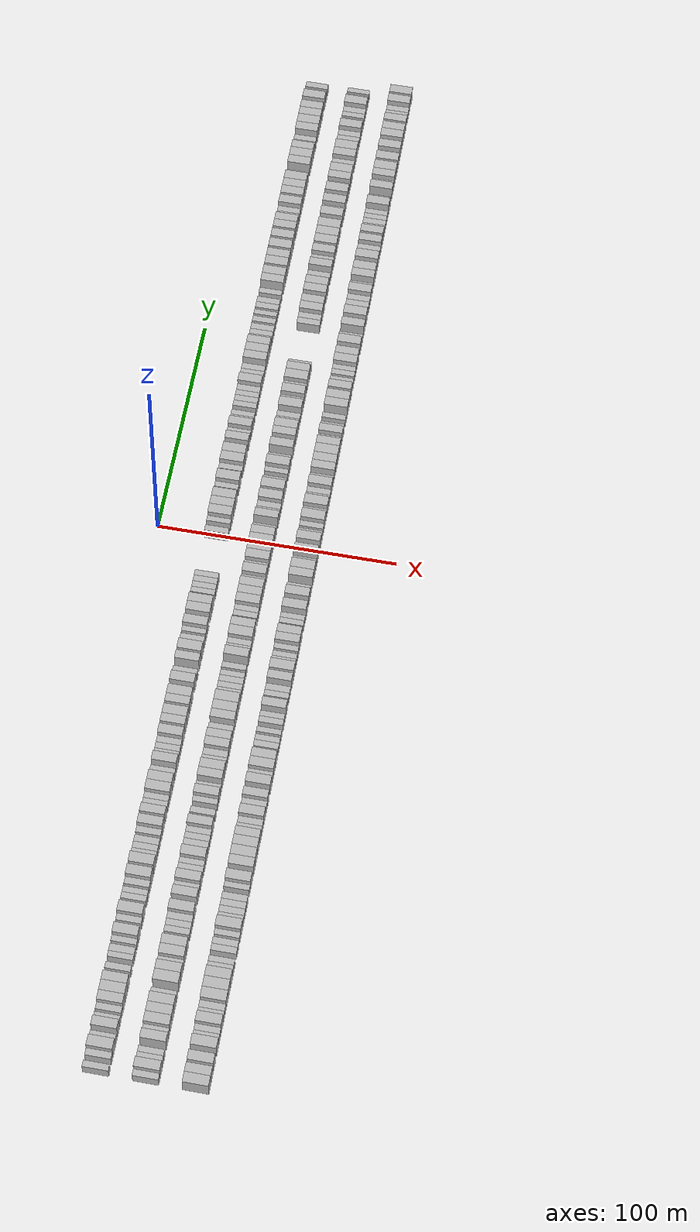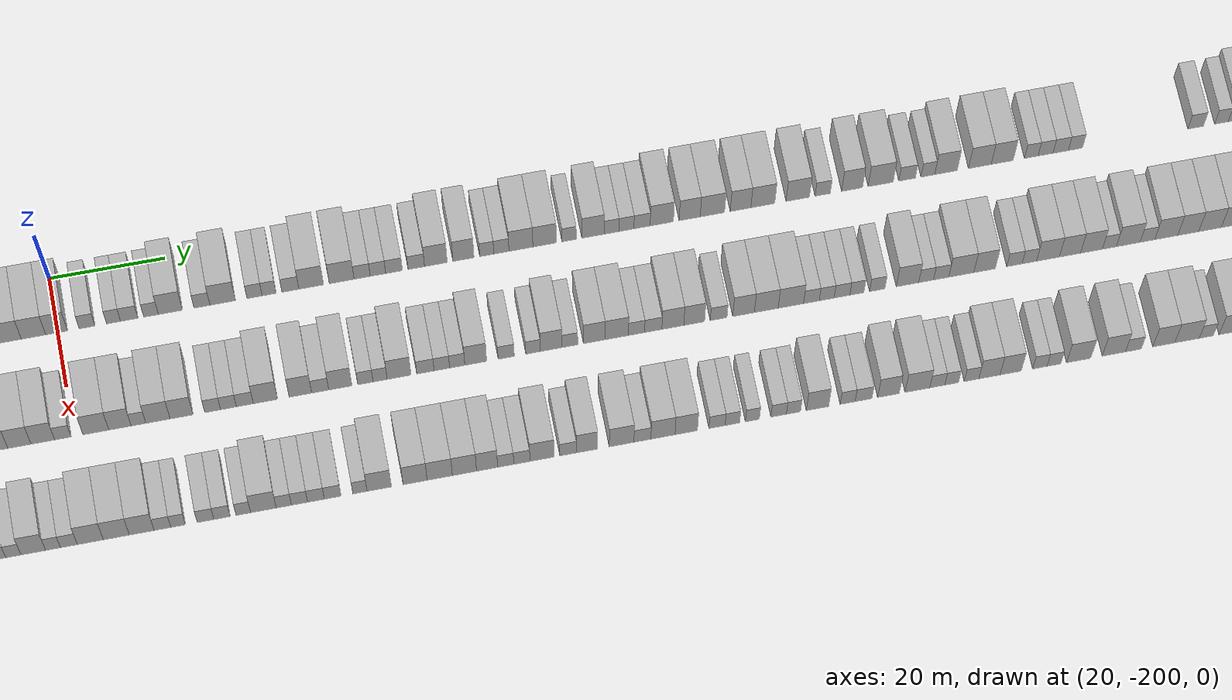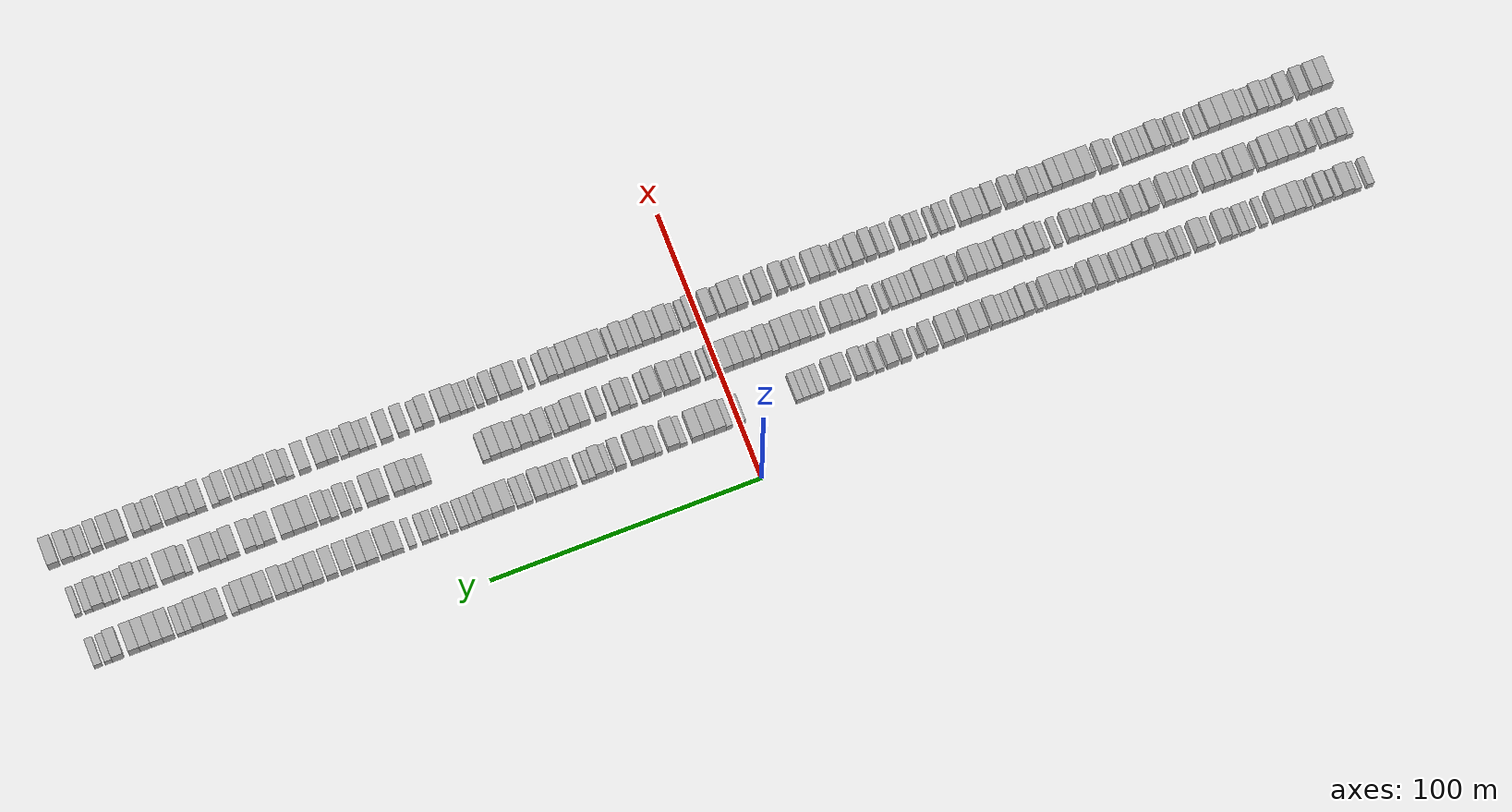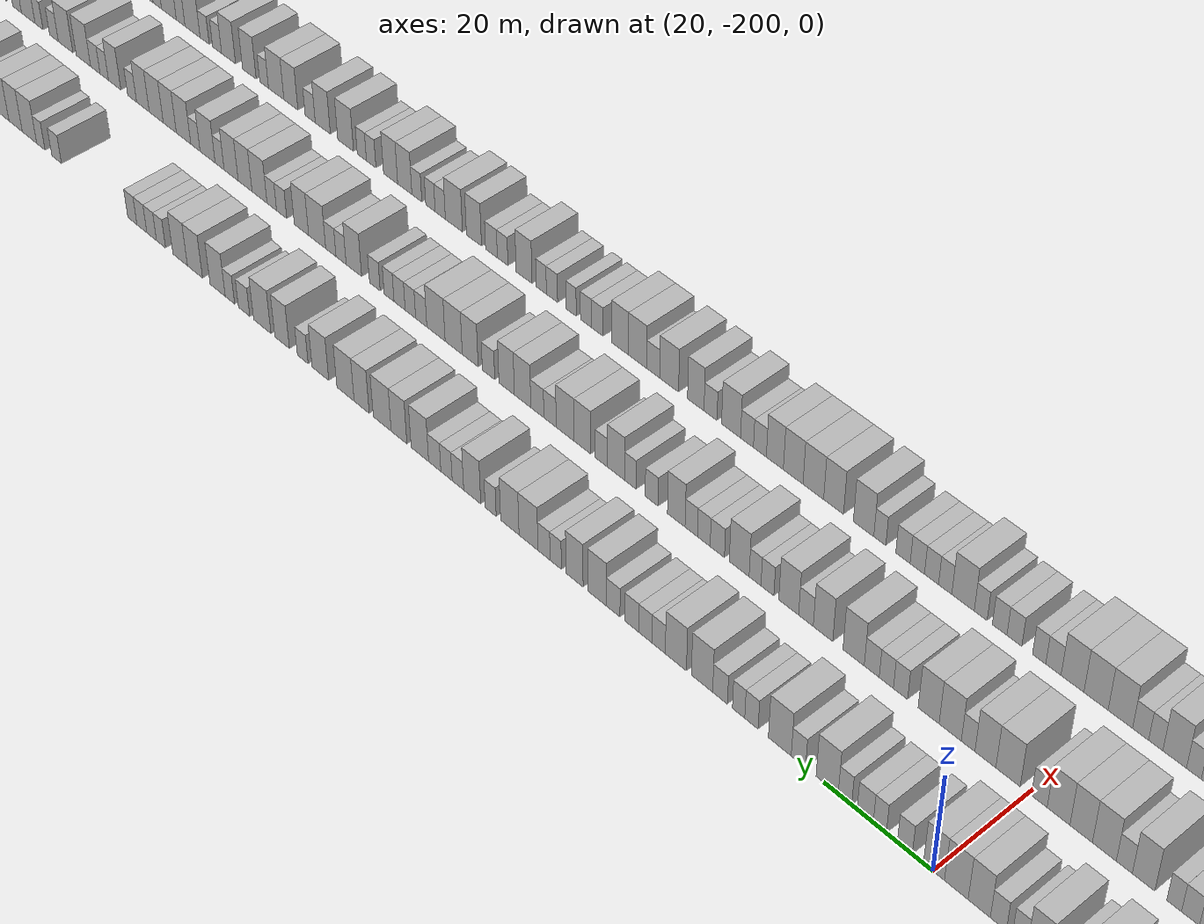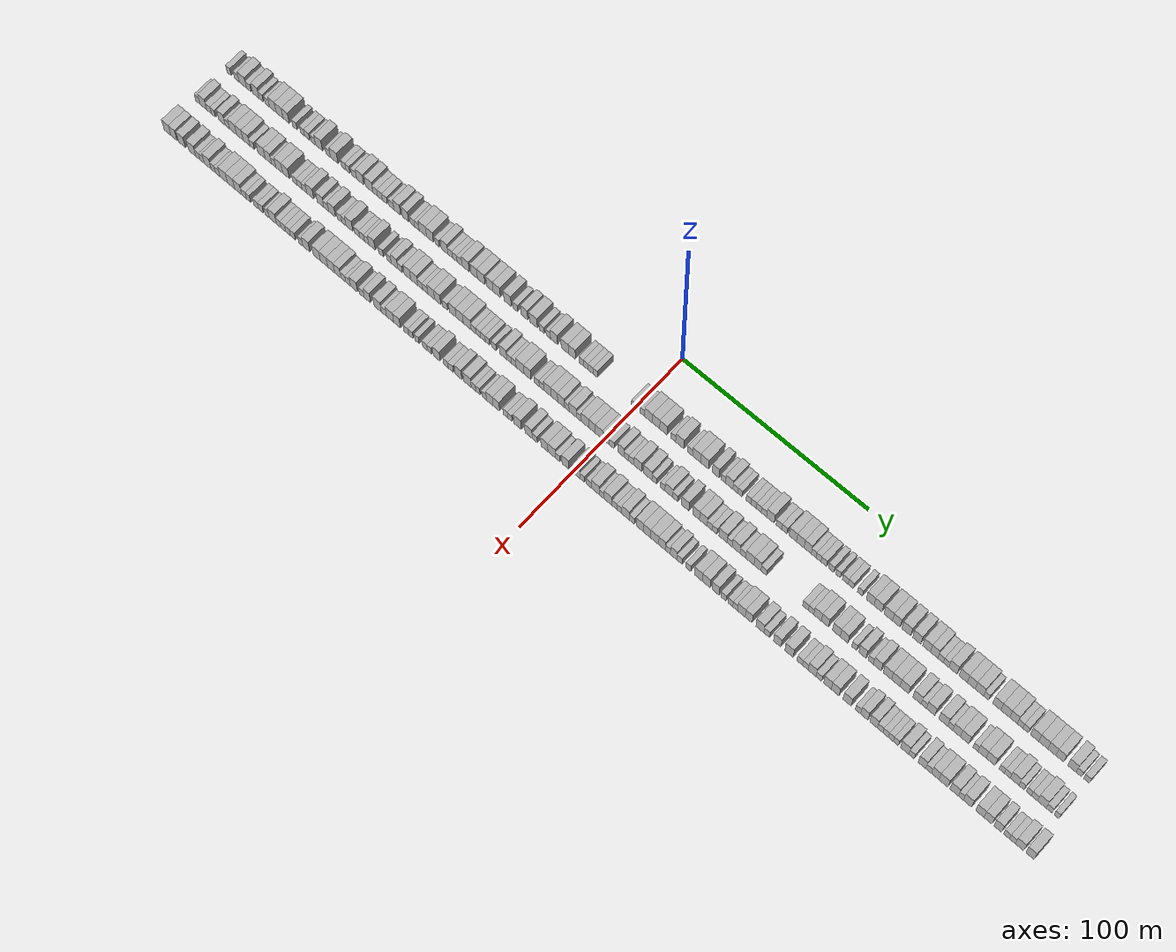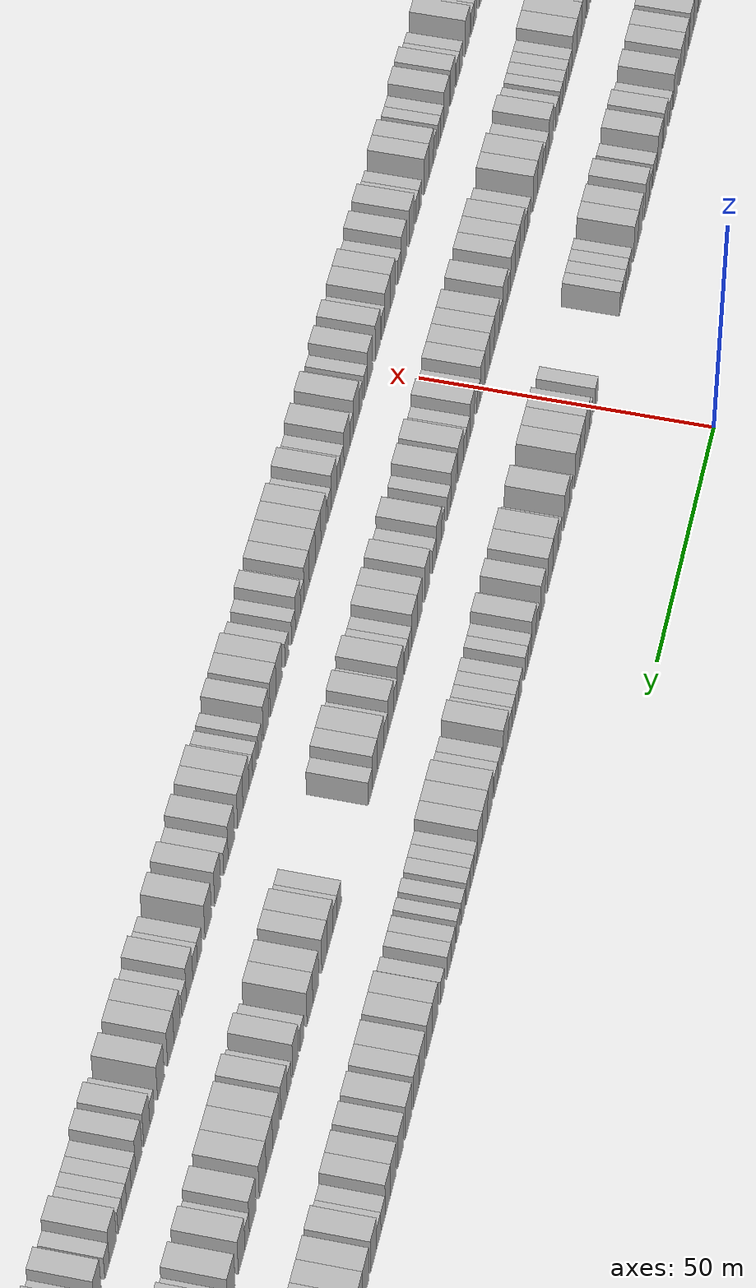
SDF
<sdf version="1.6">
 <world name="default">
  <scene>
   <sky><clouds><speed>12</speed></clouds></sky>
   <ambient>0.4 0.4 0.4 1</ambient>
   <background>0.7 0.7 0.7 1</background>
   <shadows>1</shadows>
  </scene>
  <gravity>0 0 -9.8066</gravity>
  <magnetic_field>6e-06 2.3e-05 -4.2e-05</magnetic_field>
  <physics default="0" name="default_physics" type="ode">
   <ode>
    <solver>
     <type>quick</type>
     <iters>10</iters>
     <sor>1.0</sor>
     <use_dynamic_moi_rescaling>0</use_dynamic_moi_rescaling>
    </solver>
    <constraints>
     <cfm>0</cfm>
     <erp>0.2</erp>
     <contact_max_correcting_vel>100</contact_max_correcting_vel>
     <contact_surface_layer>0.001</contact_surface_layer>
    </constraints>
   </ode>
   <max_step_size>0.004</max_step_size>
   <real_time_factor>1</real_time_factor>
   <real_time_update_rate>250</real_time_update_rate>
  </physics>
  <light name="sun" type="directional">
   <pose>0 0 10 0 0 0</pose>
   <diffuse>0.8 0.8 0.8 1</diffuse>
   <specular>0.2 0.2 0.2 1</specular>
   <attenuation>
    <range>1000</range>
    <constant>0.9</constant>
    <linear>0.01</linear>
    <quadratic>0.001</quadratic>
   </attenuation>
   <direction>-0.5 0.1 -0.9</direction>
  </light>
  <model name="building_1">
   <static>1</static>
   <pose>25.0000 -234.6783 0 0.000000 0.000000 0.000000</pose>
   <link name="link">
    <pose>0 0 3.00 0 0 0</pose>
    <collision name="collision"><geometry><box><size>10.0000 2.6435 6.0000</size></box></geometry></collision>
    <visual name="visual">
     <cast_shadows>0</cast_shadows>
     <geometry><box><size>10.0000 2.6435 6.0000</size></box></geometry>
     <material>
      <script>
       <uri>model://HANNAS_wall/materials/scripts</uri>
       <uri>model://HANNAS_wall/materials/textures</uri>
       <name>vrc/HANNAS_wall</name>
      </script>
     </material>
    </visual>
   </link>
  </model>
  <model name="building_2">
   <static>1</static>
   <pose>25.0000 -229.9542 0 0.000000 0.000000 0.000000</pose>
   <link name="link">
    <pose>0 0 3.00 0 0 0</pose>
    <collision name="collision"><geometry><box><size>10.0000 2.8046 6.0000</size></box></geometry></collision>
    <visual name="visual">
     <cast_shadows>0</cast_shadows>
     <geometry><box><size>10.0000 2.8046 6.0000</size></box></geometry>
     <material>
      <script>
       <uri>model://HANNAS_wall/materials/scripts</uri>
       <uri>model://HANNAS_wall/materials/textures</uri>
       <name>vrc/HANNAS_wall</name>
      </script>
     </material>
    </visual>
   </link>
  </model>
  <model name="building_3">
   <static>1</static>
   <pose>25.0000 -226.3536 0 0.000000 0.000000 0.000000</pose>
   <link name="link">
    <pose>0 0 4.50 0 0 0</pose>
    <collision name="collision"><geometry><box><size>10.0000 4.3965 9.0000</size></box></geometry></collision>
    <visual name="visual">
     <cast_shadows>0</cast_shadows>
     <geometry><box><size>10.0000 4.3965 9.0000</size></box></geometry>
     <material>
      <script>
       <uri>model://HANNAS_wall/materials/scripts</uri>
       <uri>model://HANNAS_wall/materials/textures</uri>
       <name>vrc/HANNAS_wall</name>
      </script>
     </material>
    </visual>
   </link>
  </model>
  <model name="building_4">
   <static>1</static>
   <pose>25.0000 -222.7586 0 0.000000 0.000000 0.000000</pose>
   <link name="link">
    <pose>0 0 3.00 0 0 0</pose>
    <collision name="collision"><geometry><box><size>10.0000 2.7936 6.0000</size></box></geometry></collision>
    <visual name="visual">
     <cast_shadows>0</cast_shadows>
     <geometry><box><size>10.0000 2.7936 6.0000</size></box></geometry>
     <material>
      <script>
       <uri>model://HANNAS_wall/materials/scripts</uri>
       <uri>model://HANNAS_wall/materials/textures</uri>
       <name>vrc/HANNAS_wall</name>
      </script>
     </material>
    </visual>
   </link>
  </model>
  <model name="building_5">
   <static>1</static>
   <pose>25.0000 -218.4428 0 0.000000 0.000000 0.000000</pose>
   <link name="link">
    <pose>0 0 4.50 0 0 0</pose>
    <collision name="collision"><geometry><box><size>10.0000 3.8380 9.0000</size></box></geometry></collision>
    <visual name="visual">
     <cast_shadows>0</cast_shadows>
     <geometry><box><size>10.0000 3.8380 9.0000</size></box></geometry>
     <material>
      <script>
       <uri>model://HANNAS_wall/materials/scripts</uri>
       <uri>model://HANNAS_wall/materials/textures</uri>
       <name>vrc/HANNAS_wall</name>
      </script>
     </material>
    </visual>
   </link>
  </model>
  <model name="building_6">
   <static>1</static>
   <pose>25.0000 -215.2362 0 0.000000 0.000000 0.000000</pose>
   <link name="link">
    <pose>0 0 3.00 0 0 0</pose>
    <collision name="collision"><geometry><box><size>10.0000 2.5753 6.0000</size></box></geometry></collision>
    <visual name="visual">
     <cast_shadows>0</cast_shadows>
     <geometry><box><size>10.0000 2.5753 6.0000</size></box></geometry>
     <material>
      <script>
       <uri>model://HANNAS_wall/materials/scripts</uri>
       <uri>model://HANNAS_wall/materials/textures</uri>
       <name>vrc/HANNAS_wall</name>
      </script>
     </material>
    </visual>
   </link>
  </model>
  <model name="building_7">
   <static>1</static>
   <pose>25.0000 -211.5604 0 0.000000 0.000000 0.000000</pose>
   <link name="link">
    <pose>0 0 3.00 0 0 0</pose>
    <collision name="collision"><geometry><box><size>10.0000 2.7763 6.0000</size></box></geometry></collision>
    <visual name="visual">
     <cast_shadows>0</cast_shadows>
     <geometry><box><size>10.0000 2.7763 6.0000</size></box></geometry>
     <material>
      <script>
       <uri>model://HANNAS_wall/materials/scripts</uri>
       <uri>model://HANNAS_wall/materials/textures</uri>
       <name>vrc/HANNAS_wall</name>
      </script>
     </material>
    </visual>
   </link>
  </model>
  <model name="building_8">
   <static>1</static>
   <pose>25.0000 -208.2255 0 0.000000 0.000000 0.000000</pose>
   <link name="link">
    <pose>0 0 4.50 0 0 0</pose>
    <collision name="collision"><geometry><box><size>10.0000 3.8936 9.0000</size></box></geometry></collision>
    <visual name="visual">
     <cast_shadows>0</cast_shadows>
     <geometry><box><size>10.0000 3.8936 9.0000</size></box></geometry>
     <material>
      <script>
       <uri>model://HANNAS_wall/materials/scripts</uri>
       <uri>model://HANNAS_wall/materials/textures</uri>
       <name>vrc/HANNAS_wall</name>
      </script>
     </material>
    </visual>
   </link>
  </model>
  <model name="building_9">
   <static>1</static>
   <pose>25.0000 -204.1825 0 0.000000 0.000000 0.000000</pose>
   <link name="link">
    <pose>0 0 4.50 0 0 0</pose>
    <collision name="collision"><geometry><box><size>10.0000 4.1924 9.0000</size></box></geometry></collision>
    <visual name="visual">
     <cast_shadows>0</cast_shadows>
     <geometry><box><size>10.0000 4.1924 9.0000</size></box></geometry>
     <material>
      <script>
       <uri>model://HANNAS_wall/materials/scripts</uri>
       <uri>model://HANNAS_wall/materials/textures</uri>
       <name>vrc/HANNAS_wall</name>
      </script>
     </material>
    </visual>
   </link>
  </model>
  <model name="building_10">
   <static>1</static>
   <pose>25.0000 -200.2013 0 0.000000 0.000000 0.000000</pose>
   <link name="link">
    <pose>0 0 4.50 0 0 0</pose>
    <collision name="collision"><geometry><box><size>10.0000 3.7700 9.0000</size></box></geometry></collision>
    <visual name="visual">
     <cast_shadows>0</cast_shadows>
     <geometry><box><size>10.0000 3.7700 9.0000</size></box></geometry>
     <material>
      <script>
       <uri>model://HANNAS_wall/materials/scripts</uri>
       <uri>model://HANNAS_wall/materials/textures</uri>
       <name>vrc/HANNAS_wall</name>
      </script>
     </material>
    </visual>
   </link>
  </model>
  <model name="building_11">
   <static>1</static>
   <pose>25.0000 -194.9556 0 0.000000 0.000000 0.000000</pose>
   <link name="link">
    <pose>0 0 3.00 0 0 0</pose>
    <collision name="collision"><geometry><box><size>10.0000 2.7212 6.0000</size></box></geometry></collision>
    <visual name="visual">
     <cast_shadows>0</cast_shadows>
     <geometry><box><size>10.0000 2.7212 6.0000</size></box></geometry>
     <material>
      <script>
       <uri>model://HANNAS_wall/materials/scripts</uri>
       <uri>model://HANNAS_wall/materials/textures</uri>
       <name>vrc/HANNAS_wall</name>
      </script>
     </material>
    </visual>
   </link>
  </model>
  <model name="building_12">
   <static>1</static>
   <pose>25.0000 -190.3929 0 0.000000 0.000000 0.000000</pose>
   <link name="link">
    <pose>0 0 3.00 0 0 0</pose>
    <collision name="collision"><geometry><box><size>10.0000 2.4041 6.0000</size></box></geometry></collision>
    <visual name="visual">
     <cast_shadows>0</cast_shadows>
     <geometry><box><size>10.0000 2.4041 6.0000</size></box></geometry>
     <material>
      <script>
       <uri>model://HANNAS_wall/materials/scripts</uri>
       <uri>model://HANNAS_wall/materials/textures</uri>
       <name>vrc/HANNAS_wall</name>
      </script>
     </material>
    </visual>
   </link>
  </model>
  <model name="building_13">
   <static>1</static>
   <pose>25.0000 -187.6924 0 0.000000 0.000000 0.000000</pose>
   <link name="link">
    <pose>0 0 3.00 0 0 0</pose>
    <collision name="collision"><geometry><box><size>10.0000 2.9969 6.0000</size></box></geometry></collision>
    <visual name="visual">
     <cast_shadows>0</cast_shadows>
     <geometry><box><size>10.0000 2.9969 6.0000</size></box></geometry>
     <material>
      <script>
       <uri>model://HANNAS_wall/materials/scripts</uri>
       <uri>model://HANNAS_wall/materials/textures</uri>
       <name>vrc/HANNAS_wall</name>
      </script>
     </material>
    </visual>
   </link>
  </model>
  <model name="building_14">
   <static>1</static>
   <pose>25.0000 -183.9322 0 0.000000 0.000000 0.000000</pose>
   <link name="link">
    <pose>0 0 3.00 0 0 0</pose>
    <collision name="collision"><geometry><box><size>10.0000 2.5236 6.0000</size></box></geometry></collision>
    <visual name="visual">
     <cast_shadows>0</cast_shadows>
     <geometry><box><size>10.0000 2.5236 6.0000</size></box></geometry>
     <material>
      <script>
       <uri>model://HANNAS_wall/materials/scripts</uri>
       <uri>model://HANNAS_wall/materials/textures</uri>
       <name>vrc/HANNAS_wall</name>
      </script>
     </material>
    </visual>
   </link>
  </model>
  <model name="building_15">
   <static>1</static>
   <pose>25.0000 -180.5875 0 0.000000 0.000000 0.000000</pose>
   <link name="link">
    <pose>0 0 4.50 0 0 0</pose>
    <collision name="collision"><geometry><box><size>10.0000 4.1658 9.0000</size></box></geometry></collision>
    <visual name="visual">
     <cast_shadows>0</cast_shadows>
     <geometry><box><size>10.0000 4.1658 9.0000</size></box></geometry>
     <material>
      <script>
       <uri>model://HANNAS_wall/materials/scripts</uri>
       <uri>model://HANNAS_wall/materials/textures</uri>
       <name>vrc/HANNAS_wall</name>
      </script>
     </material>
    </visual>
   </link>
  </model>
  <model name="building_16">
   <static>1</static>
   <pose>25.0000 -175.1283 0 0.000000 0.000000 0.000000</pose>
   <link name="link">
    <pose>0 0 3.00 0 0 0</pose>
    <collision name="collision"><geometry><box><size>10.0000 2.7526 6.0000</size></box></geometry></collision>
    <visual name="visual">
     <cast_shadows>0</cast_shadows>
     <geometry><box><size>10.0000 2.7526 6.0000</size></box></geometry>
     <material>
      <script>
       <uri>model://HANNAS_wall/materials/scripts</uri>
       <uri>model://HANNAS_wall/materials/textures</uri>
       <name>vrc/HANNAS_wall</name>
      </script>
     </material>
    </visual>
   </link>
  </model>
  <model name="building_17">
   <static>1</static>
   <pose>25.0000 -171.5461 0 0.000000 0.000000 0.000000</pose>
   <link name="link">
    <pose>0 0 4.50 0 0 0</pose>
    <collision name="collision"><geometry><box><size>10.0000 4.4117 9.0000</size></box></geometry></collision>
    <visual name="visual">
     <cast_shadows>0</cast_shadows>
     <geometry><box><size>10.0000 4.4117 9.0000</size></box></geometry>
     <material>
      <script>
       <uri>model://HANNAS_wall/materials/scripts</uri>
       <uri>model://HANNAS_wall/materials/textures</uri>
       <name>vrc/HANNAS_wall</name>
      </script>
     </material>
    </visual>
   </link>
  </model>
  <model name="building_18">
   <static>1</static>
   <pose>25.0000 -166.0316 0 0.000000 0.000000 0.000000</pose>
   <link name="link">
    <pose>0 0 3.00 0 0 0</pose>
    <collision name="collision"><geometry><box><size>10.0000 2.6173 6.0000</size></box></geometry></collision>
    <visual name="visual">
     <cast_shadows>0</cast_shadows>
     <geometry><box><size>10.0000 2.6173 6.0000</size></box></geometry>
     <material>
      <script>
       <uri>model://HANNAS_wall/materials/scripts</uri>
       <uri>model://HANNAS_wall/materials/textures</uri>
       <name>vrc/HANNAS_wall</name>
      </script>
     </material>
    </visual>
   </link>
  </model>
  <model name="building_19">
   <static>1</static>
   <pose>25.0000 -163.5074 0 0.000000 0.000000 0.000000</pose>
   <link name="link">
    <pose>0 0 3.00 0 0 0</pose>
    <collision name="collision"><geometry><box><size>10.0000 2.4312 6.0000</size></box></geometry></collision>
    <visual name="visual">
     <cast_shadows>0</cast_shadows>
     <geometry><box><size>10.0000 2.4312 6.0000</size></box></geometry>
     <material>
      <script>
       <uri>model://HANNAS_wall/materials/scripts</uri>
       <uri>model://HANNAS_wall/materials/textures</uri>
       <name>vrc/HANNAS_wall</name>
      </script>
     </material>
    </visual>
   </link>
  </model>
  <model name="building_20">
   <static>1</static>
   <pose>25.0000 -159.8269 0 0.000000 0.000000 0.000000</pose>
   <link name="link">
    <pose>0 0 3.00 0 0 0</pose>
    <collision name="collision"><geometry><box><size>10.0000 2.9297 6.0000</size></box></geometry></collision>
    <visual name="visual">
     <cast_shadows>0</cast_shadows>
     <geometry><box><size>10.0000 2.9297 6.0000</size></box></geometry>
     <material>
      <script>
       <uri>model://HANNAS_wall/materials/scripts</uri>
       <uri>model://HANNAS_wall/materials/textures</uri>
       <name>vrc/HANNAS_wall</name>
      </script>
     </material>
    </visual>
   </link>
  </model>
  <model name="building_21">
   <static>1</static>
   <pose>25.0000 -156.2195 0 0.000000 0.000000 0.000000</pose>
   <link name="link">
    <pose>0 0 4.50 0 0 0</pose>
    <collision name="collision"><geometry><box><size>10.0000 4.2850 9.0000</size></box></geometry></collision>
    <visual name="visual">
     <cast_shadows>0</cast_shadows>
     <geometry><box><size>10.0000 4.2850 9.0000</size></box></geometry>
     <material>
      <script>
       <uri>model://HANNAS_wall/materials/scripts</uri>
       <uri>model://HANNAS_wall/materials/textures</uri>
       <name>vrc/HANNAS_wall</name>
      </script>
     </material>
    </visual>
   </link>
  </model>
  <model name="building_22">
   <static>1</static>
   <pose>25.0000 -150.9233 0 0.000000 0.000000 0.000000</pose>
   <link name="link">
    <pose>0 0 4.50 0 0 0</pose>
    <collision name="collision"><geometry><box><size>10.0000 4.3073 9.0000</size></box></geometry></collision>
    <visual name="visual">
     <cast_shadows>0</cast_shadows>
     <geometry><box><size>10.0000 4.3073 9.0000</size></box></geometry>
     <material>
      <script>
       <uri>model://HANNAS_wall/materials/scripts</uri>
       <uri>model://HANNAS_wall/materials/textures</uri>
       <name>vrc/HANNAS_wall</name>
      </script>
     </material>
    </visual>
   </link>
  </model>
  <model name="building_23">
   <static>1</static>
   <pose>25.0000 -147.3701 0 0.000000 0.000000 0.000000</pose>
   <link name="link">
    <pose>0 0 3.00 0 0 0</pose>
    <collision name="collision"><geometry><box><size>10.0000 2.7992 6.0000</size></box></geometry></collision>
    <visual name="visual">
     <cast_shadows>0</cast_shadows>
     <geometry><box><size>10.0000 2.7992 6.0000</size></box></geometry>
     <material>
      <script>
       <uri>model://HANNAS_wall/materials/scripts</uri>
       <uri>model://HANNAS_wall/materials/textures</uri>
       <name>vrc/HANNAS_wall</name>
      </script>
     </material>
    </visual>
   </link>
  </model>
  <model name="building_24">
   <static>1</static>
   <pose>25.0000 -144.6269 0 0.000000 0.000000 0.000000</pose>
   <link name="link">
    <pose>0 0 3.00 0 0 0</pose>
    <collision name="collision"><geometry><box><size>10.0000 2.6872 6.0000</size></box></geometry></collision>
    <visual name="visual">
     <cast_shadows>0</cast_shadows>
     <geometry><box><size>10.0000 2.6872 6.0000</size></box></geometry>
     <material>
      <script>
       <uri>model://HANNAS_wall/materials/scripts</uri>
       <uri>model://HANNAS_wall/materials/textures</uri>
       <name>vrc/HANNAS_wall</name>
      </script>
     </material>
    </visual>
   </link>
  </model>
  <model name="building_25">
   <static>1</static>
   <pose>25.0000 -141.8265 0 0.000000 0.000000 0.000000</pose>
   <link name="link">
    <pose>0 0 3.00 0 0 0</pose>
    <collision name="collision"><geometry><box><size>10.0000 2.9137 6.0000</size></box></geometry></collision>
    <visual name="visual">
     <cast_shadows>0</cast_shadows>
     <geometry><box><size>10.0000 2.9137 6.0000</size></box></geometry>
     <material>
      <script>
       <uri>model://HANNAS_wall/materials/scripts</uri>
       <uri>model://HANNAS_wall/materials/textures</uri>
       <name>vrc/HANNAS_wall</name>
      </script>
     </material>
    </visual>
   </link>
  </model>
  <model name="building_26">
   <static>1</static>
   <pose>25.0000 -137.9409 0 0.000000 0.000000 0.000000</pose>
   <link name="link">
    <pose>0 0 3.00 0 0 0</pose>
    <collision name="collision"><geometry><box><size>10.0000 2.8574 6.0000</size></box></geometry></collision>
    <visual name="visual">
     <cast_shadows>0</cast_shadows>
     <geometry><box><size>10.0000 2.8574 6.0000</size></box></geometry>
     <material>
      <script>
       <uri>model://HANNAS_wall/materials/scripts</uri>
       <uri>model://HANNAS_wall/materials/textures</uri>
       <name>vrc/HANNAS_wall</name>
      </script>
     </material>
    </visual>
   </link>
  </model>
  <model name="building_27">
   <static>1</static>
   <pose>25.0000 -134.5359 0 0.000000 0.000000 0.000000</pose>
   <link name="link">
    <pose>0 0 4.50 0 0 0</pose>
    <collision name="collision"><geometry><box><size>10.0000 3.9525 9.0000</size></box></geometry></collision>
    <visual name="visual">
     <cast_shadows>0</cast_shadows>
     <geometry><box><size>10.0000 3.9525 9.0000</size></box></geometry>
     <material>
      <script>
       <uri>model://HANNAS_wall/materials/scripts</uri>
       <uri>model://HANNAS_wall/materials/textures</uri>
       <name>vrc/HANNAS_wall</name>
      </script>
     </material>
    </visual>
   </link>
  </model>
  <model name="building_28">
   <static>1</static>
   <pose>25.0000 -129.7239 0 0.000000 0.000000 0.000000</pose>
   <link name="link">
    <pose>0 0 4.50 0 0 0</pose>
    <collision name="collision"><geometry><box><size>10.0000 3.6714 9.0000</size></box></geometry></collision>
    <visual name="visual">
     <cast_shadows>0</cast_shadows>
     <geometry><box><size>10.0000 3.6714 9.0000</size></box></geometry>
     <material>
      <script>
       <uri>model://HANNAS_wall/materials/scripts</uri>
       <uri>model://HANNAS_wall/materials/textures</uri>
       <name>vrc/HANNAS_wall</name>
      </script>
     </material>
    </visual>
   </link>
  </model>
  <model name="building_29">
   <static>1</static>
   <pose>25.0000 -125.6593 0 0.000000 0.000000 0.000000</pose>
   <link name="link">
    <pose>0 0 3.00 0 0 0</pose>
    <collision name="collision"><geometry><box><size>10.0000 2.4579 6.0000</size></box></geometry></collision>
    <visual name="visual">
     <cast_shadows>0</cast_shadows>
     <geometry><box><size>10.0000 2.4579 6.0000</size></box></geometry>
     <material>
      <script>
       <uri>model://HANNAS_wall/materials/scripts</uri>
       <uri>model://HANNAS_wall/materials/textures</uri>
       <name>vrc/HANNAS_wall</name>
      </script>
     </material>
    </visual>
   </link>
  </model>
  <model name="building_30">
   <static>1</static>
   <pose>25.0000 -123.1066 0 0.000000 0.000000 0.000000</pose>
   <link name="link">
    <pose>0 0 3.00 0 0 0</pose>
    <collision name="collision"><geometry><box><size>10.0000 2.6475 6.0000</size></box></geometry></collision>
    <visual name="visual">
     <cast_shadows>0</cast_shadows>
     <geometry><box><size>10.0000 2.6475 6.0000</size></box></geometry>
     <material>
      <script>
       <uri>model://HANNAS_wall/materials/scripts</uri>
       <uri>model://HANNAS_wall/materials/textures</uri>
       <name>vrc/HANNAS_wall</name>
      </script>
     </material>
    </visual>
   </link>
  </model>
  <model name="building_31">
   <static>1</static>
   <pose>25.0000 -119.6929 0 0.000000 0.000000 0.000000</pose>
   <link name="link">
    <pose>0 0 4.50 0 0 0</pose>
    <collision name="collision"><geometry><box><size>10.0000 4.1798 9.0000</size></box></geometry></collision>
    <visual name="visual">
     <cast_shadows>0</cast_shadows>
     <geometry><box><size>10.0000 4.1798 9.0000</size></box></geometry>
     <material>
      <script>
       <uri>model://HANNAS_wall/materials/scripts</uri>
       <uri>model://HANNAS_wall/materials/textures</uri>
       <name>vrc/HANNAS_wall</name>
      </script>
     </material>
    </visual>
   </link>
  </model>
  <model name="building_32">
   <static>1</static>
   <pose>25.0000 -115.5559 0 0.000000 0.000000 0.000000</pose>
   <link name="link">
    <pose>0 0 4.50 0 0 0</pose>
    <collision name="collision"><geometry><box><size>10.0000 4.0942 9.0000</size></box></geometry></collision>
    <visual name="visual">
     <cast_shadows>0</cast_shadows>
     <geometry><box><size>10.0000 4.0942 9.0000</size></box></geometry>
     <material>
      <script>
       <uri>model://HANNAS_wall/materials/scripts</uri>
       <uri>model://HANNAS_wall/materials/textures</uri>
       <name>vrc/HANNAS_wall</name>
      </script>
     </material>
    </visual>
   </link>
  </model>
  <model name="building_33">
   <static>1</static>
   <pose>25.0000 -111.2703 0 0.000000 0.000000 0.000000</pose>
   <link name="link">
    <pose>0 0 3.00 0 0 0</pose>
    <collision name="collision"><geometry><box><size>10.0000 2.4771 6.0000</size></box></geometry></collision>
    <visual name="visual">
     <cast_shadows>0</cast_shadows>
     <geometry><box><size>10.0000 2.4771 6.0000</size></box></geometry>
     <material>
      <script>
       <uri>model://HANNAS_wall/materials/scripts</uri>
       <uri>model://HANNAS_wall/materials/textures</uri>
       <name>vrc/HANNAS_wall</name>
      </script>
     </material>
    </visual>
   </link>
  </model>
  <model name="building_34">
   <static>1</static>
   <pose>25.0000 -107.0902 0 0.000000 0.000000 0.000000</pose>
   <link name="link">
    <pose>0 0 4.50 0 0 0</pose>
    <collision name="collision"><geometry><box><size>10.0000 3.8831 9.0000</size></box></geometry></collision>
    <visual name="visual">
     <cast_shadows>0</cast_shadows>
     <geometry><box><size>10.0000 3.8831 9.0000</size></box></geometry>
     <material>
      <script>
       <uri>model://HANNAS_wall/materials/scripts</uri>
       <uri>model://HANNAS_wall/materials/textures</uri>
       <name>vrc/HANNAS_wall</name>
      </script>
     </material>
    </visual>
   </link>
  </model>
  <model name="building_35">
   <static>1</static>
   <pose>25.0000 -103.8325 0 0.000000 0.000000 0.000000</pose>
   <link name="link">
    <pose>0 0 3.00 0 0 0</pose>
    <collision name="collision"><geometry><box><size>10.0000 2.6325 6.0000</size></box></geometry></collision>
    <visual name="visual">
     <cast_shadows>0</cast_shadows>
     <geometry><box><size>10.0000 2.6325 6.0000</size></box></geometry>
     <material>
      <script>
       <uri>model://HANNAS_wall/materials/scripts</uri>
       <uri>model://HANNAS_wall/materials/textures</uri>
       <name>vrc/HANNAS_wall</name>
      </script>
     </material>
    </visual>
   </link>
  </model>
  <model name="building_36">
   <static>1</static>
   <pose>25.0000 -101.2096 0 0.000000 0.000000 0.000000</pose>
   <link name="link">
    <pose>0 0 3.00 0 0 0</pose>
    <collision name="collision"><geometry><box><size>10.0000 2.6132 6.0000</size></box></geometry></collision>
    <visual name="visual">
     <cast_shadows>0</cast_shadows>
     <geometry><box><size>10.0000 2.6132 6.0000</size></box></geometry>
     <material>
      <script>
       <uri>model://HANNAS_wall/materials/scripts</uri>
       <uri>model://HANNAS_wall/materials/textures</uri>
       <name>vrc/HANNAS_wall</name>
      </script>
     </material>
    </visual>
   </link>
  </model>
  <model name="building_37">
   <static>1</static>
   <pose>25.0000 -98.4836 0 0.000000 0.000000 0.000000</pose>
   <link name="link">
    <pose>0 0 3.00 0 0 0</pose>
    <collision name="collision"><geometry><box><size>10.0000 2.8388 6.0000</size></box></geometry></collision>
    <visual name="visual">
     <cast_shadows>0</cast_shadows>
     <geometry><box><size>10.0000 2.8388 6.0000</size></box></geometry>
     <material>
      <script>
       <uri>model://HANNAS_wall/materials/scripts</uri>
       <uri>model://HANNAS_wall/materials/textures</uri>
       <name>vrc/HANNAS_wall</name>
      </script>
     </material>
    </visual>
   </link>
  </model>
  <model name="building_38">
   <static>1</static>
   <pose>25.0000 -95.0189 0 0.000000 0.000000 0.000000</pose>
   <link name="link">
    <pose>0 0 4.50 0 0 0</pose>
    <collision name="collision"><geometry><box><size>10.0000 4.0907 9.0000</size></box></geometry></collision>
    <visual name="visual">
     <cast_shadows>0</cast_shadows>
     <geometry><box><size>10.0000 4.0907 9.0000</size></box></geometry>
     <material>
      <script>
       <uri>model://HANNAS_wall/materials/scripts</uri>
       <uri>model://HANNAS_wall/materials/textures</uri>
       <name>vrc/HANNAS_wall</name>
      </script>
     </material>
    </visual>
   </link>
  </model>
  <model name="building_39">
   <static>1</static>
   <pose>25.0000 -90.1166 0 0.000000 0.000000 0.000000</pose>
   <link name="link">
    <pose>0 0 4.50 0 0 0</pose>
    <collision name="collision"><geometry><box><size>10.0000 3.7139 9.0000</size></box></geometry></collision>
    <visual name="visual">
     <cast_shadows>0</cast_shadows>
     <geometry><box><size>10.0000 3.7139 9.0000</size></box></geometry>
     <material>
      <script>
       <uri>model://HANNAS_wall/materials/scripts</uri>
       <uri>model://HANNAS_wall/materials/textures</uri>
       <name>vrc/HANNAS_wall</name>
      </script>
     </material>
    </visual>
   </link>
  </model>
  <model name="building_40">
   <static>1</static>
   <pose>25.0000 -86.1214 0 0.000000 0.000000 0.000000</pose>
   <link name="link">
    <pose>0 0 4.50 0 0 0</pose>
    <collision name="collision"><geometry><box><size>10.0000 4.2764 9.0000</size></box></geometry></collision>
    <visual name="visual">
     <cast_shadows>0</cast_shadows>
     <geometry><box><size>10.0000 4.2764 9.0000</size></box></geometry>
     <material>
      <script>
       <uri>model://HANNAS_wall/materials/scripts</uri>
       <uri>model://HANNAS_wall/materials/textures</uri>
       <name>vrc/HANNAS_wall</name>
      </script>
     </material>
    </visual>
   </link>
  </model>
  <model name="building_41">
   <static>1</static>
   <pose>25.0000 -81.1622 0 0.000000 0.000000 0.000000</pose>
   <link name="link">
    <pose>0 0 4.50 0 0 0</pose>
    <collision name="collision"><geometry><box><size>10.0000 3.6420 9.0000</size></box></geometry></collision>
    <visual name="visual">
     <cast_shadows>0</cast_shadows>
     <geometry><box><size>10.0000 3.6420 9.0000</size></box></geometry>
     <material>
      <script>
       <uri>model://HANNAS_wall/materials/scripts</uri>
       <uri>model://HANNAS_wall/materials/textures</uri>
       <name>vrc/HANNAS_wall</name>
      </script>
     </material>
    </visual>
   </link>
  </model>
  <model name="building_42">
   <static>1</static>
   <pose>25.0000 -77.2369 0 0.000000 0.000000 0.000000</pose>
   <link name="link">
    <pose>0 0 4.50 0 0 0</pose>
    <collision name="collision"><geometry><box><size>10.0000 4.2085 9.0000</size></box></geometry></collision>
    <visual name="visual">
     <cast_shadows>0</cast_shadows>
     <geometry><box><size>10.0000 4.2085 9.0000</size></box></geometry>
     <material>
      <script>
       <uri>model://HANNAS_wall/materials/scripts</uri>
       <uri>model://HANNAS_wall/materials/textures</uri>
       <name>vrc/HANNAS_wall</name>
      </script>
     </material>
    </visual>
   </link>
  </model>
  <model name="building_43">
   <static>1</static>
   <pose>25.0000 -71.0786 0 0.000000 0.000000 0.000000</pose>
   <link name="link">
    <pose>0 0 4.50 0 0 0</pose>
    <collision name="collision"><geometry><box><size>10.0000 4.1080 9.0000</size></box></geometry></collision>
    <visual name="visual">
     <cast_shadows>0</cast_shadows>
     <geometry><box><size>10.0000 4.1080 9.0000</size></box></geometry>
     <material>
      <script>
       <uri>model://HANNAS_wall/materials/scripts</uri>
       <uri>model://HANNAS_wall/materials/textures</uri>
       <name>vrc/HANNAS_wall</name>
      </script>
     </material>
    </visual>
   </link>
  </model>
  <model name="building_44">
   <static>1</static>
   <pose>25.0000 -66.6794 0 0.000000 0.000000 0.000000</pose>
   <link name="link">
    <pose>0 0 3.00 0 0 0</pose>
    <collision name="collision"><geometry><box><size>10.0000 2.6904 6.0000</size></box></geometry></collision>
    <visual name="visual">
     <cast_shadows>0</cast_shadows>
     <geometry><box><size>10.0000 2.6904 6.0000</size></box></geometry>
     <material>
      <script>
       <uri>model://HANNAS_wall/materials/scripts</uri>
       <uri>model://HANNAS_wall/materials/textures</uri>
       <name>vrc/HANNAS_wall</name>
      </script>
     </material>
    </visual>
   </link>
  </model>
  <model name="building_45">
   <static>1</static>
   <pose>25.0000 -61.4915 0 0.000000 0.000000 0.000000</pose>
   <link name="link">
    <pose>0 0 4.50 0 0 0</pose>
    <collision name="collision"><geometry><box><size>10.0000 3.6855 9.0000</size></box></geometry></collision>
    <visual name="visual">
     <cast_shadows>0</cast_shadows>
     <geometry><box><size>10.0000 3.6855 9.0000</size></box></geometry>
     <material>
      <script>
       <uri>model://HANNAS_wall/materials/scripts</uri>
       <uri>model://HANNAS_wall/materials/textures</uri>
       <name>vrc/HANNAS_wall</name>
      </script>
     </material>
    </visual>
   </link>
  </model>
  <model name="building_46">
   <static>1</static>
   <pose>25.0000 -56.4312 0 0.000000 0.000000 0.000000</pose>
   <link name="link">
    <pose>0 0 4.50 0 0 0</pose>
    <collision name="collision"><geometry><box><size>10.0000 4.4351 9.0000</size></box></geometry></collision>
    <visual name="visual">
     <cast_shadows>0</cast_shadows>
     <geometry><box><size>10.0000 4.4351 9.0000</size></box></geometry>
     <material>
      <script>
       <uri>model://HANNAS_wall/materials/scripts</uri>
       <uri>model://HANNAS_wall/materials/textures</uri>
       <name>vrc/HANNAS_wall</name>
      </script>
     </material>
    </visual>
   </link>
  </model>
  <model name="building_47">
   <static>1</static>
   <pose>25.0000 -51.7509 0 0.000000 0.000000 0.000000</pose>
   <link name="link">
    <pose>0 0 3.00 0 0 0</pose>
    <collision name="collision"><geometry><box><size>10.0000 2.9255 6.0000</size></box></geometry></collision>
    <visual name="visual">
     <cast_shadows>0</cast_shadows>
     <geometry><box><size>10.0000 2.9255 6.0000</size></box></geometry>
     <material>
      <script>
       <uri>model://HANNAS_wall/materials/scripts</uri>
       <uri>model://HANNAS_wall/materials/textures</uri>
       <name>vrc/HANNAS_wall</name>
      </script>
     </material>
    </visual>
   </link>
  </model>
  <model name="building_48">
   <static>1</static>
   <pose>25.0000 -48.0663 0 0.000000 0.000000 0.000000</pose>
   <link name="link">
    <pose>0 0 3.00 0 0 0</pose>
    <collision name="collision"><geometry><box><size>10.0000 2.4438 6.0000</size></box></geometry></collision>
    <visual name="visual">
     <cast_shadows>0</cast_shadows>
     <geometry><box><size>10.0000 2.4438 6.0000</size></box></geometry>
     <material>
      <script>
       <uri>model://HANNAS_wall/materials/scripts</uri>
       <uri>model://HANNAS_wall/materials/textures</uri>
       <name>vrc/HANNAS_wall</name>
      </script>
     </material>
    </visual>
   </link>
  </model>
  <model name="building_49">
   <static>1</static>
   <pose>25.0000 -44.8534 0 0.000000 0.000000 0.000000</pose>
   <link name="link">
    <pose>0 0 4.50 0 0 0</pose>
    <collision name="collision"><geometry><box><size>10.0000 3.9821 9.0000</size></box></geometry></collision>
    <visual name="visual">
     <cast_shadows>0</cast_shadows>
     <geometry><box><size>10.0000 3.9821 9.0000</size></box></geometry>
     <material>
      <script>
       <uri>model://HANNAS_wall/materials/scripts</uri>
       <uri>model://HANNAS_wall/materials/textures</uri>
       <name>vrc/HANNAS_wall</name>
      </script>
     </material>
    </visual>
   </link>
  </model>
  <model name="building_50">
   <static>1</static>
   <pose>25.0000 -38.8466 0 0.000000 0.000000 0.000000</pose>
   <link name="link">
    <pose>0 0 4.50 0 0 0</pose>
    <collision name="collision"><geometry><box><size>10.0000 4.0314 9.0000</size></box></geometry></collision>
    <visual name="visual">
     <cast_shadows>0</cast_shadows>
     <geometry><box><size>10.0000 4.0314 9.0000</size></box></geometry>
     <material>
      <script>
       <uri>model://HANNAS_wall/materials/scripts</uri>
       <uri>model://HANNAS_wall/materials/textures</uri>
       <name>vrc/HANNAS_wall</name>
      </script>
     </material>
    </visual>
   </link>
  </model>
  <model name="building_51">
   <static>1</static>
   <pose>25.0000 -34.8790 0 0.000000 0.000000 0.000000</pose>
   <link name="link">
    <pose>0 0 4.50 0 0 0</pose>
    <collision name="collision"><geometry><box><size>10.0000 3.9037 9.0000</size></box></geometry></collision>
    <visual name="visual">
     <cast_shadows>0</cast_shadows>
     <geometry><box><size>10.0000 3.9037 9.0000</size></box></geometry>
     <material>
      <script>
       <uri>model://HANNAS_wall/materials/scripts</uri>
       <uri>model://HANNAS_wall/materials/textures</uri>
       <name>vrc/HANNAS_wall</name>
      </script>
     </material>
    </visual>
   </link>
  </model>
  <model name="building_52">
   <static>1</static>
   <pose>25.0000 -29.7062 0 0.000000 0.000000 0.000000</pose>
   <link name="link">
    <pose>0 0 3.00 0 0 0</pose>
    <collision name="collision"><geometry><box><size>10.0000 2.4420 6.0000</size></box></geometry></collision>
    <visual name="visual">
     <cast_shadows>0</cast_shadows>
     <geometry><box><size>10.0000 2.4420 6.0000</size></box></geometry>
     <material>
      <script>
       <uri>model://HANNAS_wall/materials/scripts</uri>
       <uri>model://HANNAS_wall/materials/textures</uri>
       <name>vrc/HANNAS_wall</name>
      </script>
     </material>
    </visual>
   </link>
  </model>
  <model name="building_53">
   <static>1</static>
   <pose>25.0000 -27.1594 0 0.000000 0.000000 0.000000</pose>
   <link name="link">
    <pose>0 0 3.00 0 0 0</pose>
    <collision name="collision"><geometry><box><size>10.0000 2.6516 6.0000</size></box></geometry></collision>
    <visual name="visual">
     <cast_shadows>0</cast_shadows>
     <geometry><box><size>10.0000 2.6516 6.0000</size></box></geometry>
     <material>
      <script>
       <uri>model://HANNAS_wall/materials/scripts</uri>
       <uri>model://HANNAS_wall/materials/textures</uri>
       <name>vrc/HANNAS_wall</name>
      </script>
     </material>
    </visual>
   </link>
  </model>
  <model name="building_54">
   <static>1</static>
   <pose>25.0000 -24.4721 0 0.000000 0.000000 0.000000</pose>
   <link name="link">
    <pose>0 0 3.00 0 0 0</pose>
    <collision name="collision"><geometry><box><size>10.0000 2.7231 6.0000</size></box></geometry></collision>
    <visual name="visual">
     <cast_shadows>0</cast_shadows>
     <geometry><box><size>10.0000 2.7231 6.0000</size></box></geometry>
     <material>
      <script>
       <uri>model://HANNAS_wall/materials/scripts</uri>
       <uri>model://HANNAS_wall/materials/textures</uri>
       <name>vrc/HANNAS_wall</name>
      </script>
     </material>
    </visual>
   </link>
  </model>
  <model name="building_55">
   <static>1</static>
   <pose>25.0000 -21.8469 0 0.000000 0.000000 0.000000</pose>
   <link name="link">
    <pose>0 0 3.00 0 0 0</pose>
    <collision name="collision"><geometry><box><size>10.0000 2.5272 6.0000</size></box></geometry></collision>
    <visual name="visual">
     <cast_shadows>0</cast_shadows>
     <geometry><box><size>10.0000 2.5272 6.0000</size></box></geometry>
     <material>
      <script>
       <uri>model://HANNAS_wall/materials/scripts</uri>
       <uri>model://HANNAS_wall/materials/textures</uri>
       <name>vrc/HANNAS_wall</name>
      </script>
     </material>
    </visual>
   </link>
  </model>
  <model name="building_56">
   <static>1</static>
   <pose>25.0000 -0.3898 0 0.000000 0.000000 0.000000</pose>
   <link name="link">
    <pose>0 0 3.00 0 0 0</pose>
    <collision name="collision"><geometry><box><size>10.0000 2.7957 6.0000</size></box></geometry></collision>
    <visual name="visual">
     <cast_shadows>0</cast_shadows>
     <geometry><box><size>10.0000 2.7957 6.0000</size></box></geometry>
     <material>
      <script>
       <uri>model://HANNAS_wall/materials/scripts</uri>
       <uri>model://HANNAS_wall/materials/textures</uri>
       <name>vrc/HANNAS_wall</name>
      </script>
     </material>
    </visual>
   </link>
  </model>
  <model name="building_57">
   <static>1</static>
   <pose>25.0000 4.2181 0 0.000000 0.000000 0.000000</pose>
   <link name="link">
    <pose>0 0 3.00 0 0 0</pose>
    <collision name="collision"><geometry><box><size>10.0000 2.4200 6.0000</size></box></geometry></collision>
    <visual name="visual">
     <cast_shadows>0</cast_shadows>
     <geometry><box><size>10.0000 2.4200 6.0000</size></box></geometry>
     <material>
      <script>
       <uri>model://HANNAS_wall/materials/scripts</uri>
       <uri>model://HANNAS_wall/materials/textures</uri>
       <name>vrc/HANNAS_wall</name>
      </script>
     </material>
    </visual>
   </link>
  </model>
  <model name="building_58">
   <static>1</static>
   <pose>25.0000 7.5503 0 0.000000 0.000000 0.000000</pose>
   <link name="link">
    <pose>0 0 4.50 0 0 0</pose>
    <collision name="collision"><geometry><box><size>10.0000 4.2445 9.0000</size></box></geometry></collision>
    <visual name="visual">
     <cast_shadows>0</cast_shadows>
     <geometry><box><size>10.0000 4.2445 9.0000</size></box></geometry>
     <material>
      <script>
       <uri>model://HANNAS_wall/materials/scripts</uri>
       <uri>model://HANNAS_wall/materials/textures</uri>
       <name>vrc/HANNAS_wall</name>
      </script>
     </material>
    </visual>
   </link>
  </model>
  <model name="building_59">
   <static>1</static>
   <pose>25.0000 11.6644 0 0.000000 0.000000 0.000000</pose>
   <link name="link">
    <pose>0 0 4.50 0 0 0</pose>
    <collision name="collision"><geometry><box><size>10.0000 3.9837 9.0000</size></box></geometry></collision>
    <visual name="visual">
     <cast_shadows>0</cast_shadows>
     <geometry><box><size>10.0000 3.9837 9.0000</size></box></geometry>
     <material>
      <script>
       <uri>model://HANNAS_wall/materials/scripts</uri>
       <uri>model://HANNAS_wall/materials/textures</uri>
       <name>vrc/HANNAS_wall</name>
      </script>
     </material>
    </visual>
   </link>
  </model>
  <model name="building_60">
   <static>1</static>
   <pose>25.0000 15.7348 0 0.000000 0.000000 0.000000</pose>
   <link name="link">
    <pose>0 0 4.50 0 0 0</pose>
    <collision name="collision"><geometry><box><size>10.0000 4.1571 9.0000</size></box></geometry></collision>
    <visual name="visual">
     <cast_shadows>0</cast_shadows>
     <geometry><box><size>10.0000 4.1571 9.0000</size></box></geometry>
     <material>
      <script>
       <uri>model://HANNAS_wall/materials/scripts</uri>
       <uri>model://HANNAS_wall/materials/textures</uri>
       <name>vrc/HANNAS_wall</name>
      </script>
     </material>
    </visual>
   </link>
  </model>
  <model name="building_61">
   <static>1</static>
   <pose>25.0000 21.0873 0 0.000000 0.000000 0.000000</pose>
   <link name="link">
    <pose>0 0 3.00 0 0 0</pose>
    <collision name="collision"><geometry><box><size>10.0000 2.5480 6.0000</size></box></geometry></collision>
    <visual name="visual">
     <cast_shadows>0</cast_shadows>
     <geometry><box><size>10.0000 2.5480 6.0000</size></box></geometry>
     <material>
      <script>
       <uri>model://HANNAS_wall/materials/scripts</uri>
       <uri>model://HANNAS_wall/materials/textures</uri>
       <name>vrc/HANNAS_wall</name>
      </script>
     </material>
    </visual>
   </link>
  </model>
  <model name="building_62">
   <static>1</static>
   <pose>25.0000 24.6056 0 0.000000 0.000000 0.000000</pose>
   <link name="link">
    <pose>0 0 4.50 0 0 0</pose>
    <collision name="collision"><geometry><box><size>10.0000 4.4885 9.0000</size></box></geometry></collision>
    <visual name="visual">
     <cast_shadows>0</cast_shadows>
     <geometry><box><size>10.0000 4.4885 9.0000</size></box></geometry>
     <material>
      <script>
       <uri>model://HANNAS_wall/materials/scripts</uri>
       <uri>model://HANNAS_wall/materials/textures</uri>
       <name>vrc/HANNAS_wall</name>
      </script>
     </material>
    </visual>
   </link>
  </model>
  <model name="building_63">
   <static>1</static>
   <pose>25.0000 30.2030 0 0.000000 0.000000 0.000000</pose>
   <link name="link">
    <pose>0 0 3.00 0 0 0</pose>
    <collision name="collision"><geometry><box><size>10.0000 2.7063 6.0000</size></box></geometry></collision>
    <visual name="visual">
     <cast_shadows>0</cast_shadows>
     <geometry><box><size>10.0000 2.7063 6.0000</size></box></geometry>
     <material>
      <script>
       <uri>model://HANNAS_wall/materials/scripts</uri>
       <uri>model://HANNAS_wall/materials/textures</uri>
       <name>vrc/HANNAS_wall</name>
      </script>
     </material>
    </visual>
   </link>
  </model>
  <model name="building_64">
   <static>1</static>
   <pose>25.0000 33.7326 0 0.000000 0.000000 0.000000</pose>
   <link name="link">
    <pose>0 0 4.50 0 0 0</pose>
    <collision name="collision"><geometry><box><size>10.0000 4.3529 9.0000</size></box></geometry></collision>
    <visual name="visual">
     <cast_shadows>0</cast_shadows>
     <geometry><box><size>10.0000 4.3529 9.0000</size></box></geometry>
     <material>
      <script>
       <uri>model://HANNAS_wall/materials/scripts</uri>
       <uri>model://HANNAS_wall/materials/textures</uri>
       <name>vrc/HANNAS_wall</name>
      </script>
     </material>
    </visual>
   </link>
  </model>
  <model name="building_65">
   <static>1</static>
   <pose>25.0000 38.0556 0 0.000000 0.000000 0.000000</pose>
   <link name="link">
    <pose>0 0 4.50 0 0 0</pose>
    <collision name="collision"><geometry><box><size>10.0000 4.2929 9.0000</size></box></geometry></collision>
    <visual name="visual">
     <cast_shadows>0</cast_shadows>
     <geometry><box><size>10.0000 4.2929 9.0000</size></box></geometry>
     <material>
      <script>
       <uri>model://HANNAS_wall/materials/scripts</uri>
       <uri>model://HANNAS_wall/materials/textures</uri>
       <name>vrc/HANNAS_wall</name>
      </script>
     </material>
    </visual>
   </link>
  </model>
  <model name="building_66">
   <static>1</static>
   <pose>25.0000 44.0719 0 0.000000 0.000000 0.000000</pose>
   <link name="link">
    <pose>0 0 4.50 0 0 0</pose>
    <collision name="collision"><geometry><box><size>10.0000 3.7396 9.0000</size></box></geometry></collision>
    <visual name="visual">
     <cast_shadows>0</cast_shadows>
     <geometry><box><size>10.0000 3.7396 9.0000</size></box></geometry>
     <material>
      <script>
       <uri>model://HANNAS_wall/materials/scripts</uri>
       <uri>model://HANNAS_wall/materials/textures</uri>
       <name>vrc/HANNAS_wall</name>
      </script>
     </material>
    </visual>
   </link>
  </model>
  <model name="building_67">
   <static>1</static>
   <pose>25.0000 48.1564 0 0.000000 0.000000 0.000000</pose>
   <link name="link">
    <pose>0 0 3.00 0 0 0</pose>
    <collision name="collision"><geometry><box><size>10.0000 2.4293 6.0000</size></box></geometry></collision>
    <visual name="visual">
     <cast_shadows>0</cast_shadows>
     <geometry><box><size>10.0000 2.4293 6.0000</size></box></geometry>
     <material>
      <script>
       <uri>model://HANNAS_wall/materials/scripts</uri>
       <uri>model://HANNAS_wall/materials/textures</uri>
       <name>vrc/HANNAS_wall</name>
      </script>
     </material>
    </visual>
   </link>
  </model>
  <model name="building_68">
   <static>1</static>
   <pose>25.0000 51.3450 0 0.000000 0.000000 0.000000</pose>
   <link name="link">
    <pose>0 0 4.50 0 0 0</pose>
    <collision name="collision"><geometry><box><size>10.0000 3.9480 9.0000</size></box></geometry></collision>
    <visual name="visual">
     <cast_shadows>0</cast_shadows>
     <geometry><box><size>10.0000 3.9480 9.0000</size></box></geometry>
     <material>
      <script>
       <uri>model://HANNAS_wall/materials/scripts</uri>
       <uri>model://HANNAS_wall/materials/textures</uri>
       <name>vrc/HANNAS_wall</name>
      </script>
     </material>
    </visual>
   </link>
  </model>
  <model name="building_69">
   <static>1</static>
   <pose>25.0000 54.5966 0 0.000000 0.000000 0.000000</pose>
   <link name="link">
    <pose>0 0 3.00 0 0 0</pose>
    <collision name="collision"><geometry><box><size>10.0000 2.5550 6.0000</size></box></geometry></collision>
    <visual name="visual">
     <cast_shadows>0</cast_shadows>
     <geometry><box><size>10.0000 2.5550 6.0000</size></box></geometry>
     <material>
      <script>
       <uri>model://HANNAS_wall/materials/scripts</uri>
       <uri>model://HANNAS_wall/materials/textures</uri>
       <name>vrc/HANNAS_wall</name>
      </script>
     </material>
    </visual>
   </link>
  </model>
  <model name="building_70">
   <static>1</static>
   <pose>25.0000 57.1111 0 0.000000 0.000000 0.000000</pose>
   <link name="link">
    <pose>0 0 3.00 0 0 0</pose>
    <collision name="collision"><geometry><box><size>10.0000 2.4741 6.0000</size></box></geometry></collision>
    <visual name="visual">
     <cast_shadows>0</cast_shadows>
     <geometry><box><size>10.0000 2.4741 6.0000</size></box></geometry>
     <material>
      <script>
       <uri>model://HANNAS_wall/materials/scripts</uri>
       <uri>model://HANNAS_wall/materials/textures</uri>
       <name>vrc/HANNAS_wall</name>
      </script>
     </material>
    </visual>
   </link>
  </model>
  <model name="building_71">
   <static>1</static>
   <pose>25.0000 61.6997 0 0.000000 0.000000 0.000000</pose>
   <link name="link">
    <pose>0 0 3.00 0 0 0</pose>
    <collision name="collision"><geometry><box><size>10.0000 2.7030 6.0000</size></box></geometry></collision>
    <visual name="visual">
     <cast_shadows>0</cast_shadows>
     <geometry><box><size>10.0000 2.7030 6.0000</size></box></geometry>
     <material>
      <script>
       <uri>model://HANNAS_wall/materials/scripts</uri>
       <uri>model://HANNAS_wall/materials/textures</uri>
       <name>vrc/HANNAS_wall</name>
      </script>
     </material>
    </visual>
   </link>
  </model>
  <model name="building_72">
   <static>1</static>
   <pose>25.0000 64.4498 0 0.000000 0.000000 0.000000</pose>
   <link name="link">
    <pose>0 0 3.00 0 0 0</pose>
    <collision name="collision"><geometry><box><size>10.0000 2.7973 6.0000</size></box></geometry></collision>
    <visual name="visual">
     <cast_shadows>0</cast_shadows>
     <geometry><box><size>10.0000 2.7973 6.0000</size></box></geometry>
     <material>
      <script>
       <uri>model://HANNAS_wall/materials/scripts</uri>
       <uri>model://HANNAS_wall/materials/textures</uri>
       <name>vrc/HANNAS_wall</name>
      </script>
     </material>
    </visual>
   </link>
  </model>
  <model name="building_73">
   <static>1</static>
   <pose>25.0000 67.1315 0 0.000000 0.000000 0.000000</pose>
   <link name="link">
    <pose>0 0 3.00 0 0 0</pose>
    <collision name="collision"><geometry><box><size>10.0000 2.5660 6.0000</size></box></geometry></collision>
    <visual name="visual">
     <cast_shadows>0</cast_shadows>
     <geometry><box><size>10.0000 2.5660 6.0000</size></box></geometry>
     <material>
      <script>
       <uri>model://HANNAS_wall/materials/scripts</uri>
       <uri>model://HANNAS_wall/materials/textures</uri>
       <name>vrc/HANNAS_wall</name>
      </script>
     </material>
    </visual>
   </link>
  </model>
  <model name="building_74">
   <static>1</static>
   <pose>25.0000 69.8629 0 0.000000 0.000000 0.000000</pose>
   <link name="link">
    <pose>0 0 3.00 0 0 0</pose>
    <collision name="collision"><geometry><box><size>10.0000 2.8969 6.0000</size></box></geometry></collision>
    <visual name="visual">
     <cast_shadows>0</cast_shadows>
     <geometry><box><size>10.0000 2.8969 6.0000</size></box></geometry>
     <material>
      <script>
       <uri>model://HANNAS_wall/materials/scripts</uri>
       <uri>model://HANNAS_wall/materials/textures</uri>
       <name>vrc/HANNAS_wall</name>
      </script>
     </material>
    </visual>
   </link>
  </model>
  <model name="building_75">
   <static>1</static>
   <pose>25.0000 73.3644 0 0.000000 0.000000 0.000000</pose>
   <link name="link">
    <pose>0 0 4.50 0 0 0</pose>
    <collision name="collision"><geometry><box><size>10.0000 4.1061 9.0000</size></box></geometry></collision>
    <visual name="visual">
     <cast_shadows>0</cast_shadows>
     <geometry><box><size>10.0000 4.1061 9.0000</size></box></geometry>
     <material>
      <script>
       <uri>model://HANNAS_wall/materials/scripts</uri>
       <uri>model://HANNAS_wall/materials/textures</uri>
       <name>vrc/HANNAS_wall</name>
      </script>
     </material>
    </visual>
   </link>
  </model>
  <model name="building_76">
   <static>1</static>
   <pose>25.0000 77.9017 0 0.000000 0.000000 0.000000</pose>
   <link name="link">
    <pose>0 0 3.00 0 0 0</pose>
    <collision name="collision"><geometry><box><size>10.0000 2.9686 6.0000</size></box></geometry></collision>
    <visual name="visual">
     <cast_shadows>0</cast_shadows>
     <geometry><box><size>10.0000 2.9686 6.0000</size></box></geometry>
     <material>
      <script>
       <uri>model://HANNAS_wall/materials/scripts</uri>
       <uri>model://HANNAS_wall/materials/textures</uri>
       <name>vrc/HANNAS_wall</name>
      </script>
     </material>
    </visual>
   </link>
  </model>
  <model name="building_77">
   <static>1</static>
   <pose>25.0000 80.8199 0 0.000000 0.000000 0.000000</pose>
   <link name="link">
    <pose>0 0 3.00 0 0 0</pose>
    <collision name="collision"><geometry><box><size>10.0000 2.8679 6.0000</size></box></geometry></collision>
    <visual name="visual">
     <cast_shadows>0</cast_shadows>
     <geometry><box><size>10.0000 2.8679 6.0000</size></box></geometry>
     <material>
      <script>
       <uri>model://HANNAS_wall/materials/scripts</uri>
       <uri>model://HANNAS_wall/materials/textures</uri>
       <name>vrc/HANNAS_wall</name>
      </script>
     </material>
    </visual>
   </link>
  </model>
  <model name="building_78">
   <static>1</static>
   <pose>25.0000 85.2276 0 0.000000 0.000000 0.000000</pose>
   <link name="link">
    <pose>0 0 4.50 0 0 0</pose>
    <collision name="collision"><geometry><box><size>10.0000 3.9474 9.0000</size></box></geometry></collision>
    <visual name="visual">
     <cast_shadows>0</cast_shadows>
     <geometry><box><size>10.0000 3.9474 9.0000</size></box></geometry>
     <material>
      <script>
       <uri>model://HANNAS_wall/materials/scripts</uri>
       <uri>model://HANNAS_wall/materials/textures</uri>
       <name>vrc/HANNAS_wall</name>
      </script>
     </material>
    </visual>
   </link>
  </model>
  <model name="building_79">
   <static>1</static>
   <pose>25.0000 89.2398 0 0.000000 0.000000 0.000000</pose>
   <link name="link">
    <pose>0 0 4.50 0 0 0</pose>
    <collision name="collision"><geometry><box><size>10.0000 4.0771 9.0000</size></box></geometry></collision>
    <visual name="visual">
     <cast_shadows>0</cast_shadows>
     <geometry><box><size>10.0000 4.0771 9.0000</size></box></geometry>
     <material>
      <script>
       <uri>model://HANNAS_wall/materials/scripts</uri>
       <uri>model://HANNAS_wall/materials/textures</uri>
       <name>vrc/HANNAS_wall</name>
      </script>
     </material>
    </visual>
   </link>
  </model>
  <model name="building_80">
   <static>1</static>
   <pose>25.0000 93.1396 0 0.000000 0.000000 0.000000</pose>
   <link name="link">
    <pose>0 0 4.50 0 0 0</pose>
    <collision name="collision"><geometry><box><size>10.0000 3.7225 9.0000</size></box></geometry></collision>
    <visual name="visual">
     <cast_shadows>0</cast_shadows>
     <geometry><box><size>10.0000 3.7225 9.0000</size></box></geometry>
     <material>
      <script>
       <uri>model://HANNAS_wall/materials/scripts</uri>
       <uri>model://HANNAS_wall/materials/textures</uri>
       <name>vrc/HANNAS_wall</name>
      </script>
     </material>
    </visual>
   </link>
  </model>
  <model name="building_81">
   <static>1</static>
   <pose>25.0000 96.2928 0 0.000000 0.000000 0.000000</pose>
   <link name="link">
    <pose>0 0 3.00 0 0 0</pose>
    <collision name="collision"><geometry><box><size>10.0000 2.5839 6.0000</size></box></geometry></collision>
    <visual name="visual">
     <cast_shadows>0</cast_shadows>
     <geometry><box><size>10.0000 2.5839 6.0000</size></box></geometry>
     <material>
      <script>
       <uri>model://HANNAS_wall/materials/scripts</uri>
       <uri>model://HANNAS_wall/materials/textures</uri>
       <name>vrc/HANNAS_wall</name>
      </script>
     </material>
    </visual>
   </link>
  </model>
  <model name="building_82">
   <static>1</static>
   <pose>25.0000 98.8640 0 0.000000 0.000000 0.000000</pose>
   <link name="link">
    <pose>0 0 3.00 0 0 0</pose>
    <collision name="collision"><geometry><box><size>10.0000 2.5585 6.0000</size></box></geometry></collision>
    <visual name="visual">
     <cast_shadows>0</cast_shadows>
     <geometry><box><size>10.0000 2.5585 6.0000</size></box></geometry>
     <material>
      <script>
       <uri>model://HANNAS_wall/materials/scripts</uri>
       <uri>model://HANNAS_wall/materials/textures</uri>
       <name>vrc/HANNAS_wall</name>
      </script>
     </material>
    </visual>
   </link>
  </model>
  <model name="building_83">
   <static>1</static>
   <pose>25.0000 101.6313 0 0.000000 0.000000 0.000000</pose>
   <link name="link">
    <pose>0 0 3.00 0 0 0</pose>
    <collision name="collision"><geometry><box><size>10.0000 2.9762 6.0000</size></box></geometry></collision>
    <visual name="visual">
     <cast_shadows>0</cast_shadows>
     <geometry><box><size>10.0000 2.9762 6.0000</size></box></geometry>
     <material>
      <script>
       <uri>model://HANNAS_wall/materials/scripts</uri>
       <uri>model://HANNAS_wall/materials/textures</uri>
       <name>vrc/HANNAS_wall</name>
      </script>
     </material>
    </visual>
   </link>
  </model>
  <model name="building_84">
   <static>1</static>
   <pose>25.0000 105.5181 0 0.000000 0.000000 0.000000</pose>
   <link name="link">
    <pose>0 0 3.00 0 0 0</pose>
    <collision name="collision"><geometry><box><size>10.0000 2.7975 6.0000</size></box></geometry></collision>
    <visual name="visual">
     <cast_shadows>0</cast_shadows>
     <geometry><box><size>10.0000 2.7975 6.0000</size></box></geometry>
     <material>
      <script>
       <uri>model://HANNAS_wall/materials/scripts</uri>
       <uri>model://HANNAS_wall/materials/textures</uri>
       <name>vrc/HANNAS_wall</name>
      </script>
     </material>
    </visual>
   </link>
  </model>
  <model name="building_85">
   <static>1</static>
   <pose>25.0000 109.1365 0 0.000000 0.000000 0.000000</pose>
   <link name="link">
    <pose>0 0 3.00 0 0 0</pose>
    <collision name="collision"><geometry><box><size>10.0000 2.4392 6.0000</size></box></geometry></collision>
    <visual name="visual">
     <cast_shadows>0</cast_shadows>
     <geometry><box><size>10.0000 2.4392 6.0000</size></box></geometry>
     <material>
      <script>
       <uri>model://HANNAS_wall/materials/scripts</uri>
       <uri>model://HANNAS_wall/materials/textures</uri>
       <name>vrc/HANNAS_wall</name>
      </script>
     </material>
    </visual>
   </link>
  </model>
  <model name="building_86">
   <static>1</static>
   <pose>25.0000 112.8341 0 0.000000 0.000000 0.000000</pose>
   <link name="link">
    <pose>0 0 3.00 0 0 0</pose>
    <collision name="collision"><geometry><box><size>10.0000 2.9561 6.0000</size></box></geometry></collision>
    <visual name="visual">
     <cast_shadows>0</cast_shadows>
     <geometry><box><size>10.0000 2.9561 6.0000</size></box></geometry>
     <material>
      <script>
       <uri>model://HANNAS_wall/materials/scripts</uri>
       <uri>model://HANNAS_wall/materials/textures</uri>
       <name>vrc/HANNAS_wall</name>
      </script>
     </material>
    </visual>
   </link>
  </model>
  <model name="building_87">
   <static>1</static>
   <pose>25.0000 115.7455 0 0.000000 0.000000 0.000000</pose>
   <link name="link">
    <pose>0 0 3.00 0 0 0</pose>
    <collision name="collision"><geometry><box><size>10.0000 2.8667 6.0000</size></box></geometry></collision>
    <visual name="visual">
     <cast_shadows>0</cast_shadows>
     <geometry><box><size>10.0000 2.8667 6.0000</size></box></geometry>
     <material>
      <script>
       <uri>model://HANNAS_wall/materials/scripts</uri>
       <uri>model://HANNAS_wall/materials/textures</uri>
       <name>vrc/HANNAS_wall</name>
      </script>
     </material>
    </visual>
   </link>
  </model>
  <model name="building_88">
   <static>1</static>
   <pose>25.0000 120.5350 0 0.000000 0.000000 0.000000</pose>
   <link name="link">
    <pose>0 0 3.00 0 0 0</pose>
    <collision name="collision"><geometry><box><size>10.0000 2.7122 6.0000</size></box></geometry></collision>
    <visual name="visual">
     <cast_shadows>0</cast_shadows>
     <geometry><box><size>10.0000 2.7122 6.0000</size></box></geometry>
     <material>
      <script>
       <uri>model://HANNAS_wall/materials/scripts</uri>
       <uri>model://HANNAS_wall/materials/textures</uri>
       <name>vrc/HANNAS_wall</name>
      </script>
     </material>
    </visual>
   </link>
  </model>
  <model name="building_89">
   <static>1</static>
   <pose>25.0000 125.8515 0 0.000000 0.000000 0.000000</pose>
   <link name="link">
    <pose>0 0 4.50 0 0 0</pose>
    <collision name="collision"><geometry><box><size>10.0000 3.9207 9.0000</size></box></geometry></collision>
    <visual name="visual">
     <cast_shadows>0</cast_shadows>
     <geometry><box><size>10.0000 3.9207 9.0000</size></box></geometry>
     <material>
      <script>
       <uri>model://HANNAS_wall/materials/scripts</uri>
       <uri>model://HANNAS_wall/materials/textures</uri>
       <name>vrc/HANNAS_wall</name>
      </script>
     </material>
    </visual>
   </link>
  </model>
  <model name="building_90">
   <static>1</static>
   <pose>25.0000 129.9079 0 0.000000 0.000000 0.000000</pose>
   <link name="link">
    <pose>0 0 4.50 0 0 0</pose>
    <collision name="collision"><geometry><box><size>10.0000 4.1921 9.0000</size></box></geometry></collision>
    <visual name="visual">
     <cast_shadows>0</cast_shadows>
     <geometry><box><size>10.0000 4.1921 9.0000</size></box></geometry>
     <material>
      <script>
       <uri>model://HANNAS_wall/materials/scripts</uri>
       <uri>model://HANNAS_wall/materials/textures</uri>
       <name>vrc/HANNAS_wall</name>
      </script>
     </material>
    </visual>
   </link>
  </model>
  <model name="building_91">
   <static>1</static>
   <pose>25.0000 135.2095 0 0.000000 0.000000 0.000000</pose>
   <link name="link">
    <pose>0 0 4.50 0 0 0</pose>
    <collision name="collision"><geometry><box><size>10.0000 4.4112 9.0000</size></box></geometry></collision>
    <visual name="visual">
     <cast_shadows>0</cast_shadows>
     <geometry><box><size>10.0000 4.4112 9.0000</size></box></geometry>
     <material>
      <script>
       <uri>model://HANNAS_wall/materials/scripts</uri>
       <uri>model://HANNAS_wall/materials/textures</uri>
       <name>vrc/HANNAS_wall</name>
      </script>
     </material>
    </visual>
   </link>
  </model>
  <model name="building_92">
   <static>1</static>
   <pose>25.0000 139.3823 0 0.000000 0.000000 0.000000</pose>
   <link name="link">
    <pose>0 0 4.50 0 0 0</pose>
    <collision name="collision"><geometry><box><size>10.0000 3.9343 9.0000</size></box></geometry></collision>
    <visual name="visual">
     <cast_shadows>0</cast_shadows>
     <geometry><box><size>10.0000 3.9343 9.0000</size></box></geometry>
     <material>
      <script>
       <uri>model://HANNAS_wall/materials/scripts</uri>
       <uri>model://HANNAS_wall/materials/textures</uri>
       <name>vrc/HANNAS_wall</name>
      </script>
     </material>
    </visual>
   </link>
  </model>
  <model name="building_93">
   <static>1</static>
   <pose>25.0000 144.5838 0 0.000000 0.000000 0.000000</pose>
   <link name="link">
    <pose>0 0 4.50 0 0 0</pose>
    <collision name="collision"><geometry><box><size>10.0000 4.4687 9.0000</size></box></geometry></collision>
    <visual name="visual">
     <cast_shadows>0</cast_shadows>
     <geometry><box><size>10.0000 4.4687 9.0000</size></box></geometry>
     <material>
      <script>
       <uri>model://HANNAS_wall/materials/scripts</uri>
       <uri>model://HANNAS_wall/materials/textures</uri>
       <name>vrc/HANNAS_wall</name>
      </script>
     </material>
    </visual>
   </link>
  </model>
  <model name="building_94">
   <static>1</static>
   <pose>25.0000 149.9171 0 0.000000 0.000000 0.000000</pose>
   <link name="link">
    <pose>0 0 4.50 0 0 0</pose>
    <collision name="collision"><geometry><box><size>10.0000 4.1978 9.0000</size></box></geometry></collision>
    <visual name="visual">
     <cast_shadows>0</cast_shadows>
     <geometry><box><size>10.0000 4.1978 9.0000</size></box></geometry>
     <material>
      <script>
       <uri>model://HANNAS_wall/materials/scripts</uri>
       <uri>model://HANNAS_wall/materials/textures</uri>
       <name>vrc/HANNAS_wall</name>
      </script>
     </material>
    </visual>
   </link>
  </model>
  <model name="building_95">
   <static>1</static>
   <pose>25.0000 155.0053 0 0.000000 0.000000 0.000000</pose>
   <link name="link">
    <pose>0 0 4.50 0 0 0</pose>
    <collision name="collision"><geometry><box><size>10.0000 3.9786 9.0000</size></box></geometry></collision>
    <visual name="visual">
     <cast_shadows>0</cast_shadows>
     <geometry><box><size>10.0000 3.9786 9.0000</size></box></geometry>
     <material>
      <script>
       <uri>model://HANNAS_wall/materials/scripts</uri>
       <uri>model://HANNAS_wall/materials/textures</uri>
       <name>vrc/HANNAS_wall</name>
      </script>
     </material>
    </visual>
   </link>
  </model>
  <model name="building_96">
   <static>1</static>
   <pose>25.0000 158.8555 0 0.000000 0.000000 0.000000</pose>
   <link name="link">
    <pose>0 0 4.50 0 0 0</pose>
    <collision name="collision"><geometry><box><size>10.0000 3.7219 9.0000</size></box></geometry></collision>
    <visual name="visual">
     <cast_shadows>0</cast_shadows>
     <geometry><box><size>10.0000 3.7219 9.0000</size></box></geometry>
     <material>
      <script>
       <uri>model://HANNAS_wall/materials/scripts</uri>
       <uri>model://HANNAS_wall/materials/textures</uri>
       <name>vrc/HANNAS_wall</name>
      </script>
     </material>
    </visual>
   </link>
  </model>
  <model name="building_97">
   <static>1</static>
   <pose>25.0000 162.1447 0 0.000000 0.000000 0.000000</pose>
   <link name="link">
    <pose>0 0 3.00 0 0 0</pose>
    <collision name="collision"><geometry><box><size>10.0000 2.8566 6.0000</size></box></geometry></collision>
    <visual name="visual">
     <cast_shadows>0</cast_shadows>
     <geometry><box><size>10.0000 2.8566 6.0000</size></box></geometry>
     <material>
      <script>
       <uri>model://HANNAS_wall/materials/scripts</uri>
       <uri>model://HANNAS_wall/materials/textures</uri>
       <name>vrc/HANNAS_wall</name>
      </script>
     </material>
    </visual>
   </link>
  </model>
  <model name="building_98">
   <static>1</static>
   <pose>25.0000 164.9886 0 0.000000 0.000000 0.000000</pose>
   <link name="link">
    <pose>0 0 3.00 0 0 0</pose>
    <collision name="collision"><geometry><box><size>10.0000 2.8312 6.0000</size></box></geometry></collision>
    <visual name="visual">
     <cast_shadows>0</cast_shadows>
     <geometry><box><size>10.0000 2.8312 6.0000</size></box></geometry>
     <material>
      <script>
       <uri>model://HANNAS_wall/materials/scripts</uri>
       <uri>model://HANNAS_wall/materials/textures</uri>
       <name>vrc/HANNAS_wall</name>
      </script>
     </material>
    </visual>
   </link>
  </model>
  <model name="building_99">
   <static>1</static>
   <pose>25.0000 168.5003 0 0.000000 0.000000 0.000000</pose>
   <link name="link">
    <pose>0 0 4.50 0 0 0</pose>
    <collision name="collision"><geometry><box><size>10.0000 4.1922 9.0000</size></box></geometry></collision>
    <visual name="visual">
     <cast_shadows>0</cast_shadows>
     <geometry><box><size>10.0000 4.1922 9.0000</size></box></geometry>
     <material>
      <script>
       <uri>model://HANNAS_wall/materials/scripts</uri>
       <uri>model://HANNAS_wall/materials/textures</uri>
       <name>vrc/HANNAS_wall</name>
      </script>
     </material>
    </visual>
   </link>
  </model>
  <model name="building_100">
   <static>1</static>
   <pose>25.0000 173.6730 0 0.000000 0.000000 0.000000</pose>
   <link name="link">
    <pose>0 0 4.50 0 0 0</pose>
    <collision name="collision"><geometry><box><size>10.0000 4.1533 9.0000</size></box></geometry></collision>
    <visual name="visual">
     <cast_shadows>0</cast_shadows>
     <geometry><box><size>10.0000 4.1533 9.0000</size></box></geometry>
     <material>
      <script>
       <uri>model://HANNAS_wall/materials/scripts</uri>
       <uri>model://HANNAS_wall/materials/textures</uri>
       <name>vrc/HANNAS_wall</name>
      </script>
     </material>
    </visual>
   </link>
  </model>
  <model name="building_101">
   <static>1</static>
   <pose>25.0000 177.7759 0 0.000000 0.000000 0.000000</pose>
   <link name="link">
    <pose>0 0 4.50 0 0 0</pose>
    <collision name="collision"><geometry><box><size>10.0000 4.0525 9.0000</size></box></geometry></collision>
    <visual name="visual">
     <cast_shadows>0</cast_shadows>
     <geometry><box><size>10.0000 4.0525 9.0000</size></box></geometry>
     <material>
      <script>
       <uri>model://HANNAS_wall/materials/scripts</uri>
       <uri>model://HANNAS_wall/materials/textures</uri>
       <name>vrc/HANNAS_wall</name>
      </script>
     </material>
    </visual>
   </link>
  </model>
  <model name="building_102">
   <static>1</static>
   <pose>25.0000 181.9465 0 0.000000 0.000000 0.000000</pose>
   <link name="link">
    <pose>0 0 4.50 0 0 0</pose>
    <collision name="collision"><geometry><box><size>10.0000 4.2887 9.0000</size></box></geometry></collision>
    <visual name="visual">
     <cast_shadows>0</cast_shadows>
     <geometry><box><size>10.0000 4.2887 9.0000</size></box></geometry>
     <material>
      <script>
       <uri>model://HANNAS_wall/materials/scripts</uri>
       <uri>model://HANNAS_wall/materials/textures</uri>
       <name>vrc/HANNAS_wall</name>
      </script>
     </material>
    </visual>
   </link>
  </model>
  <model name="building_103">
   <static>1</static>
   <pose>25.0000 185.3738 0 0.000000 0.000000 0.000000</pose>
   <link name="link">
    <pose>0 0 3.00 0 0 0</pose>
    <collision name="collision"><geometry><box><size>10.0000 2.5660 6.0000</size></box></geometry></collision>
    <visual name="visual">
     <cast_shadows>0</cast_shadows>
     <geometry><box><size>10.0000 2.5660 6.0000</size></box></geometry>
     <material>
      <script>
       <uri>model://HANNAS_wall/materials/scripts</uri>
       <uri>model://HANNAS_wall/materials/textures</uri>
       <name>vrc/HANNAS_wall</name>
      </script>
     </material>
    </visual>
   </link>
  </model>
  <model name="building_104">
   <static>1</static>
   <pose>25.0000 190.7271 0 0.000000 0.000000 0.000000</pose>
   <link name="link">
    <pose>0 0 4.50 0 0 0</pose>
    <collision name="collision"><geometry><box><size>10.0000 4.1405 9.0000</size></box></geometry></collision>
    <visual name="visual">
     <cast_shadows>0</cast_shadows>
     <geometry><box><size>10.0000 4.1405 9.0000</size></box></geometry>
     <material>
      <script>
       <uri>model://HANNAS_wall/materials/scripts</uri>
       <uri>model://HANNAS_wall/materials/textures</uri>
       <name>vrc/HANNAS_wall</name>
      </script>
     </material>
    </visual>
   </link>
  </model>
  <model name="building_105">
   <static>1</static>
   <pose>25.0000 195.0423 0 0.000000 0.000000 0.000000</pose>
   <link name="link">
    <pose>0 0 4.50 0 0 0</pose>
    <collision name="collision"><geometry><box><size>10.0000 4.4898 9.0000</size></box></geometry></collision>
    <visual name="visual">
     <cast_shadows>0</cast_shadows>
     <geometry><box><size>10.0000 4.4898 9.0000</size></box></geometry>
     <material>
      <script>
       <uri>model://HANNAS_wall/materials/scripts</uri>
       <uri>model://HANNAS_wall/materials/textures</uri>
       <name>vrc/HANNAS_wall</name>
      </script>
     </material>
    </visual>
   </link>
  </model>
  <model name="building_106">
   <static>1</static>
   <pose>25.0000 199.1777 0 0.000000 0.000000 0.000000</pose>
   <link name="link">
    <pose>0 0 4.50 0 0 0</pose>
    <collision name="collision"><geometry><box><size>10.0000 3.7812 9.0000</size></box></geometry></collision>
    <visual name="visual">
     <cast_shadows>0</cast_shadows>
     <geometry><box><size>10.0000 3.7812 9.0000</size></box></geometry>
     <material>
      <script>
       <uri>model://HANNAS_wall/materials/scripts</uri>
       <uri>model://HANNAS_wall/materials/textures</uri>
       <name>vrc/HANNAS_wall</name>
      </script>
     </material>
    </visual>
   </link>
  </model>
  <model name="building_107">
   <static>1</static>
   <pose>25.0000 202.4531 0 0.000000 0.000000 0.000000</pose>
   <link name="link">
    <pose>0 0 3.00 0 0 0</pose>
    <collision name="collision"><geometry><box><size>10.0000 2.7696 6.0000</size></box></geometry></collision>
    <visual name="visual">
     <cast_shadows>0</cast_shadows>
     <geometry><box><size>10.0000 2.7696 6.0000</size></box></geometry>
     <material>
      <script>
       <uri>model://HANNAS_wall/materials/scripts</uri>
       <uri>model://HANNAS_wall/materials/textures</uri>
       <name>vrc/HANNAS_wall</name>
      </script>
     </material>
    </visual>
   </link>
  </model>
  <model name="building_108">
   <static>1</static>
   <pose>25.0000 205.2136 0 0.000000 0.000000 0.000000</pose>
   <link name="link">
    <pose>0 0 3.00 0 0 0</pose>
    <collision name="collision"><geometry><box><size>10.0000 2.7514 6.0000</size></box></geometry></collision>
    <visual name="visual">
     <cast_shadows>0</cast_shadows>
     <geometry><box><size>10.0000 2.7514 6.0000</size></box></geometry>
     <material>
      <script>
       <uri>model://HANNAS_wall/materials/scripts</uri>
       <uri>model://HANNAS_wall/materials/textures</uri>
       <name>vrc/HANNAS_wall</name>
      </script>
     </material>
    </visual>
   </link>
  </model>
  <model name="building_109">
   <static>1</static>
   <pose>25.0000 209.6725 0 0.000000 0.000000 0.000000</pose>
   <link name="link">
    <pose>0 0 4.50 0 0 0</pose>
    <collision name="collision"><geometry><box><size>10.0000 4.1665 9.0000</size></box></geometry></collision>
    <visual name="visual">
     <cast_shadows>0</cast_shadows>
     <geometry><box><size>10.0000 4.1665 9.0000</size></box></geometry>
     <material>
      <script>
       <uri>model://HANNAS_wall/materials/scripts</uri>
       <uri>model://HANNAS_wall/materials/textures</uri>
       <name>vrc/HANNAS_wall</name>
      </script>
     </material>
    </visual>
   </link>
  </model>
  <model name="building_110">
   <static>1</static>
   <pose>25.0000 214.0048 0 0.000000 0.000000 0.000000</pose>
   <link name="link">
    <pose>0 0 4.50 0 0 0</pose>
    <collision name="collision"><geometry><box><size>10.0000 4.4981 9.0000</size></box></geometry></collision>
    <visual name="visual">
     <cast_shadows>0</cast_shadows>
     <geometry><box><size>10.0000 4.4981 9.0000</size></box></geometry>
     <material>
      <script>
       <uri>model://HANNAS_wall/materials/scripts</uri>
       <uri>model://HANNAS_wall/materials/textures</uri>
       <name>vrc/HANNAS_wall</name>
      </script>
     </material>
    </visual>
   </link>
  </model>
  <model name="building_111">
   <static>1</static>
   <pose>25.0000 218.2558 0 0.000000 0.000000 0.000000</pose>
   <link name="link">
    <pose>0 0 4.50 0 0 0</pose>
    <collision name="collision"><geometry><box><size>10.0000 4.0040 9.0000</size></box></geometry></collision>
    <visual name="visual">
     <cast_shadows>0</cast_shadows>
     <geometry><box><size>10.0000 4.0040 9.0000</size></box></geometry>
     <material>
      <script>
       <uri>model://HANNAS_wall/materials/scripts</uri>
       <uri>model://HANNAS_wall/materials/textures</uri>
       <name>vrc/HANNAS_wall</name>
      </script>
     </material>
    </visual>
   </link>
  </model>
  <model name="building_112">
   <static>1</static>
   <pose>25.0000 222.2259 0 0.000000 0.000000 0.000000</pose>
   <link name="link">
    <pose>0 0 4.50 0 0 0</pose>
    <collision name="collision"><geometry><box><size>10.0000 3.9362 9.0000</size></box></geometry></collision>
    <visual name="visual">
     <cast_shadows>0</cast_shadows>
     <geometry><box><size>10.0000 3.9362 9.0000</size></box></geometry>
     <material>
      <script>
       <uri>model://HANNAS_wall/materials/scripts</uri>
       <uri>model://HANNAS_wall/materials/textures</uri>
       <name>vrc/HANNAS_wall</name>
      </script>
     </material>
    </visual>
   </link>
  </model>
  <model name="building_113">
   <static>1</static>
   <pose>25.0000 228.3020 0 0.000000 0.000000 0.000000</pose>
   <link name="link">
    <pose>0 0 4.50 0 0 0</pose>
    <collision name="collision"><geometry><box><size>10.0000 4.2160 9.0000</size></box></geometry></collision>
    <visual name="visual">
     <cast_shadows>0</cast_shadows>
     <geometry><box><size>10.0000 4.2160 9.0000</size></box></geometry>
     <material>
      <script>
       <uri>model://HANNAS_wall/materials/scripts</uri>
       <uri>model://HANNAS_wall/materials/textures</uri>
       <name>vrc/HANNAS_wall</name>
      </script>
     </material>
    </visual>
   </link>
  </model>
  <model name="building_114">
   <static>1</static>
   <pose>25.0000 231.7556 0 0.000000 0.000000 0.000000</pose>
   <link name="link">
    <pose>0 0 3.00 0 0 0</pose>
    <collision name="collision"><geometry><box><size>10.0000 2.6911 6.0000</size></box></geometry></collision>
    <visual name="visual">
     <cast_shadows>0</cast_shadows>
     <geometry><box><size>10.0000 2.6911 6.0000</size></box></geometry>
     <material>
      <script>
       <uri>model://HANNAS_wall/materials/scripts</uri>
       <uri>model://HANNAS_wall/materials/textures</uri>
       <name>vrc/HANNAS_wall</name>
      </script>
     </material>
    </visual>
   </link>
  </model>
  <model name="building_115">
   <static>1</static>
   <pose>25.0000 235.5366 0 0.000000 0.000000 0.000000</pose>
   <link name="link">
    <pose>0 0 3.00 0 0 0</pose>
    <collision name="collision"><geometry><box><size>10.0000 2.8711 6.0000</size></box></geometry></collision>
    <visual name="visual">
     <cast_shadows>0</cast_shadows>
     <geometry><box><size>10.0000 2.8711 6.0000</size></box></geometry>
     <material>
      <script>
       <uri>model://HANNAS_wall/materials/scripts</uri>
       <uri>model://HANNAS_wall/materials/textures</uri>
       <name>vrc/HANNAS_wall</name>
      </script>
     </material>
    </visual>
   </link>
  </model>
  <model name="building_116">
   <static>1</static>
   <pose>44.0000 -234.6832 0 0.000000 0.000000 0.000000</pose>
   <link name="link">
    <pose>0 0 3.00 0 0 0</pose>
    <collision name="collision"><geometry><box><size>10.0000 2.6335 6.0000</size></box></geometry></collision>
    <visual name="visual">
     <cast_shadows>0</cast_shadows>
     <geometry><box><size>10.0000 2.6335 6.0000</size></box></geometry>
     <material>
      <script>
       <uri>model://HANNAS_wall/materials/scripts</uri>
       <uri>model://HANNAS_wall/materials/textures</uri>
       <name>vrc/HANNAS_wall</name>
      </script>
     </material>
    </visual>
   </link>
  </model>
  <model name="building_117">
   <static>1</static>
   <pose>44.0000 -231.3911 0 0.000000 0.000000 0.000000</pose>
   <link name="link">
    <pose>0 0 4.50 0 0 0</pose>
    <collision name="collision"><geometry><box><size>10.0000 3.9507 9.0000</size></box></geometry></collision>
    <visual name="visual">
     <cast_shadows>0</cast_shadows>
     <geometry><box><size>10.0000 3.9507 9.0000</size></box></geometry>
     <material>
      <script>
       <uri>model://HANNAS_wall/materials/scripts</uri>
       <uri>model://HANNAS_wall/materials/textures</uri>
       <name>vrc/HANNAS_wall</name>
      </script>
     </material>
    </visual>
   </link>
  </model>
  <model name="building_118">
   <static>1</static>
   <pose>44.0000 -227.9201 0 0.000000 0.000000 0.000000</pose>
   <link name="link">
    <pose>0 0 3.00 0 0 0</pose>
    <collision name="collision"><geometry><box><size>10.0000 2.9914 6.0000</size></box></geometry></collision>
    <visual name="visual">
     <cast_shadows>0</cast_shadows>
     <geometry><box><size>10.0000 2.9914 6.0000</size></box></geometry>
     <material>
      <script>
       <uri>model://HANNAS_wall/materials/scripts</uri>
       <uri>model://HANNAS_wall/materials/textures</uri>
       <name>vrc/HANNAS_wall</name>
      </script>
     </material>
    </visual>
   </link>
  </model>
  <model name="building_119">
   <static>1</static>
   <pose>44.0000 -225.1907 0 0.000000 0.000000 0.000000</pose>
   <link name="link">
    <pose>0 0 3.00 0 0 0</pose>
    <collision name="collision"><geometry><box><size>10.0000 2.4673 6.0000</size></box></geometry></collision>
    <visual name="visual">
     <cast_shadows>0</cast_shadows>
     <geometry><box><size>10.0000 2.4673 6.0000</size></box></geometry>
     <material>
      <script>
       <uri>model://HANNAS_wall/materials/scripts</uri>
       <uri>model://HANNAS_wall/materials/textures</uri>
       <name>vrc/HANNAS_wall</name>
      </script>
     </material>
    </visual>
   </link>
  </model>
  <model name="building_120">
   <static>1</static>
   <pose>44.0000 -220.0449 0 0.000000 0.000000 0.000000</pose>
   <link name="link">
    <pose>0 0 4.50 0 0 0</pose>
    <collision name="collision"><geometry><box><size>10.0000 3.8244 9.0000</size></box></geometry></collision>
    <visual name="visual">
     <cast_shadows>0</cast_shadows>
     <geometry><box><size>10.0000 3.8244 9.0000</size></box></geometry>
     <material>
      <script>
       <uri>model://HANNAS_wall/materials/scripts</uri>
       <uri>model://HANNAS_wall/materials/textures</uri>
       <name>vrc/HANNAS_wall</name>
      </script>
     </material>
    </visual>
   </link>
  </model>
  <model name="building_121">
   <static>1</static>
   <pose>44.0000 -216.7589 0 0.000000 0.000000 0.000000</pose>
   <link name="link">
    <pose>0 0 3.00 0 0 0</pose>
    <collision name="collision"><geometry><box><size>10.0000 2.7475 6.0000</size></box></geometry></collision>
    <visual name="visual">
     <cast_shadows>0</cast_shadows>
     <geometry><box><size>10.0000 2.7475 6.0000</size></box></geometry>
     <material>
      <script>
       <uri>model://HANNAS_wall/materials/scripts</uri>
       <uri>model://HANNAS_wall/materials/textures</uri>
       <name>vrc/HANNAS_wall</name>
      </script>
     </material>
    </visual>
   </link>
  </model>
  <model name="building_122">
   <static>1</static>
   <pose>44.0000 -213.3212 0 0.000000 0.000000 0.000000</pose>
   <link name="link">
    <pose>0 0 4.50 0 0 0</pose>
    <collision name="collision"><geometry><box><size>10.0000 4.1279 9.0000</size></box></geometry></collision>
    <visual name="visual">
     <cast_shadows>0</cast_shadows>
     <geometry><box><size>10.0000 4.1279 9.0000</size></box></geometry>
     <material>
      <script>
       <uri>model://HANNAS_wall/materials/scripts</uri>
       <uri>model://HANNAS_wall/materials/textures</uri>
       <name>vrc/HANNAS_wall</name>
      </script>
     </material>
    </visual>
   </link>
  </model>
  <model name="building_123">
   <static>1</static>
   <pose>44.0000 -209.2913 0 0.000000 0.000000 0.000000</pose>
   <link name="link">
    <pose>0 0 4.50 0 0 0</pose>
    <collision name="collision"><geometry><box><size>10.0000 3.9317 9.0000</size></box></geometry></collision>
    <visual name="visual">
     <cast_shadows>0</cast_shadows>
     <geometry><box><size>10.0000 3.9317 9.0000</size></box></geometry>
     <material>
      <script>
       <uri>model://HANNAS_wall/materials/scripts</uri>
       <uri>model://HANNAS_wall/materials/textures</uri>
       <name>vrc/HANNAS_wall</name>
      </script>
     </material>
    </visual>
   </link>
  </model>
  <model name="building_124">
   <static>1</static>
   <pose>44.0000 -205.3109 0 0.000000 0.000000 0.000000</pose>
   <link name="link">
    <pose>0 0 4.50 0 0 0</pose>
    <collision name="collision"><geometry><box><size>10.0000 4.0292 9.0000</size></box></geometry></collision>
    <visual name="visual">
     <cast_shadows>0</cast_shadows>
     <geometry><box><size>10.0000 4.0292 9.0000</size></box></geometry>
     <material>
      <script>
       <uri>model://HANNAS_wall/materials/scripts</uri>
       <uri>model://HANNAS_wall/materials/textures</uri>
       <name>vrc/HANNAS_wall</name>
      </script>
     </material>
    </visual>
   </link>
  </model>
  <model name="building_125">
   <static>1</static>
   <pose>44.0000 -201.8948 0 0.000000 0.000000 0.000000</pose>
   <link name="link">
    <pose>0 0 3.00 0 0 0</pose>
    <collision name="collision"><geometry><box><size>10.0000 2.8030 6.0000</size></box></geometry></collision>
    <visual name="visual">
     <cast_shadows>0</cast_shadows>
     <geometry><box><size>10.0000 2.8030 6.0000</size></box></geometry>
     <material>
      <script>
       <uri>model://HANNAS_wall/materials/scripts</uri>
       <uri>model://HANNAS_wall/materials/textures</uri>
       <name>vrc/HANNAS_wall</name>
      </script>
     </material>
    </visual>
   </link>
  </model>
  <model name="building_126">
   <static>1</static>
   <pose>44.0000 -196.2864 0 0.000000 0.000000 0.000000</pose>
   <link name="link">
    <pose>0 0 4.50 0 0 0</pose>
    <collision name="collision"><geometry><box><size>10.0000 4.4139 9.0000</size></box></geometry></collision>
    <visual name="visual">
     <cast_shadows>0</cast_shadows>
     <geometry><box><size>10.0000 4.4139 9.0000</size></box></geometry>
     <material>
      <script>
       <uri>model://HANNAS_wall/materials/scripts</uri>
       <uri>model://HANNAS_wall/materials/textures</uri>
       <name>vrc/HANNAS_wall</name>
      </script>
     </material>
    </visual>
   </link>
  </model>
  <model name="building_127">
   <static>1</static>
   <pose>44.0000 -192.1667 0 0.000000 0.000000 0.000000</pose>
   <link name="link">
    <pose>0 0 4.50 0 0 0</pose>
    <collision name="collision"><geometry><box><size>10.0000 3.8254 9.0000</size></box></geometry></collision>
    <visual name="visual">
     <cast_shadows>0</cast_shadows>
     <geometry><box><size>10.0000 3.8254 9.0000</size></box></geometry>
     <material>
      <script>
       <uri>model://HANNAS_wall/materials/scripts</uri>
       <uri>model://HANNAS_wall/materials/textures</uri>
       <name>vrc/HANNAS_wall</name>
      </script>
     </material>
    </visual>
   </link>
  </model>
  <model name="building_128">
   <static>1</static>
   <pose>44.0000 -189.0013 0 0.000000 0.000000 0.000000</pose>
   <link name="link">
    <pose>0 0 3.00 0 0 0</pose>
    <collision name="collision"><geometry><box><size>10.0000 2.5053 6.0000</size></box></geometry></collision>
    <visual name="visual">
     <cast_shadows>0</cast_shadows>
     <geometry><box><size>10.0000 2.5053 6.0000</size></box></geometry>
     <material>
      <script>
       <uri>model://HANNAS_wall/materials/scripts</uri>
       <uri>model://HANNAS_wall/materials/textures</uri>
       <name>vrc/HANNAS_wall</name>
      </script>
     </material>
    </visual>
   </link>
  </model>
  <model name="building_129">
   <static>1</static>
   <pose>44.0000 -185.6771 0 0.000000 0.000000 0.000000</pose>
   <link name="link">
    <pose>0 0 4.50 0 0 0</pose>
    <collision name="collision"><geometry><box><size>10.0000 4.1432 9.0000</size></box></geometry></collision>
    <visual name="visual">
     <cast_shadows>0</cast_shadows>
     <geometry><box><size>10.0000 4.1432 9.0000</size></box></geometry>
     <material>
      <script>
       <uri>model://HANNAS_wall/materials/scripts</uri>
       <uri>model://HANNAS_wall/materials/textures</uri>
       <name>vrc/HANNAS_wall</name>
      </script>
     </material>
    </visual>
   </link>
  </model>
  <model name="building_130">
   <static>1</static>
   <pose>44.0000 -181.6386 0 0.000000 0.000000 0.000000</pose>
   <link name="link">
    <pose>0 0 4.50 0 0 0</pose>
    <collision name="collision"><geometry><box><size>10.0000 3.9339 9.0000</size></box></geometry></collision>
    <visual name="visual">
     <cast_shadows>0</cast_shadows>
     <geometry><box><size>10.0000 3.9339 9.0000</size></box></geometry>
     <material>
      <script>
       <uri>model://HANNAS_wall/materials/scripts</uri>
       <uri>model://HANNAS_wall/materials/textures</uri>
       <name>vrc/HANNAS_wall</name>
      </script>
     </material>
    </visual>
   </link>
  </model>
  <model name="building_131">
   <static>1</static>
   <pose>44.0000 -176.3218 0 0.000000 0.000000 0.000000</pose>
   <link name="link">
    <pose>0 0 3.00 0 0 0</pose>
    <collision name="collision"><geometry><box><size>10.0000 2.6996 6.0000</size></box></geometry></collision>
    <visual name="visual">
     <cast_shadows>0</cast_shadows>
     <geometry><box><size>10.0000 2.6996 6.0000</size></box></geometry>
     <material>
      <script>
       <uri>model://HANNAS_wall/materials/scripts</uri>
       <uri>model://HANNAS_wall/materials/textures</uri>
       <name>vrc/HANNAS_wall</name>
      </script>
     </material>
    </visual>
   </link>
  </model>
  <model name="building_132">
   <static>1</static>
   <pose>44.0000 -173.6086 0 0.000000 0.000000 0.000000</pose>
   <link name="link">
    <pose>0 0 3.00 0 0 0</pose>
    <collision name="collision"><geometry><box><size>10.0000 2.7268 6.0000</size></box></geometry></collision>
    <visual name="visual">
     <cast_shadows>0</cast_shadows>
     <geometry><box><size>10.0000 2.7268 6.0000</size></box></geometry>
     <material>
      <script>
       <uri>model://HANNAS_wall/materials/scripts</uri>
       <uri>model://HANNAS_wall/materials/textures</uri>
       <name>vrc/HANNAS_wall</name>
      </script>
     </material>
    </visual>
   </link>
  </model>
  <model name="building_133">
   <static>1</static>
   <pose>44.0000 -170.7970 0 0.000000 0.000000 0.000000</pose>
   <link name="link">
    <pose>0 0 3.00 0 0 0</pose>
    <collision name="collision"><geometry><box><size>10.0000 2.8963 6.0000</size></box></geometry></collision>
    <visual name="visual">
     <cast_shadows>0</cast_shadows>
     <geometry><box><size>10.0000 2.8963 6.0000</size></box></geometry>
     <material>
      <script>
       <uri>model://HANNAS_wall/materials/scripts</uri>
       <uri>model://HANNAS_wall/materials/textures</uri>
       <name>vrc/HANNAS_wall</name>
      </script>
     </material>
    </visual>
   </link>
  </model>
  <model name="building_134">
   <static>1</static>
   <pose>44.0000 -167.2720 0 0.000000 0.000000 0.000000</pose>
   <link name="link">
    <pose>0 0 4.50 0 0 0</pose>
    <collision name="collision"><geometry><box><size>10.0000 4.1536 9.0000</size></box></geometry></collision>
    <visual name="visual">
     <cast_shadows>0</cast_shadows>
     <geometry><box><size>10.0000 4.1536 9.0000</size></box></geometry>
     <material>
      <script>
       <uri>model://HANNAS_wall/materials/scripts</uri>
       <uri>model://HANNAS_wall/materials/textures</uri>
       <name>vrc/HANNAS_wall</name>
      </script>
     </material>
    </visual>
   </link>
  </model>
  <model name="building_135">
   <static>1</static>
   <pose>44.0000 -161.2639 0 0.000000 0.000000 0.000000</pose>
   <link name="link">
    <pose>0 0 4.50 0 0 0</pose>
    <collision name="collision"><geometry><box><size>10.0000 3.8626 9.0000</size></box></geometry></collision>
    <visual name="visual">
     <cast_shadows>0</cast_shadows>
     <geometry><box><size>10.0000 3.8626 9.0000</size></box></geometry>
     <material>
      <script>
       <uri>model://HANNAS_wall/materials/scripts</uri>
       <uri>model://HANNAS_wall/materials/textures</uri>
       <name>vrc/HANNAS_wall</name>
      </script>
     </material>
    </visual>
   </link>
  </model>
  <model name="building_136">
   <static>1</static>
   <pose>44.0000 -157.8695 0 0.000000 0.000000 0.000000</pose>
   <link name="link">
    <pose>0 0 3.00 0 0 0</pose>
    <collision name="collision"><geometry><box><size>10.0000 2.9263 6.0000</size></box></geometry></collision>
    <visual name="visual">
     <cast_shadows>0</cast_shadows>
     <geometry><box><size>10.0000 2.9263 6.0000</size></box></geometry>
     <material>
      <script>
       <uri>model://HANNAS_wall/materials/scripts</uri>
       <uri>model://HANNAS_wall/materials/textures</uri>
       <name>vrc/HANNAS_wall</name>
      </script>
     </material>
    </visual>
   </link>
  </model>
  <model name="building_137">
   <static>1</static>
   <pose>44.0000 -154.4058 0 0.000000 0.000000 0.000000</pose>
   <link name="link">
    <pose>0 0 4.50 0 0 0</pose>
    <collision name="collision"><geometry><box><size>10.0000 4.0010 9.0000</size></box></geometry></collision>
    <visual name="visual">
     <cast_shadows>0</cast_shadows>
     <geometry><box><size>10.0000 4.0010 9.0000</size></box></geometry>
     <material>
      <script>
       <uri>model://HANNAS_wall/materials/scripts</uri>
       <uri>model://HANNAS_wall/materials/textures</uri>
       <name>vrc/HANNAS_wall</name>
      </script>
     </material>
    </visual>
   </link>
  </model>
  <model name="building_138">
   <static>1</static>
   <pose>44.0000 -150.0948 0 0.000000 0.000000 0.000000</pose>
   <link name="link">
    <pose>0 0 3.00 0 0 0</pose>
    <collision name="collision"><geometry><box><size>10.0000 2.6210 6.0000</size></box></geometry></collision>
    <visual name="visual">
     <cast_shadows>0</cast_shadows>
     <geometry><box><size>10.0000 2.6210 6.0000</size></box></geometry>
     <material>
      <script>
       <uri>model://HANNAS_wall/materials/scripts</uri>
       <uri>model://HANNAS_wall/materials/textures</uri>
       <name>vrc/HANNAS_wall</name>
      </script>
     </material>
    </visual>
   </link>
  </model>
  <model name="building_139">
   <static>1</static>
   <pose>44.0000 -147.5703 0 0.000000 0.000000 0.000000</pose>
   <link name="link">
    <pose>0 0 3.00 0 0 0</pose>
    <collision name="collision"><geometry><box><size>10.0000 2.4279 6.0000</size></box></geometry></collision>
    <visual name="visual">
     <cast_shadows>0</cast_shadows>
     <geometry><box><size>10.0000 2.4279 6.0000</size></box></geometry>
     <material>
      <script>
       <uri>model://HANNAS_wall/materials/scripts</uri>
       <uri>model://HANNAS_wall/materials/textures</uri>
       <name>vrc/HANNAS_wall</name>
      </script>
     </material>
    </visual>
   </link>
  </model>
  <model name="building_140">
   <static>1</static>
   <pose>44.0000 -144.3010 0 0.000000 0.000000 0.000000</pose>
   <link name="link">
    <pose>0 0 4.50 0 0 0</pose>
    <collision name="collision"><geometry><box><size>10.0000 4.1107 9.0000</size></box></geometry></collision>
    <visual name="visual">
     <cast_shadows>0</cast_shadows>
     <geometry><box><size>10.0000 4.1107 9.0000</size></box></geometry>
     <material>
      <script>
       <uri>model://HANNAS_wall/materials/scripts</uri>
       <uri>model://HANNAS_wall/materials/textures</uri>
       <name>vrc/HANNAS_wall</name>
      </script>
     </material>
    </visual>
   </link>
  </model>
  <model name="building_141">
   <static>1</static>
   <pose>44.0000 -139.7518 0 0.000000 0.000000 0.000000</pose>
   <link name="link">
    <pose>0 0 3.00 0 0 0</pose>
    <collision name="collision"><geometry><box><size>10.0000 2.9876 6.0000</size></box></geometry></collision>
    <visual name="visual">
     <cast_shadows>0</cast_shadows>
     <geometry><box><size>10.0000 2.9876 6.0000</size></box></geometry>
     <material>
      <script>
       <uri>model://HANNAS_wall/materials/scripts</uri>
       <uri>model://HANNAS_wall/materials/textures</uri>
       <name>vrc/HANNAS_wall</name>
      </script>
     </material>
    </visual>
   </link>
  </model>
  <model name="building_142">
   <static>1</static>
   <pose>44.0000 -136.9187 0 0.000000 0.000000 0.000000</pose>
   <link name="link">
    <pose>0 0 3.00 0 0 0</pose>
    <collision name="collision"><geometry><box><size>10.0000 2.6786 6.0000</size></box></geometry></collision>
    <visual name="visual">
     <cast_shadows>0</cast_shadows>
     <geometry><box><size>10.0000 2.6786 6.0000</size></box></geometry>
     <material>
      <script>
       <uri>model://HANNAS_wall/materials/scripts</uri>
       <uri>model://HANNAS_wall/materials/textures</uri>
       <name>vrc/HANNAS_wall</name>
      </script>
     </material>
    </visual>
   </link>
  </model>
  <model name="building_143">
   <static>1</static>
   <pose>44.0000 -134.2683 0 0.000000 0.000000 0.000000</pose>
   <link name="link">
    <pose>0 0 3.00 0 0 0</pose>
    <collision name="collision"><geometry><box><size>10.0000 2.6223 6.0000</size></box></geometry></collision>
    <visual name="visual">
     <cast_shadows>0</cast_shadows>
     <geometry><box><size>10.0000 2.6223 6.0000</size></box></geometry>
     <material>
      <script>
       <uri>model://HANNAS_wall/materials/scripts</uri>
       <uri>model://HANNAS_wall/materials/textures</uri>
       <name>vrc/HANNAS_wall</name>
      </script>
     </material>
    </visual>
   </link>
  </model>
  <model name="building_144">
   <static>1</static>
   <pose>44.0000 -131.0765 0 0.000000 0.000000 0.000000</pose>
   <link name="link">
    <pose>0 0 4.50 0 0 0</pose>
    <collision name="collision"><geometry><box><size>10.0000 3.7611 9.0000</size></box></geometry></collision>
    <visual name="visual">
     <cast_shadows>0</cast_shadows>
     <geometry><box><size>10.0000 3.7611 9.0000</size></box></geometry>
     <material>
      <script>
       <uri>model://HANNAS_wall/materials/scripts</uri>
       <uri>model://HANNAS_wall/materials/textures</uri>
       <name>vrc/HANNAS_wall</name>
      </script>
     </material>
    </visual>
   </link>
  </model>
  <model name="building_145">
   <static>1</static>
   <pose>44.0000 -125.8027 0 0.000000 0.000000 0.000000</pose>
   <link name="link">
    <pose>0 0 3.00 0 0 0</pose>
    <collision name="collision"><geometry><box><size>10.0000 2.7865 6.0000</size></box></geometry></collision>
    <visual name="visual">
     <cast_shadows>0</cast_shadows>
     <geometry><box><size>10.0000 2.7865 6.0000</size></box></geometry>
     <material>
      <script>
       <uri>model://HANNAS_wall/materials/scripts</uri>
       <uri>model://HANNAS_wall/materials/textures</uri>
       <name>vrc/HANNAS_wall</name>
      </script>
     </material>
    </visual>
   </link>
  </model>
  <model name="building_146">
   <static>1</static>
   <pose>44.0000 -121.1441 0 0.000000 0.000000 0.000000</pose>
   <link name="link">
    <pose>0 0 3.00 0 0 0</pose>
    <collision name="collision"><geometry><box><size>10.0000 2.5308 6.0000</size></box></geometry></collision>
    <visual name="visual">
     <cast_shadows>0</cast_shadows>
     <geometry><box><size>10.0000 2.5308 6.0000</size></box></geometry>
     <material>
      <script>
       <uri>model://HANNAS_wall/materials/scripts</uri>
       <uri>model://HANNAS_wall/materials/textures</uri>
       <name>vrc/HANNAS_wall</name>
      </script>
     </material>
    </visual>
   </link>
  </model>
  <model name="building_147">
   <static>1</static>
   <pose>44.0000 -118.0000 0 0.000000 0.000000 0.000000</pose>
   <link name="link">
    <pose>0 0 4.50 0 0 0</pose>
    <collision name="collision"><geometry><box><size>10.0000 3.7573 9.0000</size></box></geometry></collision>
    <visual name="visual">
     <cast_shadows>0</cast_shadows>
     <geometry><box><size>10.0000 3.7573 9.0000</size></box></geometry>
     <material>
      <script>
       <uri>model://HANNAS_wall/materials/scripts</uri>
       <uri>model://HANNAS_wall/materials/textures</uri>
       <name>vrc/HANNAS_wall</name>
      </script>
     </material>
    </visual>
   </link>
  </model>
  <model name="building_148">
   <static>1</static>
   <pose>44.0000 -114.7746 0 0.000000 0.000000 0.000000</pose>
   <link name="link">
    <pose>0 0 3.00 0 0 0</pose>
    <collision name="collision"><geometry><box><size>10.0000 2.6935 6.0000</size></box></geometry></collision>
    <visual name="visual">
     <cast_shadows>0</cast_shadows>
     <geometry><box><size>10.0000 2.6935 6.0000</size></box></geometry>
     <material>
      <script>
       <uri>model://HANNAS_wall/materials/scripts</uri>
       <uri>model://HANNAS_wall/materials/textures</uri>
       <name>vrc/HANNAS_wall</name>
      </script>
     </material>
    </visual>
   </link>
  </model>
  <model name="building_149">
   <static>1</static>
   <pose>44.0000 -110.5500 0 0.000000 0.000000 0.000000</pose>
   <link name="link">
    <pose>0 0 4.50 0 0 0</pose>
    <collision name="collision"><geometry><box><size>10.0000 3.7556 9.0000</size></box></geometry></collision>
    <visual name="visual">
     <cast_shadows>0</cast_shadows>
     <geometry><box><size>10.0000 3.7556 9.0000</size></box></geometry>
     <material>
      <script>
       <uri>model://HANNAS_wall/materials/scripts</uri>
       <uri>model://HANNAS_wall/materials/textures</uri>
       <name>vrc/HANNAS_wall</name>
      </script>
     </material>
    </visual>
   </link>
  </model>
  <model name="building_150">
   <static>1</static>
   <pose>44.0000 -106.6502 0 0.000000 0.000000 0.000000</pose>
   <link name="link">
    <pose>0 0 4.50 0 0 0</pose>
    <collision name="collision"><geometry><box><size>10.0000 4.0440 9.0000</size></box></geometry></collision>
    <visual name="visual">
     <cast_shadows>0</cast_shadows>
     <geometry><box><size>10.0000 4.0440 9.0000</size></box></geometry>
     <material>
      <script>
       <uri>model://HANNAS_wall/materials/scripts</uri>
       <uri>model://HANNAS_wall/materials/textures</uri>
       <name>vrc/HANNAS_wall</name>
      </script>
     </material>
    </visual>
   </link>
  </model>
  <model name="building_151">
   <static>1</static>
   <pose>44.0000 -103.2170 0 0.000000 0.000000 0.000000</pose>
   <link name="link">
    <pose>0 0 3.00 0 0 0</pose>
    <collision name="collision"><geometry><box><size>10.0000 2.8224 6.0000</size></box></geometry></collision>
    <visual name="visual">
     <cast_shadows>0</cast_shadows>
     <geometry><box><size>10.0000 2.8224 6.0000</size></box></geometry>
     <material>
      <script>
       <uri>model://HANNAS_wall/materials/scripts</uri>
       <uri>model://HANNAS_wall/materials/textures</uri>
       <name>vrc/HANNAS_wall</name>
      </script>
     </material>
    </visual>
   </link>
  </model>
  <model name="building_152">
   <static>1</static>
   <pose>44.0000 -100.3080 0 0.000000 0.000000 0.000000</pose>
   <link name="link">
    <pose>0 0 3.00 0 0 0</pose>
    <collision name="collision"><geometry><box><size>10.0000 2.9956 6.0000</size></box></geometry></collision>
    <visual name="visual">
     <cast_shadows>0</cast_shadows>
     <geometry><box><size>10.0000 2.9956 6.0000</size></box></geometry>
     <material>
      <script>
       <uri>model://HANNAS_wall/materials/scripts</uri>
       <uri>model://HANNAS_wall/materials/textures</uri>
       <name>vrc/HANNAS_wall</name>
      </script>
     </material>
    </visual>
   </link>
  </model>
  <model name="building_153">
   <static>1</static>
   <pose>44.0000 -96.9048 0 0.000000 0.000000 0.000000</pose>
   <link name="link">
    <pose>0 0 4.50 0 0 0</pose>
    <collision name="collision"><geometry><box><size>10.0000 3.8107 9.0000</size></box></geometry></collision>
    <visual name="visual">
     <cast_shadows>0</cast_shadows>
     <geometry><box><size>10.0000 3.8107 9.0000</size></box></geometry>
     <material>
      <script>
       <uri>model://HANNAS_wall/materials/scripts</uri>
       <uri>model://HANNAS_wall/materials/textures</uri>
       <name>vrc/HANNAS_wall</name>
      </script>
     </material>
    </visual>
   </link>
  </model>
  <model name="building_154">
   <static>1</static>
   <pose>44.0000 -93.1951 0 0.000000 0.000000 0.000000</pose>
   <link name="link">
    <pose>0 0 4.50 0 0 0</pose>
    <collision name="collision"><geometry><box><size>10.0000 3.6089 9.0000</size></box></geometry></collision>
    <visual name="visual">
     <cast_shadows>0</cast_shadows>
     <geometry><box><size>10.0000 3.6089 9.0000</size></box></geometry>
     <material>
      <script>
       <uri>model://HANNAS_wall/materials/scripts</uri>
       <uri>model://HANNAS_wall/materials/textures</uri>
       <name>vrc/HANNAS_wall</name>
      </script>
     </material>
    </visual>
   </link>
  </model>
  <model name="building_155">
   <static>1</static>
   <pose>44.0000 -88.9317 0 0.000000 0.000000 0.000000</pose>
   <link name="link">
    <pose>0 0 3.00 0 0 0</pose>
    <collision name="collision"><geometry><box><size>10.0000 2.9179 6.0000</size></box></geometry></collision>
    <visual name="visual">
     <cast_shadows>0</cast_shadows>
     <geometry><box><size>10.0000 2.9179 6.0000</size></box></geometry>
     <material>
      <script>
       <uri>model://HANNAS_wall/materials/scripts</uri>
       <uri>model://HANNAS_wall/materials/textures</uri>
       <name>vrc/HANNAS_wall</name>
      </script>
     </material>
    </visual>
   </link>
  </model>
  <model name="building_156">
   <static>1</static>
   <pose>44.0000 -84.5831 0 0.000000 0.000000 0.000000</pose>
   <link name="link">
    <pose>0 0 4.50 0 0 0</pose>
    <collision name="collision"><geometry><box><size>10.0000 3.7794 9.0000</size></box></geometry></collision>
    <visual name="visual">
     <cast_shadows>0</cast_shadows>
     <geometry><box><size>10.0000 3.7794 9.0000</size></box></geometry>
     <material>
      <script>
       <uri>model://HANNAS_wall/materials/scripts</uri>
       <uri>model://HANNAS_wall/materials/textures</uri>
       <name>vrc/HANNAS_wall</name>
      </script>
     </material>
    </visual>
   </link>
  </model>
  <model name="building_157">
   <static>1</static>
   <pose>44.0000 -80.6263 0 0.000000 0.000000 0.000000</pose>
   <link name="link">
    <pose>0 0 4.50 0 0 0</pose>
    <collision name="collision"><geometry><box><size>10.0000 4.1342 9.0000</size></box></geometry></collision>
    <visual name="visual">
     <cast_shadows>0</cast_shadows>
     <geometry><box><size>10.0000 4.1342 9.0000</size></box></geometry>
     <material>
      <script>
       <uri>model://HANNAS_wall/materials/scripts</uri>
       <uri>model://HANNAS_wall/materials/textures</uri>
       <name>vrc/HANNAS_wall</name>
      </script>
     </material>
    </visual>
   </link>
  </model>
  <model name="building_158">
   <static>1</static>
   <pose>44.0000 -76.3377 0 0.000000 0.000000 0.000000</pose>
   <link name="link">
    <pose>0 0 4.50 0 0 0</pose>
    <collision name="collision"><geometry><box><size>10.0000 4.4430 9.0000</size></box></geometry></collision>
    <visual name="visual">
     <cast_shadows>0</cast_shadows>
     <geometry><box><size>10.0000 4.4430 9.0000</size></box></geometry>
     <material>
      <script>
       <uri>model://HANNAS_wall/materials/scripts</uri>
       <uri>model://HANNAS_wall/materials/textures</uri>
       <name>vrc/HANNAS_wall</name>
      </script>
     </material>
    </visual>
   </link>
  </model>
  <model name="building_159">
   <static>1</static>
   <pose>44.0000 -72.7444 0 0.000000 0.000000 0.000000</pose>
   <link name="link">
    <pose>0 0 3.00 0 0 0</pose>
    <collision name="collision"><geometry><box><size>10.0000 2.7437 6.0000</size></box></geometry></collision>
    <visual name="visual">
     <cast_shadows>0</cast_shadows>
     <geometry><box><size>10.0000 2.7437 6.0000</size></box></geometry>
     <material>
      <script>
       <uri>model://HANNAS_wall/materials/scripts</uri>
       <uri>model://HANNAS_wall/materials/textures</uri>
       <name>vrc/HANNAS_wall</name>
      </script>
     </material>
    </visual>
   </link>
  </model>
  <model name="building_160">
   <static>1</static>
   <pose>44.0000 -70.0771 0 0.000000 0.000000 0.000000</pose>
   <link name="link">
    <pose>0 0 3.00 0 0 0</pose>
    <collision name="collision"><geometry><box><size>10.0000 2.5908 6.0000</size></box></geometry></collision>
    <visual name="visual">
     <cast_shadows>0</cast_shadows>
     <geometry><box><size>10.0000 2.5908 6.0000</size></box></geometry>
     <material>
      <script>
       <uri>model://HANNAS_wall/materials/scripts</uri>
       <uri>model://HANNAS_wall/materials/textures</uri>
       <name>vrc/HANNAS_wall</name>
      </script>
     </material>
    </visual>
   </link>
  </model>
  <model name="building_161">
   <static>1</static>
   <pose>44.0000 -67.4007 0 0.000000 0.000000 0.000000</pose>
   <link name="link">
    <pose>0 0 3.00 0 0 0</pose>
    <collision name="collision"><geometry><box><size>10.0000 2.7620 6.0000</size></box></geometry></collision>
    <visual name="visual">
     <cast_shadows>0</cast_shadows>
     <geometry><box><size>10.0000 2.7620 6.0000</size></box></geometry>
     <material>
      <script>
       <uri>model://HANNAS_wall/materials/scripts</uri>
       <uri>model://HANNAS_wall/materials/textures</uri>
       <name>vrc/HANNAS_wall</name>
      </script>
     </material>
    </visual>
   </link>
  </model>
  <model name="building_162">
   <static>1</static>
   <pose>44.0000 -64.7897 0 0.000000 0.000000 0.000000</pose>
   <link name="link">
    <pose>0 0 3.00 0 0 0</pose>
    <collision name="collision"><geometry><box><size>10.0000 2.4602 6.0000</size></box></geometry></collision>
    <visual name="visual">
     <cast_shadows>0</cast_shadows>
     <geometry><box><size>10.0000 2.4602 6.0000</size></box></geometry>
     <material>
      <script>
       <uri>model://HANNAS_wall/materials/scripts</uri>
       <uri>model://HANNAS_wall/materials/textures</uri>
       <name>vrc/HANNAS_wall</name>
      </script>
     </material>
    </visual>
   </link>
  </model>
  <model name="building_163">
   <static>1</static>
   <pose>44.0000 -61.2254 0 0.000000 0.000000 0.000000</pose>
   <link name="link">
    <pose>0 0 3.00 0 0 0</pose>
    <collision name="collision"><geometry><box><size>10.0000 2.6683 6.0000</size></box></geometry></collision>
    <visual name="visual">
     <cast_shadows>0</cast_shadows>
     <geometry><box><size>10.0000 2.6683 6.0000</size></box></geometry>
     <material>
      <script>
       <uri>model://HANNAS_wall/materials/scripts</uri>
       <uri>model://HANNAS_wall/materials/textures</uri>
       <name>vrc/HANNAS_wall</name>
      </script>
     </material>
    </visual>
   </link>
  </model>
  <model name="building_164">
   <static>1</static>
   <pose>44.0000 -55.9189 0 0.000000 0.000000 0.000000</pose>
   <link name="link">
    <pose>0 0 4.50 0 0 0</pose>
    <collision name="collision"><geometry><box><size>10.0000 3.9446 9.0000</size></box></geometry></collision>
    <visual name="visual">
     <cast_shadows>0</cast_shadows>
     <geometry><box><size>10.0000 3.9446 9.0000</size></box></geometry>
     <material>
      <script>
       <uri>model://HANNAS_wall/materials/scripts</uri>
       <uri>model://HANNAS_wall/materials/textures</uri>
       <name>vrc/HANNAS_wall</name>
      </script>
     </material>
    </visual>
   </link>
  </model>
  <model name="building_165">
   <static>1</static>
   <pose>44.0000 -52.6446 0 0.000000 0.000000 0.000000</pose>
   <link name="link">
    <pose>0 0 3.00 0 0 0</pose>
    <collision name="collision"><geometry><box><size>10.0000 2.6040 6.0000</size></box></geometry></collision>
    <visual name="visual">
     <cast_shadows>0</cast_shadows>
     <geometry><box><size>10.0000 2.6040 6.0000</size></box></geometry>
     <material>
      <script>
       <uri>model://HANNAS_wall/materials/scripts</uri>
       <uri>model://HANNAS_wall/materials/textures</uri>
       <name>vrc/HANNAS_wall</name>
      </script>
     </material>
    </visual>
   </link>
  </model>
  <model name="building_166">
   <static>1</static>
   <pose>44.0000 -50.0094 0 0.000000 0.000000 0.000000</pose>
   <link name="link">
    <pose>0 0 3.00 0 0 0</pose>
    <collision name="collision"><geometry><box><size>10.0000 2.6663 6.0000</size></box></geometry></collision>
    <visual name="visual">
     <cast_shadows>0</cast_shadows>
     <geometry><box><size>10.0000 2.6663 6.0000</size></box></geometry>
     <material>
      <script>
       <uri>model://HANNAS_wall/materials/scripts</uri>
       <uri>model://HANNAS_wall/materials/textures</uri>
       <name>vrc/HANNAS_wall</name>
      </script>
     </material>
    </visual>
   </link>
  </model>
  <model name="building_167">
   <static>1</static>
   <pose>44.0000 -46.4680 0 0.000000 0.000000 0.000000</pose>
   <link name="link">
    <pose>0 0 4.50 0 0 0</pose>
    <collision name="collision"><geometry><box><size>10.0000 4.4165 9.0000</size></box></geometry></collision>
    <visual name="visual">
     <cast_shadows>0</cast_shadows>
     <geometry><box><size>10.0000 4.4165 9.0000</size></box></geometry>
     <material>
      <script>
       <uri>model://HANNAS_wall/materials/scripts</uri>
       <uri>model://HANNAS_wall/materials/textures</uri>
       <name>vrc/HANNAS_wall</name>
      </script>
     </material>
    </visual>
   </link>
  </model>
  <model name="building_168">
   <static>1</static>
   <pose>44.0000 -42.3781 0 0.000000 0.000000 0.000000</pose>
   <link name="link">
    <pose>0 0 4.50 0 0 0</pose>
    <collision name="collision"><geometry><box><size>10.0000 3.7632 9.0000</size></box></geometry></collision>
    <visual name="visual">
     <cast_shadows>0</cast_shadows>
     <geometry><box><size>10.0000 3.7632 9.0000</size></box></geometry>
     <material>
      <script>
       <uri>model://HANNAS_wall/materials/scripts</uri>
       <uri>model://HANNAS_wall/materials/textures</uri>
       <name>vrc/HANNAS_wall</name>
      </script>
     </material>
    </visual>
   </link>
  </model>
  <model name="building_169">
   <static>1</static>
   <pose>44.0000 -37.1449 0 0.000000 0.000000 0.000000</pose>
   <link name="link">
    <pose>0 0 3.00 0 0 0</pose>
    <collision name="collision"><geometry><box><size>10.0000 2.7031 6.0000</size></box></geometry></collision>
    <visual name="visual">
     <cast_shadows>0</cast_shadows>
     <geometry><box><size>10.0000 2.7031 6.0000</size></box></geometry>
     <material>
      <script>
       <uri>model://HANNAS_wall/materials/scripts</uri>
       <uri>model://HANNAS_wall/materials/textures</uri>
       <name>vrc/HANNAS_wall</name>
      </script>
     </material>
    </visual>
   </link>
  </model>
  <model name="building_170">
   <static>1</static>
   <pose>44.0000 -34.5231 0 0.000000 0.000000 0.000000</pose>
   <link name="link">
    <pose>0 0 3.00 0 0 0</pose>
    <collision name="collision"><geometry><box><size>10.0000 2.5406 6.0000</size></box></geometry></collision>
    <visual name="visual">
     <cast_shadows>0</cast_shadows>
     <geometry><box><size>10.0000 2.5406 6.0000</size></box></geometry>
     <material>
      <script>
       <uri>model://HANNAS_wall/materials/scripts</uri>
       <uri>model://HANNAS_wall/materials/textures</uri>
       <name>vrc/HANNAS_wall</name>
      </script>
     </material>
    </visual>
   </link>
  </model>
  <model name="building_171">
   <static>1</static>
   <pose>44.0000 -31.2356 0 0.000000 0.000000 0.000000</pose>
   <link name="link">
    <pose>0 0 4.50 0 0 0</pose>
    <collision name="collision"><geometry><box><size>10.0000 4.0344 9.0000</size></box></geometry></collision>
    <visual name="visual">
     <cast_shadows>0</cast_shadows>
     <geometry><box><size>10.0000 4.0344 9.0000</size></box></geometry>
     <material>
      <script>
       <uri>model://HANNAS_wall/materials/scripts</uri>
       <uri>model://HANNAS_wall/materials/textures</uri>
       <name>vrc/HANNAS_wall</name>
      </script>
     </material>
    </visual>
   </link>
  </model>
  <model name="building_172">
   <static>1</static>
   <pose>44.0000 -27.3459 0 0.000000 0.000000 0.000000</pose>
   <link name="link">
    <pose>0 0 4.50 0 0 0</pose>
    <collision name="collision"><geometry><box><size>10.0000 3.7450 9.0000</size></box></geometry></collision>
    <visual name="visual">
     <cast_shadows>0</cast_shadows>
     <geometry><box><size>10.0000 3.7450 9.0000</size></box></geometry>
     <material>
      <script>
       <uri>model://HANNAS_wall/materials/scripts</uri>
       <uri>model://HANNAS_wall/materials/textures</uri>
       <name>vrc/HANNAS_wall</name>
      </script>
     </material>
    </visual>
   </link>
  </model>
  <model name="building_173">
   <static>1</static>
   <pose>44.0000 -23.5475 0 0.000000 0.000000 0.000000</pose>
   <link name="link">
    <pose>0 0 4.50 0 0 0</pose>
    <collision name="collision"><geometry><box><size>10.0000 3.8520 9.0000</size></box></geometry></collision>
    <visual name="visual">
     <cast_shadows>0</cast_shadows>
     <geometry><box><size>10.0000 3.8520 9.0000</size></box></geometry>
     <material>
      <script>
       <uri>model://HANNAS_wall/materials/scripts</uri>
       <uri>model://HANNAS_wall/materials/textures</uri>
       <name>vrc/HANNAS_wall</name>
      </script>
     </material>
    </visual>
   </link>
  </model>
  <model name="building_174">
   <static>1</static>
   <pose>44.0000 -20.3873 0 0.000000 0.000000 0.000000</pose>
   <link name="link">
    <pose>0 0 3.00 0 0 0</pose>
    <collision name="collision"><geometry><box><size>10.0000 2.4683 6.0000</size></box></geometry></collision>
    <visual name="visual">
     <cast_shadows>0</cast_shadows>
     <geometry><box><size>10.0000 2.4683 6.0000</size></box></geometry>
     <material>
      <script>
       <uri>model://HANNAS_wall/materials/scripts</uri>
       <uri>model://HANNAS_wall/materials/textures</uri>
       <name>vrc/HANNAS_wall</name>
      </script>
     </material>
    </visual>
   </link>
  </model>
  <model name="building_175">
   <static>1</static>
   <pose>44.0000 -17.0578 0 0.000000 0.000000 0.000000</pose>
   <link name="link">
    <pose>0 0 4.50 0 0 0</pose>
    <collision name="collision"><geometry><box><size>10.0000 4.1907 9.0000</size></box></geometry></collision>
    <visual name="visual">
     <cast_shadows>0</cast_shadows>
     <geometry><box><size>10.0000 4.1907 9.0000</size></box></geometry>
     <material>
      <script>
       <uri>model://HANNAS_wall/materials/scripts</uri>
       <uri>model://HANNAS_wall/materials/textures</uri>
       <name>vrc/HANNAS_wall</name>
      </script>
     </material>
    </visual>
   </link>
  </model>
  <model name="building_176">
   <static>1</static>
   <pose>44.0000 -13.6695 0 0.000000 0.000000 0.000000</pose>
   <link name="link">
    <pose>0 0 3.00 0 0 0</pose>
    <collision name="collision"><geometry><box><size>10.0000 2.5860 6.0000</size></box></geometry></collision>
    <visual name="visual">
     <cast_shadows>0</cast_shadows>
     <geometry><box><size>10.0000 2.5860 6.0000</size></box></geometry>
     <material>
      <script>
       <uri>model://HANNAS_wall/materials/scripts</uri>
       <uri>model://HANNAS_wall/materials/textures</uri>
       <name>vrc/HANNAS_wall</name>
      </script>
     </material>
    </visual>
   </link>
  </model>
  <model name="building_177">
   <static>1</static>
   <pose>44.0000 -10.3403 0 0.000000 0.000000 0.000000</pose>
   <link name="link">
    <pose>0 0 4.50 0 0 0</pose>
    <collision name="collision"><geometry><box><size>10.0000 4.0724 9.0000</size></box></geometry></collision>
    <visual name="visual">
     <cast_shadows>0</cast_shadows>
     <geometry><box><size>10.0000 4.0724 9.0000</size></box></geometry>
     <material>
      <script>
       <uri>model://HANNAS_wall/materials/scripts</uri>
       <uri>model://HANNAS_wall/materials/textures</uri>
       <name>vrc/HANNAS_wall</name>
      </script>
     </material>
    </visual>
   </link>
  </model>
  <model name="building_178">
   <static>1</static>
   <pose>44.0000 -6.4540 0 0.000000 0.000000 0.000000</pose>
   <link name="link">
    <pose>0 0 4.50 0 0 0</pose>
    <collision name="collision"><geometry><box><size>10.0000 3.7000 9.0000</size></box></geometry></collision>
    <visual name="visual">
     <cast_shadows>0</cast_shadows>
     <geometry><box><size>10.0000 3.7000 9.0000</size></box></geometry>
     <material>
      <script>
       <uri>model://HANNAS_wall/materials/scripts</uri>
       <uri>model://HANNAS_wall/materials/textures</uri>
       <name>vrc/HANNAS_wall</name>
      </script>
     </material>
    </visual>
   </link>
  </model>
  <model name="building_179">
   <static>1</static>
   <pose>44.0000 -2.5977 0 0.000000 0.000000 0.000000</pose>
   <link name="link">
    <pose>0 0 4.50 0 0 0</pose>
    <collision name="collision"><geometry><box><size>10.0000 4.0126 9.0000</size></box></geometry></collision>
    <visual name="visual">
     <cast_shadows>0</cast_shadows>
     <geometry><box><size>10.0000 4.0126 9.0000</size></box></geometry>
     <material>
      <script>
       <uri>model://HANNAS_wall/materials/scripts</uri>
       <uri>model://HANNAS_wall/materials/textures</uri>
       <name>vrc/HANNAS_wall</name>
      </script>
     </material>
    </visual>
   </link>
  </model>
  <model name="building_180">
   <static>1</static>
   <pose>44.0000 1.2405 0 0.000000 0.000000 0.000000</pose>
   <link name="link">
    <pose>0 0 4.50 0 0 0</pose>
    <collision name="collision"><geometry><box><size>10.0000 3.6640 9.0000</size></box></geometry></collision>
    <visual name="visual">
     <cast_shadows>0</cast_shadows>
     <geometry><box><size>10.0000 3.6640 9.0000</size></box></geometry>
     <material>
      <script>
       <uri>model://HANNAS_wall/materials/scripts</uri>
       <uri>model://HANNAS_wall/materials/textures</uri>
       <name>vrc/HANNAS_wall</name>
      </script>
     </material>
    </visual>
   </link>
  </model>
  <model name="building_181">
   <static>1</static>
   <pose>44.0000 4.3572 0 0.000000 0.000000 0.000000</pose>
   <link name="link">
    <pose>0 0 3.00 0 0 0</pose>
    <collision name="collision"><geometry><box><size>10.0000 2.5694 6.0000</size></box></geometry></collision>
    <visual name="visual">
     <cast_shadows>0</cast_shadows>
     <geometry><box><size>10.0000 2.5694 6.0000</size></box></geometry>
     <material>
      <script>
       <uri>model://HANNAS_wall/materials/scripts</uri>
       <uri>model://HANNAS_wall/materials/textures</uri>
       <name>vrc/HANNAS_wall</name>
      </script>
     </material>
    </visual>
   </link>
  </model>
  <model name="building_182">
   <static>1</static>
   <pose>44.0000 9.4450 0 0.000000 0.000000 0.000000</pose>
   <link name="link">
    <pose>0 0 4.50 0 0 0</pose>
    <collision name="collision"><geometry><box><size>10.0000 3.6063 9.0000</size></box></geometry></collision>
    <visual name="visual">
     <cast_shadows>0</cast_shadows>
     <geometry><box><size>10.0000 3.6063 9.0000</size></box></geometry>
     <material>
      <script>
       <uri>model://HANNAS_wall/materials/scripts</uri>
       <uri>model://HANNAS_wall/materials/textures</uri>
       <name>vrc/HANNAS_wall</name>
      </script>
     </material>
    </visual>
   </link>
  </model>
  <model name="building_183">
   <static>1</static>
   <pose>44.0000 12.4975 0 0.000000 0.000000 0.000000</pose>
   <link name="link">
    <pose>0 0 3.00 0 0 0</pose>
    <collision name="collision"><geometry><box><size>10.0000 2.4986 6.0000</size></box></geometry></collision>
    <visual name="visual">
     <cast_shadows>0</cast_shadows>
     <geometry><box><size>10.0000 2.4986 6.0000</size></box></geometry>
     <material>
      <script>
       <uri>model://HANNAS_wall/materials/scripts</uri>
       <uri>model://HANNAS_wall/materials/textures</uri>
       <name>vrc/HANNAS_wall</name>
      </script>
     </material>
    </visual>
   </link>
  </model>
  <model name="building_184">
   <static>1</static>
   <pose>44.0000 15.1494 0 0.000000 0.000000 0.000000</pose>
   <link name="link">
    <pose>0 0 3.00 0 0 0</pose>
    <collision name="collision"><geometry><box><size>10.0000 2.8052 6.0000</size></box></geometry></collision>
    <visual name="visual">
     <cast_shadows>0</cast_shadows>
     <geometry><box><size>10.0000 2.8052 6.0000</size></box></geometry>
     <material>
      <script>
       <uri>model://HANNAS_wall/materials/scripts</uri>
       <uri>model://HANNAS_wall/materials/textures</uri>
       <name>vrc/HANNAS_wall</name>
      </script>
     </material>
    </visual>
   </link>
  </model>
  <model name="building_185">
   <static>1</static>
   <pose>44.0000 18.6953 0 0.000000 0.000000 0.000000</pose>
   <link name="link">
    <pose>0 0 4.50 0 0 0</pose>
    <collision name="collision"><geometry><box><size>10.0000 4.2866 9.0000</size></box></geometry></collision>
    <visual name="visual">
     <cast_shadows>0</cast_shadows>
     <geometry><box><size>10.0000 4.2866 9.0000</size></box></geometry>
     <material>
      <script>
       <uri>model://HANNAS_wall/materials/scripts</uri>
       <uri>model://HANNAS_wall/materials/textures</uri>
       <name>vrc/HANNAS_wall</name>
      </script>
     </material>
    </visual>
   </link>
  </model>
  <model name="building_186">
   <static>1</static>
   <pose>44.0000 24.0477 0 0.000000 0.000000 0.000000</pose>
   <link name="link">
    <pose>0 0 4.50 0 0 0</pose>
    <collision name="collision"><geometry><box><size>10.0000 4.4184 9.0000</size></box></geometry></collision>
    <visual name="visual">
     <cast_shadows>0</cast_shadows>
     <geometry><box><size>10.0000 4.4184 9.0000</size></box></geometry>
     <material>
      <script>
       <uri>model://HANNAS_wall/materials/scripts</uri>
       <uri>model://HANNAS_wall/materials/textures</uri>
       <name>vrc/HANNAS_wall</name>
      </script>
     </material>
    </visual>
   </link>
  </model>
  <model name="building_187">
   <static>1</static>
   <pose>44.0000 27.5904 0 0.000000 0.000000 0.000000</pose>
   <link name="link">
    <pose>0 0 3.00 0 0 0</pose>
    <collision name="collision"><geometry><box><size>10.0000 2.6670 6.0000</size></box></geometry></collision>
    <visual name="visual">
     <cast_shadows>0</cast_shadows>
     <geometry><box><size>10.0000 2.6670 6.0000</size></box></geometry>
     <material>
      <script>
       <uri>model://HANNAS_wall/materials/scripts</uri>
       <uri>model://HANNAS_wall/materials/textures</uri>
       <name>vrc/HANNAS_wall</name>
      </script>
     </material>
    </visual>
   </link>
  </model>
  <model name="building_188">
   <static>1</static>
   <pose>44.0000 32.1417 0 0.000000 0.000000 0.000000</pose>
   <link name="link">
    <pose>0 0 3.00 0 0 0</pose>
    <collision name="collision"><geometry><box><size>10.0000 2.4355 6.0000</size></box></geometry></collision>
    <visual name="visual">
     <cast_shadows>0</cast_shadows>
     <geometry><box><size>10.0000 2.4355 6.0000</size></box></geometry>
     <material>
      <script>
       <uri>model://HANNAS_wall/materials/scripts</uri>
       <uri>model://HANNAS_wall/materials/textures</uri>
       <name>vrc/HANNAS_wall</name>
      </script>
     </material>
    </visual>
   </link>
  </model>
  <model name="building_189">
   <static>1</static>
   <pose>44.0000 35.4664 0 0.000000 0.000000 0.000000</pose>
   <link name="link">
    <pose>0 0 4.50 0 0 0</pose>
    <collision name="collision"><geometry><box><size>10.0000 4.2139 9.0000</size></box></geometry></collision>
    <visual name="visual">
     <cast_shadows>0</cast_shadows>
     <geometry><box><size>10.0000 4.2139 9.0000</size></box></geometry>
     <material>
      <script>
       <uri>model://HANNAS_wall/materials/scripts</uri>
       <uri>model://HANNAS_wall/materials/textures</uri>
       <name>vrc/HANNAS_wall</name>
      </script>
     </material>
    </visual>
   </link>
  </model>
  <model name="building_190">
   <static>1</static>
   <pose>44.0000 38.9302 0 0.000000 0.000000 0.000000</pose>
   <link name="link">
    <pose>0 0 3.00 0 0 0</pose>
    <collision name="collision"><geometry><box><size>10.0000 2.7136 6.0000</size></box></geometry></collision>
    <visual name="visual">
     <cast_shadows>0</cast_shadows>
     <geometry><box><size>10.0000 2.7136 6.0000</size></box></geometry>
     <material>
      <script>
       <uri>model://HANNAS_wall/materials/scripts</uri>
       <uri>model://HANNAS_wall/materials/textures</uri>
       <name>vrc/HANNAS_wall</name>
      </script>
     </material>
    </visual>
   </link>
  </model>
  <model name="building_191">
   <static>1</static>
   <pose>44.0000 44.2803 0 0.000000 0.000000 0.000000</pose>
   <link name="link">
    <pose>0 0 4.50 0 0 0</pose>
    <collision name="collision"><geometry><box><size>10.0000 3.9866 9.0000</size></box></geometry></collision>
    <visual name="visual">
     <cast_shadows>0</cast_shadows>
     <geometry><box><size>10.0000 3.9866 9.0000</size></box></geometry>
     <material>
      <script>
       <uri>model://HANNAS_wall/materials/scripts</uri>
       <uri>model://HANNAS_wall/materials/textures</uri>
       <name>vrc/HANNAS_wall</name>
      </script>
     </material>
    </visual>
   </link>
  </model>
  <model name="building_192">
   <static>1</static>
   <pose>44.0000 50.1110 0 0.000000 0.000000 0.000000</pose>
   <link name="link">
    <pose>0 0 4.50 0 0 0</pose>
    <collision name="collision"><geometry><box><size>10.0000 3.6749 9.0000</size></box></geometry></collision>
    <visual name="visual">
     <cast_shadows>0</cast_shadows>
     <geometry><box><size>10.0000 3.6749 9.0000</size></box></geometry>
     <material>
      <script>
       <uri>model://HANNAS_wall/materials/scripts</uri>
       <uri>model://HANNAS_wall/materials/textures</uri>
       <name>vrc/HANNAS_wall</name>
      </script>
     </material>
    </visual>
   </link>
  </model>
  <model name="building_193">
   <static>1</static>
   <pose>44.0000 54.0138 0 0.000000 0.000000 0.000000</pose>
   <link name="link">
    <pose>0 0 4.50 0 0 0</pose>
    <collision name="collision"><geometry><box><size>10.0000 4.1307 9.0000</size></box></geometry></collision>
    <visual name="visual">
     <cast_shadows>0</cast_shadows>
     <geometry><box><size>10.0000 4.1307 9.0000</size></box></geometry>
     <material>
      <script>
       <uri>model://HANNAS_wall/materials/scripts</uri>
       <uri>model://HANNAS_wall/materials/textures</uri>
       <name>vrc/HANNAS_wall</name>
      </script>
     </material>
    </visual>
   </link>
  </model>
  <model name="building_194">
   <static>1</static>
   <pose>44.0000 57.3605 0 0.000000 0.000000 0.000000</pose>
   <link name="link">
    <pose>0 0 3.00 0 0 0</pose>
    <collision name="collision"><geometry><box><size>10.0000 2.5628 6.0000</size></box></geometry></collision>
    <visual name="visual">
     <cast_shadows>0</cast_shadows>
     <geometry><box><size>10.0000 2.5628 6.0000</size></box></geometry>
     <material>
      <script>
       <uri>model://HANNAS_wall/materials/scripts</uri>
       <uri>model://HANNAS_wall/materials/textures</uri>
       <name>vrc/HANNAS_wall</name>
      </script>
     </material>
    </visual>
   </link>
  </model>
  <model name="building_195">
   <static>1</static>
   <pose>44.0000 59.9966 0 0.000000 0.000000 0.000000</pose>
   <link name="link">
    <pose>0 0 3.00 0 0 0</pose>
    <collision name="collision"><geometry><box><size>10.0000 2.7093 6.0000</size></box></geometry></collision>
    <visual name="visual">
     <cast_shadows>0</cast_shadows>
     <geometry><box><size>10.0000 2.7093 6.0000</size></box></geometry>
     <material>
      <script>
       <uri>model://HANNAS_wall/materials/scripts</uri>
       <uri>model://HANNAS_wall/materials/textures</uri>
       <name>vrc/HANNAS_wall</name>
      </script>
     </material>
    </visual>
   </link>
  </model>
  <model name="building_196">
   <static>1</static>
   <pose>44.0000 64.5523 0 0.000000 0.000000 0.000000</pose>
   <link name="link">
    <pose>0 0 4.50 0 0 0</pose>
    <collision name="collision"><geometry><box><size>10.0000 4.4022 9.0000</size></box></geometry></collision>
    <visual name="visual">
     <cast_shadows>0</cast_shadows>
     <geometry><box><size>10.0000 4.4022 9.0000</size></box></geometry>
     <material>
      <script>
       <uri>model://HANNAS_wall/materials/scripts</uri>
       <uri>model://HANNAS_wall/materials/textures</uri>
       <name>vrc/HANNAS_wall</name>
      </script>
     </material>
    </visual>
   </link>
  </model>
  <model name="building_197">
   <static>1</static>
   <pose>44.0000 68.1023 0 0.000000 0.000000 0.000000</pose>
   <link name="link">
    <pose>0 0 3.00 0 0 0</pose>
    <collision name="collision"><geometry><box><size>10.0000 2.6979 6.0000</size></box></geometry></collision>
    <visual name="visual">
     <cast_shadows>0</cast_shadows>
     <geometry><box><size>10.0000 2.6979 6.0000</size></box></geometry>
     <material>
      <script>
       <uri>model://HANNAS_wall/materials/scripts</uri>
       <uri>model://HANNAS_wall/materials/textures</uri>
       <name>vrc/HANNAS_wall</name>
      </script>
     </material>
    </visual>
   </link>
  </model>
  <model name="building_198">
   <static>1</static>
   <pose>44.0000 71.5444 0 0.000000 0.000000 0.000000</pose>
   <link name="link">
    <pose>0 0 4.50 0 0 0</pose>
    <collision name="collision"><geometry><box><size>10.0000 4.1862 9.0000</size></box></geometry></collision>
    <visual name="visual">
     <cast_shadows>0</cast_shadows>
     <geometry><box><size>10.0000 4.1862 9.0000</size></box></geometry>
     <material>
      <script>
       <uri>model://HANNAS_wall/materials/scripts</uri>
       <uri>model://HANNAS_wall/materials/textures</uri>
       <name>vrc/HANNAS_wall</name>
      </script>
     </material>
    </visual>
   </link>
  </model>
  <model name="building_199">
   <static>1</static>
   <pose>44.0000 75.1119 0 0.000000 0.000000 0.000000</pose>
   <link name="link">
    <pose>0 0 3.00 0 0 0</pose>
    <collision name="collision"><geometry><box><size>10.0000 2.9488 6.0000</size></box></geometry></collision>
    <visual name="visual">
     <cast_shadows>0</cast_shadows>
     <geometry><box><size>10.0000 2.9488 6.0000</size></box></geometry>
     <material>
      <script>
       <uri>model://HANNAS_wall/materials/scripts</uri>
       <uri>model://HANNAS_wall/materials/textures</uri>
       <name>vrc/HANNAS_wall</name>
      </script>
     </material>
    </visual>
   </link>
  </model>
  <model name="building_200">
   <static>1</static>
   <pose>44.0000 78.8251 0 0.000000 0.000000 0.000000</pose>
   <link name="link">
    <pose>0 0 4.50 0 0 0</pose>
    <collision name="collision"><geometry><box><size>10.0000 4.4775 9.0000</size></box></geometry></collision>
    <visual name="visual">
     <cast_shadows>0</cast_shadows>
     <geometry><box><size>10.0000 4.4775 9.0000</size></box></geometry>
     <material>
      <script>
       <uri>model://HANNAS_wall/materials/scripts</uri>
       <uri>model://HANNAS_wall/materials/textures</uri>
       <name>vrc/HANNAS_wall</name>
      </script>
     </material>
    </visual>
   </link>
  </model>
  <model name="building_201">
   <static>1</static>
   <pose>44.0000 82.9095 0 0.000000 0.000000 0.000000</pose>
   <link name="link">
    <pose>0 0 4.50 0 0 0</pose>
    <collision name="collision"><geometry><box><size>10.0000 3.6914 9.0000</size></box></geometry></collision>
    <visual name="visual">
     <cast_shadows>0</cast_shadows>
     <geometry><box><size>10.0000 3.6914 9.0000</size></box></geometry>
     <material>
      <script>
       <uri>model://HANNAS_wall/materials/scripts</uri>
       <uri>model://HANNAS_wall/materials/textures</uri>
       <name>vrc/HANNAS_wall</name>
      </script>
     </material>
    </visual>
   </link>
  </model>
  <model name="building_202">
   <static>1</static>
   <pose>44.0000 86.2353 0 0.000000 0.000000 0.000000</pose>
   <link name="link">
    <pose>0 0 3.00 0 0 0</pose>
    <collision name="collision"><geometry><box><size>10.0000 2.9602 6.0000</size></box></geometry></collision>
    <visual name="visual">
     <cast_shadows>0</cast_shadows>
     <geometry><box><size>10.0000 2.9602 6.0000</size></box></geometry>
     <material>
      <script>
       <uri>model://HANNAS_wall/materials/scripts</uri>
       <uri>model://HANNAS_wall/materials/textures</uri>
       <name>vrc/HANNAS_wall</name>
      </script>
     </material>
    </visual>
   </link>
  </model>
  <model name="building_203">
   <static>1</static>
   <pose>44.0000 108.1620 0 0.000000 0.000000 0.000000</pose>
   <link name="link">
    <pose>0 0 3.00 0 0 0</pose>
    <collision name="collision"><geometry><box><size>10.0000 2.9644 6.0000</size></box></geometry></collision>
    <visual name="visual">
     <cast_shadows>0</cast_shadows>
     <geometry><box><size>10.0000 2.9644 6.0000</size></box></geometry>
     <material>
      <script>
       <uri>model://HANNAS_wall/materials/scripts</uri>
       <uri>model://HANNAS_wall/materials/textures</uri>
       <name>vrc/HANNAS_wall</name>
      </script>
     </material>
    </visual>
   </link>
  </model>
  <model name="building_204">
   <static>1</static>
   <pose>44.0000 111.0840 0 0.000000 0.000000 0.000000</pose>
   <link name="link">
    <pose>0 0 3.00 0 0 0</pose>
    <collision name="collision"><geometry><box><size>10.0000 2.8795 6.0000</size></box></geometry></collision>
    <visual name="visual">
     <cast_shadows>0</cast_shadows>
     <geometry><box><size>10.0000 2.8795 6.0000</size></box></geometry>
     <material>
      <script>
       <uri>model://HANNAS_wall/materials/scripts</uri>
       <uri>model://HANNAS_wall/materials/textures</uri>
       <name>vrc/HANNAS_wall</name>
      </script>
     </material>
    </visual>
   </link>
  </model>
  <model name="building_205">
   <static>1</static>
   <pose>44.0000 114.4937 0 0.000000 0.000000 0.000000</pose>
   <link name="link">
    <pose>0 0 4.50 0 0 0</pose>
    <collision name="collision"><geometry><box><size>10.0000 3.9400 9.0000</size></box></geometry></collision>
    <visual name="visual">
     <cast_shadows>0</cast_shadows>
     <geometry><box><size>10.0000 3.9400 9.0000</size></box></geometry>
     <material>
      <script>
       <uri>model://HANNAS_wall/materials/scripts</uri>
       <uri>model://HANNAS_wall/materials/textures</uri>
       <name>vrc/HANNAS_wall</name>
      </script>
     </material>
    </visual>
   </link>
  </model>
  <model name="building_206">
   <static>1</static>
   <pose>44.0000 118.3415 0 0.000000 0.000000 0.000000</pose>
   <link name="link">
    <pose>0 0 4.50 0 0 0</pose>
    <collision name="collision"><geometry><box><size>10.0000 3.7556 9.0000</size></box></geometry></collision>
    <visual name="visual">
     <cast_shadows>0</cast_shadows>
     <geometry><box><size>10.0000 3.7556 9.0000</size></box></geometry>
     <material>
      <script>
       <uri>model://HANNAS_wall/materials/scripts</uri>
       <uri>model://HANNAS_wall/materials/textures</uri>
       <name>vrc/HANNAS_wall</name>
      </script>
     </material>
    </visual>
   </link>
  </model>
  <model name="building_207">
   <static>1</static>
   <pose>44.0000 124.2349 0 0.000000 0.000000 0.000000</pose>
   <link name="link">
    <pose>0 0 4.50 0 0 0</pose>
    <collision name="collision"><geometry><box><size>10.0000 4.0313 9.0000</size></box></geometry></collision>
    <visual name="visual">
     <cast_shadows>0</cast_shadows>
     <geometry><box><size>10.0000 4.0313 9.0000</size></box></geometry>
     <material>
      <script>
       <uri>model://HANNAS_wall/materials/scripts</uri>
       <uri>model://HANNAS_wall/materials/textures</uri>
       <name>vrc/HANNAS_wall</name>
      </script>
     </material>
    </visual>
   </link>
  </model>
  <model name="building_208">
   <static>1</static>
   <pose>44.0000 128.2251 0 0.000000 0.000000 0.000000</pose>
   <link name="link">
    <pose>0 0 4.50 0 0 0</pose>
    <collision name="collision"><geometry><box><size>10.0000 3.9492 9.0000</size></box></geometry></collision>
    <visual name="visual">
     <cast_shadows>0</cast_shadows>
     <geometry><box><size>10.0000 3.9492 9.0000</size></box></geometry>
     <material>
      <script>
       <uri>model://HANNAS_wall/materials/scripts</uri>
       <uri>model://HANNAS_wall/materials/textures</uri>
       <name>vrc/HANNAS_wall</name>
      </script>
     </material>
    </visual>
   </link>
  </model>
  <model name="building_209">
   <static>1</static>
   <pose>44.0000 133.5326 0 0.000000 0.000000 0.000000</pose>
   <link name="link">
    <pose>0 0 3.00 0 0 0</pose>
    <collision name="collision"><geometry><box><size>10.0000 2.6657 6.0000</size></box></geometry></collision>
    <visual name="visual">
     <cast_shadows>0</cast_shadows>
     <geometry><box><size>10.0000 2.6657 6.0000</size></box></geometry>
     <material>
      <script>
       <uri>model://HANNAS_wall/materials/scripts</uri>
       <uri>model://HANNAS_wall/materials/textures</uri>
       <name>vrc/HANNAS_wall</name>
      </script>
     </material>
    </visual>
   </link>
  </model>
  <model name="building_210">
   <static>1</static>
   <pose>44.0000 137.7683 0 0.000000 0.000000 0.000000</pose>
   <link name="link">
    <pose>0 0 4.50 0 0 0</pose>
    <collision name="collision"><geometry><box><size>10.0000 3.8057 9.0000</size></box></geometry></collision>
    <visual name="visual">
     <cast_shadows>0</cast_shadows>
     <geometry><box><size>10.0000 3.8057 9.0000</size></box></geometry>
     <material>
      <script>
       <uri>model://HANNAS_wall/materials/scripts</uri>
       <uri>model://HANNAS_wall/materials/textures</uri>
       <name>vrc/HANNAS_wall</name>
      </script>
     </material>
    </visual>
   </link>
  </model>
  <model name="building_211">
   <static>1</static>
   <pose>44.0000 142.0426 0 0.000000 0.000000 0.000000</pose>
   <link name="link">
    <pose>0 0 3.00 0 0 0</pose>
    <collision name="collision"><geometry><box><size>10.0000 2.7430 6.0000</size></box></geometry></collision>
    <visual name="visual">
     <cast_shadows>0</cast_shadows>
     <geometry><box><size>10.0000 2.7430 6.0000</size></box></geometry>
     <material>
      <script>
       <uri>model://HANNAS_wall/materials/scripts</uri>
       <uri>model://HANNAS_wall/materials/textures</uri>
       <name>vrc/HANNAS_wall</name>
      </script>
     </material>
    </visual>
   </link>
  </model>
  <model name="building_212">
   <static>1</static>
   <pose>44.0000 145.4141 0 0.000000 0.000000 0.000000</pose>
   <link name="link">
    <pose>0 0 4.50 0 0 0</pose>
    <collision name="collision"><geometry><box><size>10.0000 4.0000 9.0000</size></box></geometry></collision>
    <visual name="visual">
     <cast_shadows>0</cast_shadows>
     <geometry><box><size>10.0000 4.0000 9.0000</size></box></geometry>
     <material>
      <script>
       <uri>model://HANNAS_wall/materials/scripts</uri>
       <uri>model://HANNAS_wall/materials/textures</uri>
       <name>vrc/HANNAS_wall</name>
      </script>
     </material>
    </visual>
   </link>
  </model>
  <model name="building_213">
   <static>1</static>
   <pose>44.0000 150.5980 0 0.000000 0.000000 0.000000</pose>
   <link name="link">
    <pose>0 0 4.50 0 0 0</pose>
    <collision name="collision"><geometry><box><size>10.0000 4.3679 9.0000</size></box></geometry></collision>
    <visual name="visual">
     <cast_shadows>0</cast_shadows>
     <geometry><box><size>10.0000 4.3679 9.0000</size></box></geometry>
     <material>
      <script>
       <uri>model://HANNAS_wall/materials/scripts</uri>
       <uri>model://HANNAS_wall/materials/textures</uri>
       <name>vrc/HANNAS_wall</name>
      </script>
     </material>
    </visual>
   </link>
  </model>
  <model name="building_214">
   <static>1</static>
   <pose>44.0000 154.9379 0 0.000000 0.000000 0.000000</pose>
   <link name="link">
    <pose>0 0 4.50 0 0 0</pose>
    <collision name="collision"><geometry><box><size>10.0000 4.3117 9.0000</size></box></geometry></collision>
    <visual name="visual">
     <cast_shadows>0</cast_shadows>
     <geometry><box><size>10.0000 4.3117 9.0000</size></box></geometry>
     <material>
      <script>
       <uri>model://HANNAS_wall/materials/scripts</uri>
       <uri>model://HANNAS_wall/materials/textures</uri>
       <name>vrc/HANNAS_wall</name>
      </script>
     </material>
    </visual>
   </link>
  </model>
  <model name="building_215">
   <static>1</static>
   <pose>44.0000 159.3380 0 0.000000 0.000000 0.000000</pose>
   <link name="link">
    <pose>0 0 4.50 0 0 0</pose>
    <collision name="collision"><geometry><box><size>10.0000 4.4886 9.0000</size></box></geometry></collision>
    <visual name="visual">
     <cast_shadows>0</cast_shadows>
     <geometry><box><size>10.0000 4.4886 9.0000</size></box></geometry>
     <material>
      <script>
       <uri>model://HANNAS_wall/materials/scripts</uri>
       <uri>model://HANNAS_wall/materials/textures</uri>
       <name>vrc/HANNAS_wall</name>
      </script>
     </material>
    </visual>
   </link>
  </model>
  <model name="building_216">
   <static>1</static>
   <pose>44.0000 165.7396 0 0.000000 0.000000 0.000000</pose>
   <link name="link">
    <pose>0 0 4.50 0 0 0</pose>
    <collision name="collision"><geometry><box><size>10.0000 4.3144 9.0000</size></box></geometry></collision>
    <visual name="visual">
     <cast_shadows>0</cast_shadows>
     <geometry><box><size>10.0000 4.3144 9.0000</size></box></geometry>
     <material>
      <script>
       <uri>model://HANNAS_wall/materials/scripts</uri>
       <uri>model://HANNAS_wall/materials/textures</uri>
       <name>vrc/HANNAS_wall</name>
      </script>
     </material>
    </visual>
   </link>
  </model>
  <model name="building_217">
   <static>1</static>
   <pose>44.0000 169.2793 0 0.000000 0.000000 0.000000</pose>
   <link name="link">
    <pose>0 0 3.00 0 0 0</pose>
    <collision name="collision"><geometry><box><size>10.0000 2.7649 6.0000</size></box></geometry></collision>
    <visual name="visual">
     <cast_shadows>0</cast_shadows>
     <geometry><box><size>10.0000 2.7649 6.0000</size></box></geometry>
     <material>
      <script>
       <uri>model://HANNAS_wall/materials/scripts</uri>
       <uri>model://HANNAS_wall/materials/textures</uri>
       <name>vrc/HANNAS_wall</name>
      </script>
     </material>
    </visual>
   </link>
  </model>
  <model name="building_218">
   <static>1</static>
   <pose>44.0000 172.7799 0 0.000000 0.000000 0.000000</pose>
   <link name="link">
    <pose>0 0 4.50 0 0 0</pose>
    <collision name="collision"><geometry><box><size>10.0000 4.2364 9.0000</size></box></geometry></collision>
    <visual name="visual">
     <cast_shadows>0</cast_shadows>
     <geometry><box><size>10.0000 4.2364 9.0000</size></box></geometry>
     <material>
      <script>
       <uri>model://HANNAS_wall/materials/scripts</uri>
       <uri>model://HANNAS_wall/materials/textures</uri>
       <name>vrc/HANNAS_wall</name>
      </script>
     </material>
    </visual>
   </link>
  </model>
  <model name="building_219">
   <static>1</static>
   <pose>44.0000 179.1255 0 0.000000 0.000000 0.000000</pose>
   <link name="link">
    <pose>0 0 4.50 0 0 0</pose>
    <collision name="collision"><geometry><box><size>10.0000 4.4547 9.0000</size></box></geometry></collision>
    <visual name="visual">
     <cast_shadows>0</cast_shadows>
     <geometry><box><size>10.0000 4.4547 9.0000</size></box></geometry>
     <material>
      <script>
       <uri>model://HANNAS_wall/materials/scripts</uri>
       <uri>model://HANNAS_wall/materials/textures</uri>
       <name>vrc/HANNAS_wall</name>
      </script>
     </material>
    </visual>
   </link>
  </model>
  <model name="building_220">
   <static>1</static>
   <pose>44.0000 182.6356 0 0.000000 0.000000 0.000000</pose>
   <link name="link">
    <pose>0 0 3.00 0 0 0</pose>
    <collision name="collision"><geometry><box><size>10.0000 2.5657 6.0000</size></box></geometry></collision>
    <visual name="visual">
     <cast_shadows>0</cast_shadows>
     <geometry><box><size>10.0000 2.5657 6.0000</size></box></geometry>
     <material>
      <script>
       <uri>model://HANNAS_wall/materials/scripts</uri>
       <uri>model://HANNAS_wall/materials/textures</uri>
       <name>vrc/HANNAS_wall</name>
      </script>
     </material>
    </visual>
   </link>
  </model>
  <model name="building_221">
   <static>1</static>
   <pose>44.0000 185.8423 0 0.000000 0.000000 0.000000</pose>
   <link name="link">
    <pose>0 0 4.50 0 0 0</pose>
    <collision name="collision"><geometry><box><size>10.0000 3.8478 9.0000</size></box></geometry></collision>
    <visual name="visual">
     <cast_shadows>0</cast_shadows>
     <geometry><box><size>10.0000 3.8478 9.0000</size></box></geometry>
     <material>
      <script>
       <uri>model://HANNAS_wall/materials/scripts</uri>
       <uri>model://HANNAS_wall/materials/textures</uri>
       <name>vrc/HANNAS_wall</name>
      </script>
     </material>
    </visual>
   </link>
  </model>
  <model name="building_222">
   <static>1</static>
   <pose>44.0000 189.9353 0 0.000000 0.000000 0.000000</pose>
   <link name="link">
    <pose>0 0 4.50 0 0 0</pose>
    <collision name="collision"><geometry><box><size>10.0000 4.3381 9.0000</size></box></geometry></collision>
    <visual name="visual">
     <cast_shadows>0</cast_shadows>
     <geometry><box><size>10.0000 4.3381 9.0000</size></box></geometry>
     <material>
      <script>
       <uri>model://HANNAS_wall/materials/scripts</uri>
       <uri>model://HANNAS_wall/materials/textures</uri>
       <name>vrc/HANNAS_wall</name>
      </script>
     </material>
    </visual>
   </link>
  </model>
  <model name="building_223">
   <static>1</static>
   <pose>44.0000 195.3782 0 0.000000 0.000000 0.000000</pose>
   <link name="link">
    <pose>0 0 3.00 0 0 0</pose>
    <collision name="collision"><geometry><box><size>10.0000 2.5475 6.0000</size></box></geometry></collision>
    <visual name="visual">
     <cast_shadows>0</cast_shadows>
     <geometry><box><size>10.0000 2.5475 6.0000</size></box></geometry>
     <material>
      <script>
       <uri>model://HANNAS_wall/materials/scripts</uri>
       <uri>model://HANNAS_wall/materials/textures</uri>
       <name>vrc/HANNAS_wall</name>
      </script>
     </material>
    </visual>
   </link>
  </model>
  <model name="building_224">
   <static>1</static>
   <pose>44.0000 198.6900 0 0.000000 0.000000 0.000000</pose>
   <link name="link">
    <pose>0 0 4.50 0 0 0</pose>
    <collision name="collision"><geometry><box><size>10.0000 4.0762 9.0000</size></box></geometry></collision>
    <visual name="visual">
     <cast_shadows>0</cast_shadows>
     <geometry><box><size>10.0000 4.0762 9.0000</size></box></geometry>
     <material>
      <script>
       <uri>model://HANNAS_wall/materials/scripts</uri>
       <uri>model://HANNAS_wall/materials/textures</uri>
       <name>vrc/HANNAS_wall</name>
      </script>
     </material>
    </visual>
   </link>
  </model>
  <model name="building_225">
   <static>1</static>
   <pose>44.0000 202.9722 0 0.000000 0.000000 0.000000</pose>
   <link name="link">
    <pose>0 0 4.50 0 0 0</pose>
    <collision name="collision"><geometry><box><size>10.0000 4.4882 9.0000</size></box></geometry></collision>
    <visual name="visual">
     <cast_shadows>0</cast_shadows>
     <geometry><box><size>10.0000 4.4882 9.0000</size></box></geometry>
     <material>
      <script>
       <uri>model://HANNAS_wall/materials/scripts</uri>
       <uri>model://HANNAS_wall/materials/textures</uri>
       <name>vrc/HANNAS_wall</name>
      </script>
     </material>
    </visual>
   </link>
  </model>
  <model name="building_226">
   <static>1</static>
   <pose>44.0000 208.5529 0 0.000000 0.000000 0.000000</pose>
   <link name="link">
    <pose>0 0 3.00 0 0 0</pose>
    <collision name="collision"><geometry><box><size>10.0000 2.6731 6.0000</size></box></geometry></collision>
    <visual name="visual">
     <cast_shadows>0</cast_shadows>
     <geometry><box><size>10.0000 2.6731 6.0000</size></box></geometry>
     <material>
      <script>
       <uri>model://HANNAS_wall/materials/scripts</uri>
       <uri>model://HANNAS_wall/materials/textures</uri>
       <name>vrc/HANNAS_wall</name>
      </script>
     </material>
    </visual>
   </link>
  </model>
  <model name="building_227">
   <static>1</static>
   <pose>44.0000 211.3593 0 0.000000 0.000000 0.000000</pose>
   <link name="link">
    <pose>0 0 3.00 0 0 0</pose>
    <collision name="collision"><geometry><box><size>10.0000 2.9397 6.0000</size></box></geometry></collision>
    <visual name="visual">
     <cast_shadows>0</cast_shadows>
     <geometry><box><size>10.0000 2.9397 6.0000</size></box></geometry>
     <material>
      <script>
       <uri>model://HANNAS_wall/materials/scripts</uri>
       <uri>model://HANNAS_wall/materials/textures</uri>
       <name>vrc/HANNAS_wall</name>
      </script>
     </material>
    </visual>
   </link>
  </model>
  <model name="building_228">
   <static>1</static>
   <pose>44.0000 214.9542 0 0.000000 0.000000 0.000000</pose>
   <link name="link">
    <pose>0 0 4.50 0 0 0</pose>
    <collision name="collision"><geometry><box><size>10.0000 4.2501 9.0000</size></box></geometry></collision>
    <visual name="visual">
     <cast_shadows>0</cast_shadows>
     <geometry><box><size>10.0000 4.2501 9.0000</size></box></geometry>
     <material>
      <script>
       <uri>model://HANNAS_wall/materials/scripts</uri>
       <uri>model://HANNAS_wall/materials/textures</uri>
       <name>vrc/HANNAS_wall</name>
      </script>
     </material>
    </visual>
   </link>
  </model>
  <model name="building_229">
   <static>1</static>
   <pose>44.0000 218.4121 0 0.000000 0.000000 0.000000</pose>
   <link name="link">
    <pose>0 0 3.00 0 0 0</pose>
    <collision name="collision"><geometry><box><size>10.0000 2.6656 6.0000</size></box></geometry></collision>
    <visual name="visual">
     <cast_shadows>0</cast_shadows>
     <geometry><box><size>10.0000 2.6656 6.0000</size></box></geometry>
     <material>
      <script>
       <uri>model://HANNAS_wall/materials/scripts</uri>
       <uri>model://HANNAS_wall/materials/textures</uri>
       <name>vrc/HANNAS_wall</name>
      </script>
     </material>
    </visual>
   </link>
  </model>
  <model name="building_230">
   <static>1</static>
   <pose>44.0000 222.0370 0 0.000000 0.000000 0.000000</pose>
   <link name="link">
    <pose>0 0 3.00 0 0 0</pose>
    <collision name="collision"><geometry><box><size>10.0000 2.5842 6.0000</size></box></geometry></collision>
    <visual name="visual">
     <cast_shadows>0</cast_shadows>
     <geometry><box><size>10.0000 2.5842 6.0000</size></box></geometry>
     <material>
      <script>
       <uri>model://HANNAS_wall/materials/scripts</uri>
       <uri>model://HANNAS_wall/materials/textures</uri>
       <name>vrc/HANNAS_wall</name>
      </script>
     </material>
    </visual>
   </link>
  </model>
  <model name="building_231">
   <static>1</static>
   <pose>44.0000 224.8219 0 0.000000 0.000000 0.000000</pose>
   <link name="link">
    <pose>0 0 3.00 0 0 0</pose>
    <collision name="collision"><geometry><box><size>10.0000 2.9857 6.0000</size></box></geometry></collision>
    <visual name="visual">
     <cast_shadows>0</cast_shadows>
     <geometry><box><size>10.0000 2.9857 6.0000</size></box></geometry>
     <material>
      <script>
       <uri>model://HANNAS_wall/materials/scripts</uri>
       <uri>model://HANNAS_wall/materials/textures</uri>
       <name>vrc/HANNAS_wall</name>
      </script>
     </material>
    </visual>
   </link>
  </model>
  <model name="building_232">
   <static>1</static>
   <pose>44.0000 228.4789 0 0.000000 0.000000 0.000000</pose>
   <link name="link">
    <pose>0 0 4.50 0 0 0</pose>
    <collision name="collision"><geometry><box><size>10.0000 4.3283 9.0000</size></box></geometry></collision>
    <visual name="visual">
     <cast_shadows>0</cast_shadows>
     <geometry><box><size>10.0000 4.3283 9.0000</size></box></geometry>
     <material>
      <script>
       <uri>model://HANNAS_wall/materials/scripts</uri>
       <uri>model://HANNAS_wall/materials/textures</uri>
       <name>vrc/HANNAS_wall</name>
      </script>
     </material>
    </visual>
   </link>
  </model>
  <model name="building_233">
   <static>1</static>
   <pose>44.0000 232.0940 0 0.000000 0.000000 0.000000</pose>
   <link name="link">
    <pose>0 0 3.00 0 0 0</pose>
    <collision name="collision"><geometry><box><size>10.0000 2.9019 6.0000</size></box></geometry></collision>
    <visual name="visual">
     <cast_shadows>0</cast_shadows>
     <geometry><box><size>10.0000 2.9019 6.0000</size></box></geometry>
     <material>
      <script>
       <uri>model://HANNAS_wall/materials/scripts</uri>
       <uri>model://HANNAS_wall/materials/textures</uri>
       <name>vrc/HANNAS_wall</name>
      </script>
     </material>
    </visual>
   </link>
  </model>
  <model name="building_234">
   <static>1</static>
   <pose>44.0000 235.7570 0 0.000000 0.000000 0.000000</pose>
   <link name="link">
    <pose>0 0 3.00 0 0 0</pose>
    <collision name="collision"><geometry><box><size>10.0000 2.4241 6.0000</size></box></geometry></collision>
    <visual name="visual">
     <cast_shadows>0</cast_shadows>
     <geometry><box><size>10.0000 2.4241 6.0000</size></box></geometry>
     <material>
      <script>
       <uri>model://HANNAS_wall/materials/scripts</uri>
       <uri>model://HANNAS_wall/materials/textures</uri>
       <name>vrc/HANNAS_wall</name>
      </script>
     </material>
    </visual>
   </link>
  </model>
  <model name="building_235">
   <static>1</static>
   <pose>63.0000 -233.9203 0 0.000000 0.000000 0.000000</pose>
   <link name="link">
    <pose>0 0 4.50 0 0 0</pose>
    <collision name="collision"><geometry><box><size>10.0000 4.1594 9.0000</size></box></geometry></collision>
    <visual name="visual">
     <cast_shadows>0</cast_shadows>
     <geometry><box><size>10.0000 4.1594 9.0000</size></box></geometry>
     <material>
      <script>
       <uri>model://HANNAS_wall/materials/scripts</uri>
       <uri>model://HANNAS_wall/materials/textures</uri>
       <name>vrc/HANNAS_wall</name>
      </script>
     </material>
    </visual>
   </link>
  </model>
  <model name="building_236">
   <static>1</static>
   <pose>63.0000 -229.9653 0 0.000000 0.000000 0.000000</pose>
   <link name="link">
    <pose>0 0 4.50 0 0 0</pose>
    <collision name="collision"><geometry><box><size>10.0000 3.7507 9.0000</size></box></geometry></collision>
    <visual name="visual">
     <cast_shadows>0</cast_shadows>
     <geometry><box><size>10.0000 3.7507 9.0000</size></box></geometry>
     <material>
      <script>
       <uri>model://HANNAS_wall/materials/scripts</uri>
       <uri>model://HANNAS_wall/materials/textures</uri>
       <name>vrc/HANNAS_wall</name>
      </script>
     </material>
    </visual>
   </link>
  </model>
  <model name="building_237">
   <static>1</static>
   <pose>63.0000 -225.0822 0 0.000000 0.000000 0.000000</pose>
   <link name="link">
    <pose>0 0 4.50 0 0 0</pose>
    <collision name="collision"><geometry><box><size>10.0000 4.0155 9.0000</size></box></geometry></collision>
    <visual name="visual">
     <cast_shadows>0</cast_shadows>
     <geometry><box><size>10.0000 4.0155 9.0000</size></box></geometry>
     <material>
      <script>
       <uri>model://HANNAS_wall/materials/scripts</uri>
       <uri>model://HANNAS_wall/materials/textures</uri>
       <name>vrc/HANNAS_wall</name>
      </script>
     </material>
    </visual>
   </link>
  </model>
  <model name="building_238">
   <static>1</static>
   <pose>63.0000 -218.9262 0 0.000000 0.000000 0.000000</pose>
   <link name="link">
    <pose>0 0 4.50 0 0 0</pose>
    <collision name="collision"><geometry><box><size>10.0000 4.2964 9.0000</size></box></geometry></collision>
    <visual name="visual">
     <cast_shadows>0</cast_shadows>
     <geometry><box><size>10.0000 4.2964 9.0000</size></box></geometry>
     <material>
      <script>
       <uri>model://HANNAS_wall/materials/scripts</uri>
       <uri>model://HANNAS_wall/materials/textures</uri>
       <name>vrc/HANNAS_wall</name>
      </script>
     </material>
    </visual>
   </link>
  </model>
  <model name="building_239">
   <static>1</static>
   <pose>63.0000 -215.5335 0 0.000000 0.000000 0.000000</pose>
   <link name="link">
    <pose>0 0 3.00 0 0 0</pose>
    <collision name="collision"><geometry><box><size>10.0000 2.4891 6.0000</size></box></geometry></collision>
    <visual name="visual">
     <cast_shadows>0</cast_shadows>
     <geometry><box><size>10.0000 2.4891 6.0000</size></box></geometry>
     <material>
      <script>
       <uri>model://HANNAS_wall/materials/scripts</uri>
       <uri>model://HANNAS_wall/materials/textures</uri>
       <name>vrc/HANNAS_wall</name>
      </script>
     </material>
    </visual>
   </link>
  </model>
  <model name="building_240">
   <static>1</static>
   <pose>63.0000 -213.0070 0 0.000000 0.000000 0.000000</pose>
   <link name="link">
    <pose>0 0 3.00 0 0 0</pose>
    <collision name="collision"><geometry><box><size>10.0000 2.5639 6.0000</size></box></geometry></collision>
    <visual name="visual">
     <cast_shadows>0</cast_shadows>
     <geometry><box><size>10.0000 2.5639 6.0000</size></box></geometry>
     <material>
      <script>
       <uri>model://HANNAS_wall/materials/scripts</uri>
       <uri>model://HANNAS_wall/materials/textures</uri>
       <name>vrc/HANNAS_wall</name>
      </script>
     </material>
    </visual>
   </link>
  </model>
  <model name="building_241">
   <static>1</static>
   <pose>63.0000 -209.6565 0 0.000000 0.000000 0.000000</pose>
   <link name="link">
    <pose>0 0 4.50 0 0 0</pose>
    <collision name="collision"><geometry><box><size>10.0000 4.1371 9.0000</size></box></geometry></collision>
    <visual name="visual">
     <cast_shadows>0</cast_shadows>
     <geometry><box><size>10.0000 4.1371 9.0000</size></box></geometry>
     <material>
      <script>
       <uri>model://HANNAS_wall/materials/scripts</uri>
       <uri>model://HANNAS_wall/materials/textures</uri>
       <name>vrc/HANNAS_wall</name>
      </script>
     </material>
    </visual>
   </link>
  </model>
  <model name="building_242">
   <static>1</static>
   <pose>63.0000 -206.3363 0 0.000000 0.000000 0.000000</pose>
   <link name="link">
    <pose>0 0 3.00 0 0 0</pose>
    <collision name="collision"><geometry><box><size>10.0000 2.5034 6.0000</size></box></geometry></collision>
    <visual name="visual">
     <cast_shadows>0</cast_shadows>
     <geometry><box><size>10.0000 2.5034 6.0000</size></box></geometry>
     <material>
      <script>
       <uri>model://HANNAS_wall/materials/scripts</uri>
       <uri>model://HANNAS_wall/materials/textures</uri>
       <name>vrc/HANNAS_wall</name>
      </script>
     </material>
    </visual>
   </link>
  </model>
  <model name="building_243">
   <static>1</static>
   <pose>63.0000 -203.6651 0 0.000000 0.000000 0.000000</pose>
   <link name="link">
    <pose>0 0 3.00 0 0 0</pose>
    <collision name="collision"><geometry><box><size>10.0000 2.8389 6.0000</size></box></geometry></collision>
    <visual name="visual">
     <cast_shadows>0</cast_shadows>
     <geometry><box><size>10.0000 2.8389 6.0000</size></box></geometry>
     <material>
      <script>
       <uri>model://HANNAS_wall/materials/scripts</uri>
       <uri>model://HANNAS_wall/materials/textures</uri>
       <name>vrc/HANNAS_wall</name>
      </script>
     </material>
    </visual>
   </link>
  </model>
  <model name="building_244">
   <static>1</static>
   <pose>63.0000 -200.0448 0 0.000000 0.000000 0.000000</pose>
   <link name="link">
    <pose>0 0 4.50 0 0 0</pose>
    <collision name="collision"><geometry><box><size>10.0000 4.4017 9.0000</size></box></geometry></collision>
    <visual name="visual">
     <cast_shadows>0</cast_shadows>
     <geometry><box><size>10.0000 4.4017 9.0000</size></box></geometry>
     <material>
      <script>
       <uri>model://HANNAS_wall/materials/scripts</uri>
       <uri>model://HANNAS_wall/materials/textures</uri>
       <name>vrc/HANNAS_wall</name>
      </script>
     </material>
    </visual>
   </link>
  </model>
  <model name="building_245">
   <static>1</static>
   <pose>63.0000 -195.6503 0 0.000000 0.000000 0.000000</pose>
   <link name="link">
    <pose>0 0 4.50 0 0 0</pose>
    <collision name="collision"><geometry><box><size>10.0000 4.3873 9.0000</size></box></geometry></collision>
    <visual name="visual">
     <cast_shadows>0</cast_shadows>
     <geometry><box><size>10.0000 4.3873 9.0000</size></box></geometry>
     <material>
      <script>
       <uri>model://HANNAS_wall/materials/scripts</uri>
       <uri>model://HANNAS_wall/materials/textures</uri>
       <name>vrc/HANNAS_wall</name>
      </script>
     </material>
    </visual>
   </link>
  </model>
  <model name="building_246">
   <static>1</static>
   <pose>63.0000 -191.3572 0 0.000000 0.000000 0.000000</pose>
   <link name="link">
    <pose>0 0 4.50 0 0 0</pose>
    <collision name="collision"><geometry><box><size>10.0000 4.1991 9.0000</size></box></geometry></collision>
    <visual name="visual">
     <cast_shadows>0</cast_shadows>
     <geometry><box><size>10.0000 4.1991 9.0000</size></box></geometry>
     <material>
      <script>
       <uri>model://HANNAS_wall/materials/scripts</uri>
       <uri>model://HANNAS_wall/materials/textures</uri>
       <name>vrc/HANNAS_wall</name>
      </script>
     </material>
    </visual>
   </link>
  </model>
  <model name="building_247">
   <static>1</static>
   <pose>63.0000 -187.8432 0 0.000000 0.000000 0.000000</pose>
   <link name="link">
    <pose>0 0 3.00 0 0 0</pose>
    <collision name="collision"><geometry><box><size>10.0000 2.8289 6.0000</size></box></geometry></collision>
    <visual name="visual">
     <cast_shadows>0</cast_shadows>
     <geometry><box><size>10.0000 2.8289 6.0000</size></box></geometry>
     <material>
      <script>
       <uri>model://HANNAS_wall/materials/scripts</uri>
       <uri>model://HANNAS_wall/materials/textures</uri>
       <name>vrc/HANNAS_wall</name>
      </script>
     </material>
    </visual>
   </link>
  </model>
  <model name="building_248">
   <static>1</static>
   <pose>63.0000 -185.1948 0 0.000000 0.000000 0.000000</pose>
   <link name="link">
    <pose>0 0 3.00 0 0 0</pose>
    <collision name="collision"><geometry><box><size>10.0000 2.4678 6.0000</size></box></geometry></collision>
    <visual name="visual">
     <cast_shadows>0</cast_shadows>
     <geometry><box><size>10.0000 2.4678 6.0000</size></box></geometry>
     <material>
      <script>
       <uri>model://HANNAS_wall/materials/scripts</uri>
       <uri>model://HANNAS_wall/materials/textures</uri>
       <name>vrc/HANNAS_wall</name>
      </script>
     </material>
    </visual>
   </link>
  </model>
  <model name="building_249">
   <static>1</static>
   <pose>63.0000 -180.5525 0 0.000000 0.000000 0.000000</pose>
   <link name="link">
    <pose>0 0 3.00 0 0 0</pose>
    <collision name="collision"><geometry><box><size>10.0000 2.8170 6.0000</size></box></geometry></collision>
    <visual name="visual">
     <cast_shadows>0</cast_shadows>
     <geometry><box><size>10.0000 2.8170 6.0000</size></box></geometry>
     <material>
      <script>
       <uri>model://HANNAS_wall/materials/scripts</uri>
       <uri>model://HANNAS_wall/materials/textures</uri>
       <name>vrc/HANNAS_wall</name>
      </script>
     </material>
    </visual>
   </link>
  </model>
  <model name="building_250">
   <static>1</static>
   <pose>63.0000 -177.7618 0 0.000000 0.000000 0.000000</pose>
   <link name="link">
    <pose>0 0 3.00 0 0 0</pose>
    <collision name="collision"><geometry><box><size>10.0000 2.7643 6.0000</size></box></geometry></collision>
    <visual name="visual">
     <cast_shadows>0</cast_shadows>
     <geometry><box><size>10.0000 2.7643 6.0000</size></box></geometry>
     <material>
      <script>
       <uri>model://HANNAS_wall/materials/scripts</uri>
       <uri>model://HANNAS_wall/materials/textures</uri>
       <name>vrc/HANNAS_wall</name>
      </script>
     </material>
    </visual>
   </link>
  </model>
  <model name="building_251">
   <static>1</static>
   <pose>63.0000 -174.1439 0 0.000000 0.000000 0.000000</pose>
   <link name="link">
    <pose>0 0 3.00 0 0 0</pose>
    <collision name="collision"><geometry><box><size>10.0000 2.4716 6.0000</size></box></geometry></collision>
    <visual name="visual">
     <cast_shadows>0</cast_shadows>
     <geometry><box><size>10.0000 2.4716 6.0000</size></box></geometry>
     <material>
      <script>
       <uri>model://HANNAS_wall/materials/scripts</uri>
       <uri>model://HANNAS_wall/materials/textures</uri>
       <name>vrc/HANNAS_wall</name>
      </script>
     </material>
    </visual>
   </link>
  </model>
  <model name="building_252">
   <static>1</static>
   <pose>63.0000 -170.7340 0 0.000000 0.000000 0.000000</pose>
   <link name="link">
    <pose>0 0 4.50 0 0 0</pose>
    <collision name="collision"><geometry><box><size>10.0000 4.3481 9.0000</size></box></geometry></collision>
    <visual name="visual">
     <cast_shadows>0</cast_shadows>
     <geometry><box><size>10.0000 4.3481 9.0000</size></box></geometry>
     <material>
      <script>
       <uri>model://HANNAS_wall/materials/scripts</uri>
       <uri>model://HANNAS_wall/materials/textures</uri>
       <name>vrc/HANNAS_wall</name>
      </script>
     </material>
    </visual>
   </link>
  </model>
  <model name="building_253">
   <static>1</static>
   <pose>63.0000 -167.2715 0 0.000000 0.000000 0.000000</pose>
   <link name="link">
    <pose>0 0 3.00 0 0 0</pose>
    <collision name="collision"><geometry><box><size>10.0000 2.5770 6.0000</size></box></geometry></collision>
    <visual name="visual">
     <cast_shadows>0</cast_shadows>
     <geometry><box><size>10.0000 2.5770 6.0000</size></box></geometry>
     <material>
      <script>
       <uri>model://HANNAS_wall/materials/scripts</uri>
       <uri>model://HANNAS_wall/materials/textures</uri>
       <name>vrc/HANNAS_wall</name>
      </script>
     </material>
    </visual>
   </link>
  </model>
  <model name="building_254">
   <static>1</static>
   <pose>63.0000 -164.6003 0 0.000000 0.000000 0.000000</pose>
   <link name="link">
    <pose>0 0 3.00 0 0 0</pose>
    <collision name="collision"><geometry><box><size>10.0000 2.7653 6.0000</size></box></geometry></collision>
    <visual name="visual">
     <cast_shadows>0</cast_shadows>
     <geometry><box><size>10.0000 2.7653 6.0000</size></box></geometry>
     <material>
      <script>
       <uri>model://HANNAS_wall/materials/scripts</uri>
       <uri>model://HANNAS_wall/materials/textures</uri>
       <name>vrc/HANNAS_wall</name>
      </script>
     </material>
    </visual>
   </link>
  </model>
  <model name="building_255">
   <static>1</static>
   <pose>63.0000 -161.8022 0 0.000000 0.000000 0.000000</pose>
   <link name="link">
    <pose>0 0 3.00 0 0 0</pose>
    <collision name="collision"><geometry><box><size>10.0000 2.8309 6.0000</size></box></geometry></collision>
    <visual name="visual">
     <cast_shadows>0</cast_shadows>
     <geometry><box><size>10.0000 2.8309 6.0000</size></box></geometry>
     <material>
      <script>
       <uri>model://HANNAS_wall/materials/scripts</uri>
       <uri>model://HANNAS_wall/materials/textures</uri>
       <name>vrc/HANNAS_wall</name>
      </script>
     </material>
    </visual>
   </link>
  </model>
  <model name="building_256">
   <static>1</static>
   <pose>63.0000 -158.9587 0 0.000000 0.000000 0.000000</pose>
   <link name="link">
    <pose>0 0 3.00 0 0 0</pose>
    <collision name="collision"><geometry><box><size>10.0000 2.8562 6.0000</size></box></geometry></collision>
    <visual name="visual">
     <cast_shadows>0</cast_shadows>
     <geometry><box><size>10.0000 2.8562 6.0000</size></box></geometry>
     <material>
      <script>
       <uri>model://HANNAS_wall/materials/scripts</uri>
       <uri>model://HANNAS_wall/materials/textures</uri>
       <name>vrc/HANNAS_wall</name>
      </script>
     </material>
    </visual>
   </link>
  </model>
  <model name="building_257">
   <static>1</static>
   <pose>63.0000 -154.3219 0 0.000000 0.000000 0.000000</pose>
   <link name="link">
    <pose>0 0 3.00 0 0 0</pose>
    <collision name="collision"><geometry><box><size>10.0000 2.4172 6.0000</size></box></geometry></collision>
    <visual name="visual">
     <cast_shadows>0</cast_shadows>
     <geometry><box><size>10.0000 2.4172 6.0000</size></box></geometry>
     <material>
      <script>
       <uri>model://HANNAS_wall/materials/scripts</uri>
       <uri>model://HANNAS_wall/materials/textures</uri>
       <name>vrc/HANNAS_wall</name>
      </script>
     </material>
    </visual>
   </link>
  </model>
  <model name="building_258">
   <static>1</static>
   <pose>63.0000 -151.0361 0 0.000000 0.000000 0.000000</pose>
   <link name="link">
    <pose>0 0 4.50 0 0 0</pose>
    <collision name="collision"><geometry><box><size>10.0000 4.1546 9.0000</size></box></geometry></collision>
    <visual name="visual">
     <cast_shadows>0</cast_shadows>
     <geometry><box><size>10.0000 4.1546 9.0000</size></box></geometry>
     <material>
      <script>
       <uri>model://HANNAS_wall/materials/scripts</uri>
       <uri>model://HANNAS_wall/materials/textures</uri>
       <name>vrc/HANNAS_wall</name>
      </script>
     </material>
    </visual>
   </link>
  </model>
  <model name="building_259">
   <static>1</static>
   <pose>63.0000 -144.9085 0 0.000000 0.000000 0.000000</pose>
   <link name="link">
    <pose>0 0 4.50 0 0 0</pose>
    <collision name="collision"><geometry><box><size>10.0000 4.1007 9.0000</size></box></geometry></collision>
    <visual name="visual">
     <cast_shadows>0</cast_shadows>
     <geometry><box><size>10.0000 4.1007 9.0000</size></box></geometry>
     <material>
      <script>
       <uri>model://HANNAS_wall/materials/scripts</uri>
       <uri>model://HANNAS_wall/materials/textures</uri>
       <name>vrc/HANNAS_wall</name>
      </script>
     </material>
    </visual>
   </link>
  </model>
  <model name="building_260">
   <static>1</static>
   <pose>63.0000 -140.7063 0 0.000000 0.000000 0.000000</pose>
   <link name="link">
    <pose>0 0 4.50 0 0 0</pose>
    <collision name="collision"><geometry><box><size>10.0000 4.3036 9.0000</size></box></geometry></collision>
    <visual name="visual">
     <cast_shadows>0</cast_shadows>
     <geometry><box><size>10.0000 4.3036 9.0000</size></box></geometry>
     <material>
      <script>
       <uri>model://HANNAS_wall/materials/scripts</uri>
       <uri>model://HANNAS_wall/materials/textures</uri>
       <name>vrc/HANNAS_wall</name>
      </script>
     </material>
    </visual>
   </link>
  </model>
  <model name="building_261">
   <static>1</static>
   <pose>63.0000 -136.4877 0 0.000000 0.000000 0.000000</pose>
   <link name="link">
    <pose>0 0 4.50 0 0 0</pose>
    <collision name="collision"><geometry><box><size>10.0000 4.1336 9.0000</size></box></geometry></collision>
    <visual name="visual">
     <cast_shadows>0</cast_shadows>
     <geometry><box><size>10.0000 4.1336 9.0000</size></box></geometry>
     <material>
      <script>
       <uri>model://HANNAS_wall/materials/scripts</uri>
       <uri>model://HANNAS_wall/materials/textures</uri>
       <name>vrc/HANNAS_wall</name>
      </script>
     </material>
    </visual>
   </link>
  </model>
  <model name="building_262">
   <static>1</static>
   <pose>63.0000 -132.6144 0 0.000000 0.000000 0.000000</pose>
   <link name="link">
    <pose>0 0 4.50 0 0 0</pose>
    <collision name="collision"><geometry><box><size>10.0000 3.6129 9.0000</size></box></geometry></collision>
    <visual name="visual">
     <cast_shadows>0</cast_shadows>
     <geometry><box><size>10.0000 3.6129 9.0000</size></box></geometry>
     <material>
      <script>
       <uri>model://HANNAS_wall/materials/scripts</uri>
       <uri>model://HANNAS_wall/materials/textures</uri>
       <name>vrc/HANNAS_wall</name>
      </script>
     </material>
    </visual>
   </link>
  </model>
  <model name="building_263">
   <static>1</static>
   <pose>63.0000 -129.4289 0 0.000000 0.000000 0.000000</pose>
   <link name="link">
    <pose>0 0 3.00 0 0 0</pose>
    <collision name="collision"><geometry><box><size>10.0000 2.7582 6.0000</size></box></geometry></collision>
    <visual name="visual">
     <cast_shadows>0</cast_shadows>
     <geometry><box><size>10.0000 2.7582 6.0000</size></box></geometry>
     <material>
      <script>
       <uri>model://HANNAS_wall/materials/scripts</uri>
       <uri>model://HANNAS_wall/materials/textures</uri>
       <name>vrc/HANNAS_wall</name>
      </script>
     </material>
    </visual>
   </link>
  </model>
  <model name="building_264">
   <static>1</static>
   <pose>63.0000 -126.6604 0 0.000000 0.000000 0.000000</pose>
   <link name="link">
    <pose>0 0 3.00 0 0 0</pose>
    <collision name="collision"><geometry><box><size>10.0000 2.7786 6.0000</size></box></geometry></collision>
    <visual name="visual">
     <cast_shadows>0</cast_shadows>
     <geometry><box><size>10.0000 2.7786 6.0000</size></box></geometry>
     <material>
      <script>
       <uri>model://HANNAS_wall/materials/scripts</uri>
       <uri>model://HANNAS_wall/materials/textures</uri>
       <name>vrc/HANNAS_wall</name>
      </script>
     </material>
    </visual>
   </link>
  </model>
  <model name="building_265">
   <static>1</static>
   <pose>63.0000 -123.2101 0 0.000000 0.000000 0.000000</pose>
   <link name="link">
    <pose>0 0 4.50 0 0 0</pose>
    <collision name="collision"><geometry><box><size>10.0000 4.1219 9.0000</size></box></geometry></collision>
    <visual name="visual">
     <cast_shadows>0</cast_shadows>
     <geometry><box><size>10.0000 4.1219 9.0000</size></box></geometry>
     <material>
      <script>
       <uri>model://HANNAS_wall/materials/scripts</uri>
       <uri>model://HANNAS_wall/materials/textures</uri>
       <name>vrc/HANNAS_wall</name>
      </script>
     </material>
    </visual>
   </link>
  </model>
  <model name="building_266">
   <static>1</static>
   <pose>63.0000 -118.7274 0 0.000000 0.000000 0.000000</pose>
   <link name="link">
    <pose>0 0 3.00 0 0 0</pose>
    <collision name="collision"><geometry><box><size>10.0000 2.8436 6.0000</size></box></geometry></collision>
    <visual name="visual">
     <cast_shadows>0</cast_shadows>
     <geometry><box><size>10.0000 2.8436 6.0000</size></box></geometry>
     <material>
      <script>
       <uri>model://HANNAS_wall/materials/scripts</uri>
       <uri>model://HANNAS_wall/materials/textures</uri>
       <name>vrc/HANNAS_wall</name>
      </script>
     </material>
    </visual>
   </link>
  </model>
  <model name="building_267">
   <static>1</static>
   <pose>63.0000 -115.4856 0 0.000000 0.000000 0.000000</pose>
   <link name="link">
    <pose>0 0 4.50 0 0 0</pose>
    <collision name="collision"><geometry><box><size>10.0000 3.6400 9.0000</size></box></geometry></collision>
    <visual name="visual">
     <cast_shadows>0</cast_shadows>
     <geometry><box><size>10.0000 3.6400 9.0000</size></box></geometry>
     <material>
      <script>
       <uri>model://HANNAS_wall/materials/scripts</uri>
       <uri>model://HANNAS_wall/materials/textures</uri>
       <name>vrc/HANNAS_wall</name>
      </script>
     </material>
    </visual>
   </link>
  </model>
  <model name="building_268">
   <static>1</static>
   <pose>63.0000 -109.5452 0 0.000000 0.000000 0.000000</pose>
   <link name="link">
    <pose>0 0 4.50 0 0 0</pose>
    <collision name="collision"><geometry><box><size>10.0000 4.2409 9.0000</size></box></geometry></collision>
    <visual name="visual">
     <cast_shadows>0</cast_shadows>
     <geometry><box><size>10.0000 4.2409 9.0000</size></box></geometry>
     <material>
      <script>
       <uri>model://HANNAS_wall/materials/scripts</uri>
       <uri>model://HANNAS_wall/materials/textures</uri>
       <name>vrc/HANNAS_wall</name>
      </script>
     </material>
    </visual>
   </link>
  </model>
  <model name="building_269">
   <static>1</static>
   <pose>63.0000 -105.9711 0 0.000000 0.000000 0.000000</pose>
   <link name="link">
    <pose>0 0 3.00 0 0 0</pose>
    <collision name="collision"><geometry><box><size>10.0000 2.9073 6.0000</size></box></geometry></collision>
    <visual name="visual">
     <cast_shadows>0</cast_shadows>
     <geometry><box><size>10.0000 2.9073 6.0000</size></box></geometry>
     <material>
      <script>
       <uri>model://HANNAS_wall/materials/scripts</uri>
       <uri>model://HANNAS_wall/materials/textures</uri>
       <name>vrc/HANNAS_wall</name>
      </script>
     </material>
    </visual>
   </link>
  </model>
  <model name="building_270">
   <static>1</static>
   <pose>63.0000 -102.4382 0 0.000000 0.000000 0.000000</pose>
   <link name="link">
    <pose>0 0 4.50 0 0 0</pose>
    <collision name="collision"><geometry><box><size>10.0000 4.1584 9.0000</size></box></geometry></collision>
    <visual name="visual">
     <cast_shadows>0</cast_shadows>
     <geometry><box><size>10.0000 4.1584 9.0000</size></box></geometry>
     <material>
      <script>
       <uri>model://HANNAS_wall/materials/scripts</uri>
       <uri>model://HANNAS_wall/materials/textures</uri>
       <name>vrc/HANNAS_wall</name>
      </script>
     </material>
    </visual>
   </link>
  </model>
  <model name="building_271">
   <static>1</static>
   <pose>63.0000 -98.4324 0 0.000000 0.000000 0.000000</pose>
   <link name="link">
    <pose>0 0 4.50 0 0 0</pose>
    <collision name="collision"><geometry><box><size>10.0000 3.8531 9.0000</size></box></geometry></collision>
    <visual name="visual">
     <cast_shadows>0</cast_shadows>
     <geometry><box><size>10.0000 3.8531 9.0000</size></box></geometry>
     <material>
      <script>
       <uri>model://HANNAS_wall/materials/scripts</uri>
       <uri>model://HANNAS_wall/materials/textures</uri>
       <name>vrc/HANNAS_wall</name>
      </script>
     </material>
    </visual>
   </link>
  </model>
  <model name="building_272">
   <static>1</static>
   <pose>63.0000 -93.1186 0 0.000000 0.000000 0.000000</pose>
   <link name="link">
    <pose>0 0 3.00 0 0 0</pose>
    <collision name="collision"><geometry><box><size>10.0000 2.7745 6.0000</size></box></geometry></collision>
    <visual name="visual">
     <cast_shadows>0</cast_shadows>
     <geometry><box><size>10.0000 2.7745 6.0000</size></box></geometry>
     <material>
      <script>
       <uri>model://HANNAS_wall/materials/scripts</uri>
       <uri>model://HANNAS_wall/materials/textures</uri>
       <name>vrc/HANNAS_wall</name>
      </script>
     </material>
    </visual>
   </link>
  </model>
  <model name="building_273">
   <static>1</static>
   <pose>63.0000 -90.4746 0 0.000000 0.000000 0.000000</pose>
   <link name="link">
    <pose>0 0 3.00 0 0 0</pose>
    <collision name="collision"><geometry><box><size>10.0000 2.5136 6.0000</size></box></geometry></collision>
    <visual name="visual">
     <cast_shadows>0</cast_shadows>
     <geometry><box><size>10.0000 2.5136 6.0000</size></box></geometry>
     <material>
      <script>
       <uri>model://HANNAS_wall/materials/scripts</uri>
       <uri>model://HANNAS_wall/materials/textures</uri>
       <name>vrc/HANNAS_wall</name>
      </script>
     </material>
    </visual>
   </link>
  </model>
  <model name="building_274">
   <static>1</static>
   <pose>63.0000 -87.0172 0 0.000000 0.000000 0.000000</pose>
   <link name="link">
    <pose>0 0 3.00 0 0 0</pose>
    <collision name="collision"><geometry><box><size>10.0000 2.4011 6.0000</size></box></geometry></collision>
    <visual name="visual">
     <cast_shadows>0</cast_shadows>
     <geometry><box><size>10.0000 2.4011 6.0000</size></box></geometry>
     <material>
      <script>
       <uri>model://HANNAS_wall/materials/scripts</uri>
       <uri>model://HANNAS_wall/materials/textures</uri>
       <name>vrc/HANNAS_wall</name>
      </script>
     </material>
    </visual>
   </link>
  </model>
  <model name="building_275">
   <static>1</static>
   <pose>63.0000 -82.4786 0 0.000000 0.000000 0.000000</pose>
   <link name="link">
    <pose>0 0 3.00 0 0 0</pose>
    <collision name="collision"><geometry><box><size>10.0000 2.6762 6.0000</size></box></geometry></collision>
    <visual name="visual">
     <cast_shadows>0</cast_shadows>
     <geometry><box><size>10.0000 2.6762 6.0000</size></box></geometry>
     <material>
      <script>
       <uri>model://HANNAS_wall/materials/scripts</uri>
       <uri>model://HANNAS_wall/materials/textures</uri>
       <name>vrc/HANNAS_wall</name>
      </script>
     </material>
    </visual>
   </link>
  </model>
  <model name="building_276">
   <static>1</static>
   <pose>63.0000 -79.9168 0 0.000000 0.000000 0.000000</pose>
   <link name="link">
    <pose>0 0 3.00 0 0 0</pose>
    <collision name="collision"><geometry><box><size>10.0000 2.4473 6.0000</size></box></geometry></collision>
    <visual name="visual">
     <cast_shadows>0</cast_shadows>
     <geometry><box><size>10.0000 2.4473 6.0000</size></box></geometry>
     <material>
      <script>
       <uri>model://HANNAS_wall/materials/scripts</uri>
       <uri>model://HANNAS_wall/materials/textures</uri>
       <name>vrc/HANNAS_wall</name>
      </script>
     </material>
    </visual>
   </link>
  </model>
  <model name="building_277">
   <static>1</static>
   <pose>63.0000 -75.7639 0 0.000000 0.000000 0.000000</pose>
   <link name="link">
    <pose>0 0 4.50 0 0 0</pose>
    <collision name="collision"><geometry><box><size>10.0000 3.8584 9.0000</size></box></geometry></collision>
    <visual name="visual">
     <cast_shadows>0</cast_shadows>
     <geometry><box><size>10.0000 3.8584 9.0000</size></box></geometry>
     <material>
      <script>
       <uri>model://HANNAS_wall/materials/scripts</uri>
       <uri>model://HANNAS_wall/materials/textures</uri>
       <name>vrc/HANNAS_wall</name>
      </script>
     </material>
    </visual>
   </link>
  </model>
  <model name="building_278">
   <static>1</static>
   <pose>63.0000 -70.5378 0 0.000000 0.000000 0.000000</pose>
   <link name="link">
    <pose>0 0 3.00 0 0 0</pose>
    <collision name="collision"><geometry><box><size>10.0000 2.5939 6.0000</size></box></geometry></collision>
    <visual name="visual">
     <cast_shadows>0</cast_shadows>
     <geometry><box><size>10.0000 2.5939 6.0000</size></box></geometry>
     <material>
      <script>
       <uri>model://HANNAS_wall/materials/scripts</uri>
       <uri>model://HANNAS_wall/materials/textures</uri>
       <name>vrc/HANNAS_wall</name>
      </script>
     </material>
    </visual>
   </link>
  </model>
  <model name="building_279">
   <static>1</static>
   <pose>63.0000 -67.7896 0 0.000000 0.000000 0.000000</pose>
   <link name="link">
    <pose>0 0 3.00 0 0 0</pose>
    <collision name="collision"><geometry><box><size>10.0000 2.9024 6.0000</size></box></geometry></collision>
    <visual name="visual">
     <cast_shadows>0</cast_shadows>
     <geometry><box><size>10.0000 2.9024 6.0000</size></box></geometry>
     <material>
      <script>
       <uri>model://HANNAS_wall/materials/scripts</uri>
       <uri>model://HANNAS_wall/materials/textures</uri>
       <name>vrc/HANNAS_wall</name>
      </script>
     </material>
    </visual>
   </link>
  </model>
  <model name="building_280">
   <static>1</static>
   <pose>63.0000 -63.4635 0 0.000000 0.000000 0.000000</pose>
   <link name="link">
    <pose>0 0 4.50 0 0 0</pose>
    <collision name="collision"><geometry><box><size>10.0000 3.7497 9.0000</size></box></geometry></collision>
    <visual name="visual">
     <cast_shadows>0</cast_shadows>
     <geometry><box><size>10.0000 3.7497 9.0000</size></box></geometry>
     <material>
      <script>
       <uri>model://HANNAS_wall/materials/scripts</uri>
       <uri>model://HANNAS_wall/materials/textures</uri>
       <name>vrc/HANNAS_wall</name>
      </script>
     </material>
    </visual>
   </link>
  </model>
  <model name="building_281">
   <static>1</static>
   <pose>63.0000 -58.4367 0 0.000000 0.000000 0.000000</pose>
   <link name="link">
    <pose>0 0 4.50 0 0 0</pose>
    <collision name="collision"><geometry><box><size>10.0000 4.3038 9.0000</size></box></geometry></collision>
    <visual name="visual">
     <cast_shadows>0</cast_shadows>
     <geometry><box><size>10.0000 4.3038 9.0000</size></box></geometry>
     <material>
      <script>
       <uri>model://HANNAS_wall/materials/scripts</uri>
       <uri>model://HANNAS_wall/materials/textures</uri>
       <name>vrc/HANNAS_wall</name>
      </script>
     </material>
    </visual>
   </link>
  </model>
  <model name="building_282">
   <static>1</static>
   <pose>63.0000 -54.9906 0 0.000000 0.000000 0.000000</pose>
   <link name="link">
    <pose>0 0 3.00 0 0 0</pose>
    <collision name="collision"><geometry><box><size>10.0000 2.5886 6.0000</size></box></geometry></collision>
    <visual name="visual">
     <cast_shadows>0</cast_shadows>
     <geometry><box><size>10.0000 2.5886 6.0000</size></box></geometry>
     <material>
      <script>
       <uri>model://HANNAS_wall/materials/scripts</uri>
       <uri>model://HANNAS_wall/materials/textures</uri>
       <name>vrc/HANNAS_wall</name>
      </script>
     </material>
    </visual>
   </link>
  </model>
  <model name="building_283">
   <static>1</static>
   <pose>63.0000 -52.4955 0 0.000000 0.000000 0.000000</pose>
   <link name="link">
    <pose>0 0 3.00 0 0 0</pose>
    <collision name="collision"><geometry><box><size>10.0000 2.4016 6.0000</size></box></geometry></collision>
    <visual name="visual">
     <cast_shadows>0</cast_shadows>
     <geometry><box><size>10.0000 2.4016 6.0000</size></box></geometry>
     <material>
      <script>
       <uri>model://HANNAS_wall/materials/scripts</uri>
       <uri>model://HANNAS_wall/materials/textures</uri>
       <name>vrc/HANNAS_wall</name>
      </script>
     </material>
    </visual>
   </link>
  </model>
  <model name="building_284">
   <static>1</static>
   <pose>63.0000 -49.0220 0 0.000000 0.000000 0.000000</pose>
   <link name="link">
    <pose>0 0 3.00 0 0 0</pose>
    <collision name="collision"><geometry><box><size>10.0000 2.5454 6.0000</size></box></geometry></collision>
    <visual name="visual">
     <cast_shadows>0</cast_shadows>
     <geometry><box><size>10.0000 2.5454 6.0000</size></box></geometry>
     <material>
      <script>
       <uri>model://HANNAS_wall/materials/scripts</uri>
       <uri>model://HANNAS_wall/materials/textures</uri>
       <name>vrc/HANNAS_wall</name>
      </script>
     </material>
    </visual>
   </link>
  </model>
  <model name="building_285">
   <static>1</static>
   <pose>63.0000 -45.9101 0 0.000000 0.000000 0.000000</pose>
   <link name="link">
    <pose>0 0 4.50 0 0 0</pose>
    <collision name="collision"><geometry><box><size>10.0000 3.6783 9.0000</size></box></geometry></collision>
    <visual name="visual">
     <cast_shadows>0</cast_shadows>
     <geometry><box><size>10.0000 3.6783 9.0000</size></box></geometry>
     <material>
      <script>
       <uri>model://HANNAS_wall/materials/scripts</uri>
       <uri>model://HANNAS_wall/materials/textures</uri>
       <name>vrc/HANNAS_wall</name>
      </script>
     </material>
    </visual>
   </link>
  </model>
  <model name="building_286">
   <static>1</static>
   <pose>63.0000 -42.2256 0 0.000000 0.000000 0.000000</pose>
   <link name="link">
    <pose>0 0 4.50 0 0 0</pose>
    <collision name="collision"><geometry><box><size>10.0000 3.6908 9.0000</size></box></geometry></collision>
    <visual name="visual">
     <cast_shadows>0</cast_shadows>
     <geometry><box><size>10.0000 3.6908 9.0000</size></box></geometry>
     <material>
      <script>
       <uri>model://HANNAS_wall/materials/scripts</uri>
       <uri>model://HANNAS_wall/materials/textures</uri>
       <name>vrc/HANNAS_wall</name>
      </script>
     </material>
    </visual>
   </link>
  </model>
  <model name="building_287">
   <static>1</static>
   <pose>63.0000 -37.1308 0 0.000000 0.000000 0.000000</pose>
   <link name="link">
    <pose>0 0 3.00 0 0 0</pose>
    <collision name="collision"><geometry><box><size>10.0000 2.4987 6.0000</size></box></geometry></collision>
    <visual name="visual">
     <cast_shadows>0</cast_shadows>
     <geometry><box><size>10.0000 2.4987 6.0000</size></box></geometry>
     <material>
      <script>
       <uri>model://HANNAS_wall/materials/scripts</uri>
       <uri>model://HANNAS_wall/materials/textures</uri>
       <name>vrc/HANNAS_wall</name>
      </script>
     </material>
    </visual>
   </link>
  </model>
  <model name="building_288">
   <static>1</static>
   <pose>63.0000 -34.6675 0 0.000000 0.000000 0.000000</pose>
   <link name="link">
    <pose>0 0 3.00 0 0 0</pose>
    <collision name="collision"><geometry><box><size>10.0000 2.4280 6.0000</size></box></geometry></collision>
    <visual name="visual">
     <cast_shadows>0</cast_shadows>
     <geometry><box><size>10.0000 2.4280 6.0000</size></box></geometry>
     <material>
      <script>
       <uri>model://HANNAS_wall/materials/scripts</uri>
       <uri>model://HANNAS_wall/materials/textures</uri>
       <name>vrc/HANNAS_wall</name>
      </script>
     </material>
    </visual>
   </link>
  </model>
  <model name="building_289">
   <static>1</static>
   <pose>63.0000 -30.3428 0 0.000000 0.000000 0.000000</pose>
   <link name="link">
    <pose>0 0 4.50 0 0 0</pose>
    <collision name="collision"><geometry><box><size>10.0000 4.2213 9.0000</size></box></geometry></collision>
    <visual name="visual">
     <cast_shadows>0</cast_shadows>
     <geometry><box><size>10.0000 4.2213 9.0000</size></box></geometry>
     <material>
      <script>
       <uri>model://HANNAS_wall/materials/scripts</uri>
       <uri>model://HANNAS_wall/materials/textures</uri>
       <name>vrc/HANNAS_wall</name>
      </script>
     </material>
    </visual>
   </link>
  </model>
  <model name="building_290">
   <static>1</static>
   <pose>63.0000 -24.1992 0 0.000000 0.000000 0.000000</pose>
   <link name="link">
    <pose>0 0 4.50 0 0 0</pose>
    <collision name="collision"><geometry><box><size>10.0000 4.0659 9.0000</size></box></geometry></collision>
    <visual name="visual">
     <cast_shadows>0</cast_shadows>
     <geometry><box><size>10.0000 4.0659 9.0000</size></box></geometry>
     <material>
      <script>
       <uri>model://HANNAS_wall/materials/scripts</uri>
       <uri>model://HANNAS_wall/materials/textures</uri>
       <name>vrc/HANNAS_wall</name>
      </script>
     </material>
    </visual>
   </link>
  </model>
  <model name="building_291">
   <static>1</static>
   <pose>63.0000 -20.7803 0 0.000000 0.000000 0.000000</pose>
   <link name="link">
    <pose>0 0 3.00 0 0 0</pose>
    <collision name="collision"><geometry><box><size>10.0000 2.7718 6.0000</size></box></geometry></collision>
    <visual name="visual">
     <cast_shadows>0</cast_shadows>
     <geometry><box><size>10.0000 2.7718 6.0000</size></box></geometry>
     <material>
      <script>
       <uri>model://HANNAS_wall/materials/scripts</uri>
       <uri>model://HANNAS_wall/materials/textures</uri>
       <name>vrc/HANNAS_wall</name>
      </script>
     </material>
    </visual>
   </link>
  </model>
  <model name="building_292">
   <static>1</static>
   <pose>63.0000 -15.4691 0 0.000000 0.000000 0.000000</pose>
   <link name="link">
    <pose>0 0 4.50 0 0 0</pose>
    <collision name="collision"><geometry><box><size>10.0000 3.8506 9.0000</size></box></geometry></collision>
    <visual name="visual">
     <cast_shadows>0</cast_shadows>
     <geometry><box><size>10.0000 3.8506 9.0000</size></box></geometry>
     <material>
      <script>
       <uri>model://HANNAS_wall/materials/scripts</uri>
       <uri>model://HANNAS_wall/materials/textures</uri>
       <name>vrc/HANNAS_wall</name>
      </script>
     </material>
    </visual>
   </link>
  </model>
  <model name="building_293">
   <static>1</static>
   <pose>63.0000 -11.3961 0 0.000000 0.000000 0.000000</pose>
   <link name="link">
    <pose>0 0 4.50 0 0 0</pose>
    <collision name="collision"><geometry><box><size>10.0000 4.2955 9.0000</size></box></geometry></collision>
    <visual name="visual">
     <cast_shadows>0</cast_shadows>
     <geometry><box><size>10.0000 4.2955 9.0000</size></box></geometry>
     <material>
      <script>
       <uri>model://HANNAS_wall/materials/scripts</uri>
       <uri>model://HANNAS_wall/materials/textures</uri>
       <name>vrc/HANNAS_wall</name>
      </script>
     </material>
    </visual>
   </link>
  </model>
  <model name="building_294">
   <static>1</static>
   <pose>63.0000 -8.0214 0 0.000000 0.000000 0.000000</pose>
   <link name="link">
    <pose>0 0 3.00 0 0 0</pose>
    <collision name="collision"><geometry><box><size>10.0000 2.4539 6.0000</size></box></geometry></collision>
    <visual name="visual">
     <cast_shadows>0</cast_shadows>
     <geometry><box><size>10.0000 2.4539 6.0000</size></box></geometry>
     <material>
      <script>
       <uri>model://HANNAS_wall/materials/scripts</uri>
       <uri>model://HANNAS_wall/materials/textures</uri>
       <name>vrc/HANNAS_wall</name>
      </script>
     </material>
    </visual>
   </link>
  </model>
  <model name="building_295">
   <static>1</static>
   <pose>63.0000 -3.8681 0 0.000000 0.000000 0.000000</pose>
   <link name="link">
    <pose>0 0 4.50 0 0 0</pose>
    <collision name="collision"><geometry><box><size>10.0000 3.8526 9.0000</size></box></geometry></collision>
    <visual name="visual">
     <cast_shadows>0</cast_shadows>
     <geometry><box><size>10.0000 3.8526 9.0000</size></box></geometry>
     <material>
      <script>
       <uri>model://HANNAS_wall/materials/scripts</uri>
       <uri>model://HANNAS_wall/materials/textures</uri>
       <name>vrc/HANNAS_wall</name>
      </script>
     </material>
    </visual>
   </link>
  </model>
  <model name="building_296">
   <static>1</static>
   <pose>63.0000 2.0526 0 0.000000 0.000000 0.000000</pose>
   <link name="link">
    <pose>0 0 4.50 0 0 0</pose>
    <collision name="collision"><geometry><box><size>10.0000 3.9889 9.0000</size></box></geometry></collision>
    <visual name="visual">
     <cast_shadows>0</cast_shadows>
     <geometry><box><size>10.0000 3.9889 9.0000</size></box></geometry>
     <material>
      <script>
       <uri>model://HANNAS_wall/materials/scripts</uri>
       <uri>model://HANNAS_wall/materials/textures</uri>
       <name>vrc/HANNAS_wall</name>
      </script>
     </material>
    </visual>
   </link>
  </model>
  <model name="building_297">
   <static>1</static>
   <pose>63.0000 5.3445 0 0.000000 0.000000 0.000000</pose>
   <link name="link">
    <pose>0 0 3.00 0 0 0</pose>
    <collision name="collision"><geometry><box><size>10.0000 2.5949 6.0000</size></box></geometry></collision>
    <visual name="visual">
     <cast_shadows>0</cast_shadows>
     <geometry><box><size>10.0000 2.5949 6.0000</size></box></geometry>
     <material>
      <script>
       <uri>model://HANNAS_wall/materials/scripts</uri>
       <uri>model://HANNAS_wall/materials/textures</uri>
       <name>vrc/HANNAS_wall</name>
      </script>
     </material>
    </visual>
   </link>
  </model>
  <model name="building_298">
   <static>1</static>
   <pose>63.0000 8.9535 0 0.000000 0.000000 0.000000</pose>
   <link name="link">
    <pose>0 0 3.00 0 0 0</pose>
    <collision name="collision"><geometry><box><size>10.0000 2.6230 6.0000</size></box></geometry></collision>
    <visual name="visual">
     <cast_shadows>0</cast_shadows>
     <geometry><box><size>10.0000 2.6230 6.0000</size></box></geometry>
     <material>
      <script>
       <uri>model://HANNAS_wall/materials/scripts</uri>
       <uri>model://HANNAS_wall/materials/textures</uri>
       <name>vrc/HANNAS_wall</name>
      </script>
     </material>
    </visual>
   </link>
  </model>
  <model name="building_299">
   <static>1</static>
   <pose>63.0000 12.4711 0 0.000000 0.000000 0.000000</pose>
   <link name="link">
    <pose>0 0 4.50 0 0 0</pose>
    <collision name="collision"><geometry><box><size>10.0000 4.4123 9.0000</size></box></geometry></collision>
    <visual name="visual">
     <cast_shadows>0</cast_shadows>
     <geometry><box><size>10.0000 4.4123 9.0000</size></box></geometry>
     <material>
      <script>
       <uri>model://HANNAS_wall/materials/scripts</uri>
       <uri>model://HANNAS_wall/materials/textures</uri>
       <name>vrc/HANNAS_wall</name>
      </script>
     </material>
    </visual>
   </link>
  </model>
  <model name="building_300">
   <static>1</static>
   <pose>63.0000 15.9649 0 0.000000 0.000000 0.000000</pose>
   <link name="link">
    <pose>0 0 3.00 0 0 0</pose>
    <collision name="collision"><geometry><box><size>10.0000 2.5753 6.0000</size></box></geometry></collision>
    <visual name="visual">
     <cast_shadows>0</cast_shadows>
     <geometry><box><size>10.0000 2.5753 6.0000</size></box></geometry>
     <material>
      <script>
       <uri>model://HANNAS_wall/materials/scripts</uri>
       <uri>model://HANNAS_wall/materials/textures</uri>
       <name>vrc/HANNAS_wall</name>
      </script>
     </material>
    </visual>
   </link>
  </model>
  <model name="building_301">
   <static>1</static>
   <pose>63.0000 19.4486 0 0.000000 0.000000 0.000000</pose>
   <link name="link">
    <pose>0 0 4.50 0 0 0</pose>
    <collision name="collision"><geometry><box><size>10.0000 4.3920 9.0000</size></box></geometry></collision>
    <visual name="visual">
     <cast_shadows>0</cast_shadows>
     <geometry><box><size>10.0000 4.3920 9.0000</size></box></geometry>
     <material>
      <script>
       <uri>model://HANNAS_wall/materials/scripts</uri>
       <uri>model://HANNAS_wall/materials/textures</uri>
       <name>vrc/HANNAS_wall</name>
      </script>
     </material>
    </visual>
   </link>
  </model>
  <model name="building_302">
   <static>1</static>
   <pose>63.0000 22.9037 0 0.000000 0.000000 0.000000</pose>
   <link name="link">
    <pose>0 0 3.00 0 0 0</pose>
    <collision name="collision"><geometry><box><size>10.0000 2.5182 6.0000</size></box></geometry></collision>
    <visual name="visual">
     <cast_shadows>0</cast_shadows>
     <geometry><box><size>10.0000 2.5182 6.0000</size></box></geometry>
     <material>
      <script>
       <uri>model://HANNAS_wall/materials/scripts</uri>
       <uri>model://HANNAS_wall/materials/textures</uri>
       <name>vrc/HANNAS_wall</name>
      </script>
     </material>
    </visual>
   </link>
  </model>
  <model name="building_303">
   <static>1</static>
   <pose>63.0000 25.5434 0 0.000000 0.000000 0.000000</pose>
   <link name="link">
    <pose>0 0 3.00 0 0 0</pose>
    <collision name="collision"><geometry><box><size>10.0000 2.7612 6.0000</size></box></geometry></collision>
    <visual name="visual">
     <cast_shadows>0</cast_shadows>
     <geometry><box><size>10.0000 2.7612 6.0000</size></box></geometry>
     <material>
      <script>
       <uri>model://HANNAS_wall/materials/scripts</uri>
       <uri>model://HANNAS_wall/materials/textures</uri>
       <name>vrc/HANNAS_wall</name>
      </script>
     </material>
    </visual>
   </link>
  </model>
  <model name="building_304">
   <static>1</static>
   <pose>63.0000 28.9588 0 0.000000 0.000000 0.000000</pose>
   <link name="link">
    <pose>0 0 4.50 0 0 0</pose>
    <collision name="collision"><geometry><box><size>10.0000 4.0695 9.0000</size></box></geometry></collision>
    <visual name="visual">
     <cast_shadows>0</cast_shadows>
     <geometry><box><size>10.0000 4.0695 9.0000</size></box></geometry>
     <material>
      <script>
       <uri>model://HANNAS_wall/materials/scripts</uri>
       <uri>model://HANNAS_wall/materials/textures</uri>
       <name>vrc/HANNAS_wall</name>
      </script>
     </material>
    </visual>
   </link>
  </model>
  <model name="building_305">
   <static>1</static>
   <pose>63.0000 32.3152 0 0.000000 0.000000 0.000000</pose>
   <link name="link">
    <pose>0 0 3.00 0 0 0</pose>
    <collision name="collision"><geometry><box><size>10.0000 2.6434 6.0000</size></box></geometry></collision>
    <visual name="visual">
     <cast_shadows>0</cast_shadows>
     <geometry><box><size>10.0000 2.6434 6.0000</size></box></geometry>
     <material>
      <script>
       <uri>model://HANNAS_wall/materials/scripts</uri>
       <uri>model://HANNAS_wall/materials/textures</uri>
       <name>vrc/HANNAS_wall</name>
      </script>
     </material>
    </visual>
   </link>
  </model>
  <model name="building_306">
   <static>1</static>
   <pose>63.0000 36.5334 0 0.000000 0.000000 0.000000</pose>
   <link name="link">
    <pose>0 0 4.50 0 0 0</pose>
    <collision name="collision"><geometry><box><size>10.0000 3.7929 9.0000</size></box></geometry></collision>
    <visual name="visual">
     <cast_shadows>0</cast_shadows>
     <geometry><box><size>10.0000 3.7929 9.0000</size></box></geometry>
     <material>
      <script>
       <uri>model://HANNAS_wall/materials/scripts</uri>
       <uri>model://HANNAS_wall/materials/textures</uri>
       <name>vrc/HANNAS_wall</name>
      </script>
     </material>
    </visual>
   </link>
  </model>
  <model name="building_307">
   <static>1</static>
   <pose>63.0000 40.4009 0 0.000000 0.000000 0.000000</pose>
   <link name="link">
    <pose>0 0 4.50 0 0 0</pose>
    <collision name="collision"><geometry><box><size>10.0000 3.9421 9.0000</size></box></geometry></collision>
    <visual name="visual">
     <cast_shadows>0</cast_shadows>
     <geometry><box><size>10.0000 3.9421 9.0000</size></box></geometry>
     <material>
      <script>
       <uri>model://HANNAS_wall/materials/scripts</uri>
       <uri>model://HANNAS_wall/materials/textures</uri>
       <name>vrc/HANNAS_wall</name>
      </script>
     </material>
    </visual>
   </link>
  </model>
  <model name="building_308">
   <static>1</static>
   <pose>63.0000 44.6062 0 0.000000 0.000000 0.000000</pose>
   <link name="link">
    <pose>0 0 4.50 0 0 0</pose>
    <collision name="collision"><geometry><box><size>10.0000 4.4687 9.0000</size></box></geometry></collision>
    <visual name="visual">
     <cast_shadows>0</cast_shadows>
     <geometry><box><size>10.0000 4.4687 9.0000</size></box></geometry>
     <material>
      <script>
       <uri>model://HANNAS_wall/materials/scripts</uri>
       <uri>model://HANNAS_wall/materials/textures</uri>
       <name>vrc/HANNAS_wall</name>
      </script>
     </material>
    </visual>
   </link>
  </model>
  <model name="building_309">
   <static>1</static>
   <pose>63.0000 48.6860 0 0.000000 0.000000 0.000000</pose>
   <link name="link">
    <pose>0 0 4.50 0 0 0</pose>
    <collision name="collision"><geometry><box><size>10.0000 3.6907 9.0000</size></box></geometry></collision>
    <visual name="visual">
     <cast_shadows>0</cast_shadows>
     <geometry><box><size>10.0000 3.6907 9.0000</size></box></geometry>
     <material>
      <script>
       <uri>model://HANNAS_wall/materials/scripts</uri>
       <uri>model://HANNAS_wall/materials/textures</uri>
       <name>vrc/HANNAS_wall</name>
      </script>
     </material>
    </visual>
   </link>
  </model>
  <model name="building_310">
   <static>1</static>
   <pose>63.0000 51.7860 0 0.000000 0.000000 0.000000</pose>
   <link name="link">
    <pose>0 0 3.00 0 0 0</pose>
    <collision name="collision"><geometry><box><size>10.0000 2.5093 6.0000</size></box></geometry></collision>
    <visual name="visual">
     <cast_shadows>0</cast_shadows>
     <geometry><box><size>10.0000 2.5093 6.0000</size></box></geometry>
     <material>
      <script>
       <uri>model://HANNAS_wall/materials/scripts</uri>
       <uri>model://HANNAS_wall/materials/textures</uri>
       <name>vrc/HANNAS_wall</name>
      </script>
     </material>
    </visual>
   </link>
  </model>
  <model name="building_311">
   <static>1</static>
   <pose>63.0000 54.8516 0 0.000000 0.000000 0.000000</pose>
   <link name="link">
    <pose>0 0 4.50 0 0 0</pose>
    <collision name="collision"><geometry><box><size>10.0000 3.6220 9.0000</size></box></geometry></collision>
    <visual name="visual">
     <cast_shadows>0</cast_shadows>
     <geometry><box><size>10.0000 3.6220 9.0000</size></box></geometry>
     <material>
      <script>
       <uri>model://HANNAS_wall/materials/scripts</uri>
       <uri>model://HANNAS_wall/materials/textures</uri>
       <name>vrc/HANNAS_wall</name>
      </script>
     </material>
    </visual>
   </link>
  </model>
  <model name="building_312">
   <static>1</static>
   <pose>63.0000 58.0429 0 0.000000 0.000000 0.000000</pose>
   <link name="link">
    <pose>0 0 3.00 0 0 0</pose>
    <collision name="collision"><geometry><box><size>10.0000 2.7606 6.0000</size></box></geometry></collision>
    <visual name="visual">
     <cast_shadows>0</cast_shadows>
     <geometry><box><size>10.0000 2.7606 6.0000</size></box></geometry>
     <material>
      <script>
       <uri>model://HANNAS_wall/materials/scripts</uri>
       <uri>model://HANNAS_wall/materials/textures</uri>
       <name>vrc/HANNAS_wall</name>
      </script>
     </material>
    </visual>
   </link>
  </model>
  <model name="building_313">
   <static>1</static>
   <pose>63.0000 62.7181 0 0.000000 0.000000 0.000000</pose>
   <link name="link">
    <pose>0 0 3.00 0 0 0</pose>
    <collision name="collision"><geometry><box><size>10.0000 2.5897 6.0000</size></box></geometry></collision>
    <visual name="visual">
     <cast_shadows>0</cast_shadows>
     <geometry><box><size>10.0000 2.5897 6.0000</size></box></geometry>
     <material>
      <script>
       <uri>model://HANNAS_wall/materials/scripts</uri>
       <uri>model://HANNAS_wall/materials/textures</uri>
       <name>vrc/HANNAS_wall</name>
      </script>
     </material>
    </visual>
   </link>
  </model>
  <model name="building_314">
   <static>1</static>
   <pose>63.0000 68.0534 0 0.000000 0.000000 0.000000</pose>
   <link name="link">
    <pose>0 0 4.50 0 0 0</pose>
    <collision name="collision"><geometry><box><size>10.0000 4.0810 9.0000</size></box></geometry></collision>
    <visual name="visual">
     <cast_shadows>0</cast_shadows>
     <geometry><box><size>10.0000 4.0810 9.0000</size></box></geometry>
     <material>
      <script>
       <uri>model://HANNAS_wall/materials/scripts</uri>
       <uri>model://HANNAS_wall/materials/textures</uri>
       <name>vrc/HANNAS_wall</name>
      </script>
     </material>
    </visual>
   </link>
  </model>
  <model name="building_315">
   <static>1</static>
   <pose>63.0000 72.1777 0 0.000000 0.000000 0.000000</pose>
   <link name="link">
    <pose>0 0 4.50 0 0 0</pose>
    <collision name="collision"><geometry><box><size>10.0000 4.1677 9.0000</size></box></geometry></collision>
    <visual name="visual">
     <cast_shadows>0</cast_shadows>
     <geometry><box><size>10.0000 4.1677 9.0000</size></box></geometry>
     <material>
      <script>
       <uri>model://HANNAS_wall/materials/scripts</uri>
       <uri>model://HANNAS_wall/materials/textures</uri>
       <name>vrc/HANNAS_wall</name>
      </script>
     </material>
    </visual>
   </link>
  </model>
  <model name="building_316">
   <static>1</static>
   <pose>63.0000 77.1645 0 0.000000 0.000000 0.000000</pose>
   <link name="link">
    <pose>0 0 4.50 0 0 0</pose>
    <collision name="collision"><geometry><box><size>10.0000 3.8059 9.0000</size></box></geometry></collision>
    <visual name="visual">
     <cast_shadows>0</cast_shadows>
     <geometry><box><size>10.0000 3.8059 9.0000</size></box></geometry>
     <material>
      <script>
       <uri>model://HANNAS_wall/materials/scripts</uri>
       <uri>model://HANNAS_wall/materials/textures</uri>
       <name>vrc/HANNAS_wall</name>
      </script>
     </material>
    </visual>
   </link>
  </model>
  <model name="building_317">
   <static>1</static>
   <pose>63.0000 81.3829 0 0.000000 0.000000 0.000000</pose>
   <link name="link">
    <pose>0 0 3.00 0 0 0</pose>
    <collision name="collision"><geometry><box><size>10.0000 2.6308 6.0000</size></box></geometry></collision>
    <visual name="visual">
     <cast_shadows>0</cast_shadows>
     <geometry><box><size>10.0000 2.6308 6.0000</size></box></geometry>
     <material>
      <script>
       <uri>model://HANNAS_wall/materials/scripts</uri>
       <uri>model://HANNAS_wall/materials/textures</uri>
       <name>vrc/HANNAS_wall</name>
      </script>
     </material>
    </visual>
   </link>
  </model>
  <model name="building_318">
   <static>1</static>
   <pose>63.0000 85.0084 0 0.000000 0.000000 0.000000</pose>
   <link name="link">
    <pose>0 0 3.00 0 0 0</pose>
    <collision name="collision"><geometry><box><size>10.0000 2.6202 6.0000</size></box></geometry></collision>
    <visual name="visual">
     <cast_shadows>0</cast_shadows>
     <geometry><box><size>10.0000 2.6202 6.0000</size></box></geometry>
     <material>
      <script>
       <uri>model://HANNAS_wall/materials/scripts</uri>
       <uri>model://HANNAS_wall/materials/textures</uri>
       <name>vrc/HANNAS_wall</name>
      </script>
     </material>
    </visual>
   </link>
  </model>
  <model name="building_319">
   <static>1</static>
   <pose>63.0000 87.5429 0 0.000000 0.000000 0.000000</pose>
   <link name="link">
    <pose>0 0 3.00 0 0 0</pose>
    <collision name="collision"><geometry><box><size>10.0000 2.4489 6.0000</size></box></geometry></collision>
    <visual name="visual">
     <cast_shadows>0</cast_shadows>
     <geometry><box><size>10.0000 2.4489 6.0000</size></box></geometry>
     <material>
      <script>
       <uri>model://HANNAS_wall/materials/scripts</uri>
       <uri>model://HANNAS_wall/materials/textures</uri>
       <name>vrc/HANNAS_wall</name>
      </script>
     </material>
    </visual>
   </link>
  </model>
  <model name="building_320">
   <static>1</static>
   <pose>63.0000 90.7867 0 0.000000 0.000000 0.000000</pose>
   <link name="link">
    <pose>0 0 4.50 0 0 0</pose>
    <collision name="collision"><geometry><box><size>10.0000 4.0386 9.0000</size></box></geometry></collision>
    <visual name="visual">
     <cast_shadows>0</cast_shadows>
     <geometry><box><size>10.0000 4.0386 9.0000</size></box></geometry>
     <material>
      <script>
       <uri>model://HANNAS_wall/materials/scripts</uri>
       <uri>model://HANNAS_wall/materials/textures</uri>
       <name>vrc/HANNAS_wall</name>
      </script>
     </material>
    </visual>
   </link>
  </model>
  <model name="building_321">
   <static>1</static>
   <pose>63.0000 94.6453 0 0.000000 0.000000 0.000000</pose>
   <link name="link">
    <pose>0 0 4.50 0 0 0</pose>
    <collision name="collision"><geometry><box><size>10.0000 3.6787 9.0000</size></box></geometry></collision>
    <visual name="visual">
     <cast_shadows>0</cast_shadows>
     <geometry><box><size>10.0000 3.6787 9.0000</size></box></geometry>
     <material>
      <script>
       <uri>model://HANNAS_wall/materials/scripts</uri>
       <uri>model://HANNAS_wall/materials/textures</uri>
       <name>vrc/HANNAS_wall</name>
      </script>
     </material>
    </visual>
   </link>
  </model>
  <model name="building_322">
   <static>1</static>
   <pose>63.0000 100.5856 0 0.000000 0.000000 0.000000</pose>
   <link name="link">
    <pose>0 0 4.50 0 0 0</pose>
    <collision name="collision"><geometry><box><size>10.0000 4.2019 9.0000</size></box></geometry></collision>
    <visual name="visual">
     <cast_shadows>0</cast_shadows>
     <geometry><box><size>10.0000 4.2019 9.0000</size></box></geometry>
     <material>
      <script>
       <uri>model://HANNAS_wall/materials/scripts</uri>
       <uri>model://HANNAS_wall/materials/textures</uri>
       <name>vrc/HANNAS_wall</name>
      </script>
     </material>
    </visual>
   </link>
  </model>
  <model name="building_323">
   <static>1</static>
   <pose>63.0000 104.1834 0 0.000000 0.000000 0.000000</pose>
   <link name="link">
    <pose>0 0 3.00 0 0 0</pose>
    <collision name="collision"><geometry><box><size>10.0000 2.9939 6.0000</size></box></geometry></collision>
    <visual name="visual">
     <cast_shadows>0</cast_shadows>
     <geometry><box><size>10.0000 2.9939 6.0000</size></box></geometry>
     <material>
      <script>
       <uri>model://HANNAS_wall/materials/scripts</uri>
       <uri>model://HANNAS_wall/materials/textures</uri>
       <name>vrc/HANNAS_wall</name>
      </script>
     </material>
    </visual>
   </link>
  </model>
  <model name="building_324">
   <static>1</static>
   <pose>63.0000 109.6389 0 0.000000 0.000000 0.000000</pose>
   <link name="link">
    <pose>0 0 4.50 0 0 0</pose>
    <collision name="collision"><geometry><box><size>10.0000 3.9169 9.0000</size></box></geometry></collision>
    <visual name="visual">
     <cast_shadows>0</cast_shadows>
     <geometry><box><size>10.0000 3.9169 9.0000</size></box></geometry>
     <material>
      <script>
       <uri>model://HANNAS_wall/materials/scripts</uri>
       <uri>model://HANNAS_wall/materials/textures</uri>
       <name>vrc/HANNAS_wall</name>
      </script>
     </material>
    </visual>
   </link>
  </model>
  <model name="building_325">
   <static>1</static>
   <pose>63.0000 115.7662 0 0.000000 0.000000 0.000000</pose>
   <link name="link">
    <pose>0 0 4.50 0 0 0</pose>
    <collision name="collision"><geometry><box><size>10.0000 4.3378 9.0000</size></box></geometry></collision>
    <visual name="visual">
     <cast_shadows>0</cast_shadows>
     <geometry><box><size>10.0000 4.3378 9.0000</size></box></geometry>
     <material>
      <script>
       <uri>model://HANNAS_wall/materials/scripts</uri>
       <uri>model://HANNAS_wall/materials/textures</uri>
       <name>vrc/HANNAS_wall</name>
      </script>
     </material>
    </visual>
   </link>
  </model>
  <model name="building_326">
   <static>1</static>
   <pose>63.0000 121.3775 0 0.000000 0.000000 0.000000</pose>
   <link name="link">
    <pose>0 0 3.00 0 0 0</pose>
    <collision name="collision"><geometry><box><size>10.0000 2.8847 6.0000</size></box></geometry></collision>
    <visual name="visual">
     <cast_shadows>0</cast_shadows>
     <geometry><box><size>10.0000 2.8847 6.0000</size></box></geometry>
     <material>
      <script>
       <uri>model://HANNAS_wall/materials/scripts</uri>
       <uri>model://HANNAS_wall/materials/textures</uri>
       <name>vrc/HANNAS_wall</name>
      </script>
     </material>
    </visual>
   </link>
  </model>
  <model name="building_327">
   <static>1</static>
   <pose>63.0000 124.2950 0 0.000000 0.000000 0.000000</pose>
   <link name="link">
    <pose>0 0 3.00 0 0 0</pose>
    <collision name="collision"><geometry><box><size>10.0000 2.9503 6.0000</size></box></geometry></collision>
    <visual name="visual">
     <cast_shadows>0</cast_shadows>
     <geometry><box><size>10.0000 2.9503 6.0000</size></box></geometry>
     <material>
      <script>
       <uri>model://HANNAS_wall/materials/scripts</uri>
       <uri>model://HANNAS_wall/materials/textures</uri>
       <name>vrc/HANNAS_wall</name>
      </script>
     </material>
    </visual>
   </link>
  </model>
  <model name="building_328">
   <static>1</static>
   <pose>63.0000 127.7905 0 0.000000 0.000000 0.000000</pose>
   <link name="link">
    <pose>0 0 4.50 0 0 0</pose>
    <collision name="collision"><geometry><box><size>10.0000 4.0407 9.0000</size></box></geometry></collision>
    <visual name="visual">
     <cast_shadows>0</cast_shadows>
     <geometry><box><size>10.0000 4.0407 9.0000</size></box></geometry>
     <material>
      <script>
       <uri>model://HANNAS_wall/materials/scripts</uri>
       <uri>model://HANNAS_wall/materials/textures</uri>
       <name>vrc/HANNAS_wall</name>
      </script>
     </material>
    </visual>
   </link>
  </model>
  <model name="building_329">
   <static>1</static>
   <pose>63.0000 131.2881 0 0.000000 0.000000 0.000000</pose>
   <link name="link">
    <pose>0 0 3.00 0 0 0</pose>
    <collision name="collision"><geometry><box><size>10.0000 2.9544 6.0000</size></box></geometry></collision>
    <visual name="visual">
     <cast_shadows>0</cast_shadows>
     <geometry><box><size>10.0000 2.9544 6.0000</size></box></geometry>
     <material>
      <script>
       <uri>model://HANNAS_wall/materials/scripts</uri>
       <uri>model://HANNAS_wall/materials/textures</uri>
       <name>vrc/HANNAS_wall</name>
      </script>
     </material>
    </visual>
   </link>
  </model>
  <model name="building_330">
   <static>1</static>
   <pose>63.0000 135.7101 0 0.000000 0.000000 0.000000</pose>
   <link name="link">
    <pose>0 0 4.50 0 0 0</pose>
    <collision name="collision"><geometry><box><size>10.0000 3.8897 9.0000</size></box></geometry></collision>
    <visual name="visual">
     <cast_shadows>0</cast_shadows>
     <geometry><box><size>10.0000 3.8897 9.0000</size></box></geometry>
     <material>
      <script>
       <uri>model://HANNAS_wall/materials/scripts</uri>
       <uri>model://HANNAS_wall/materials/textures</uri>
       <name>vrc/HANNAS_wall</name>
      </script>
     </material>
    </visual>
   </link>
  </model>
  <model name="building_331">
   <static>1</static>
   <pose>63.0000 139.6892 0 0.000000 0.000000 0.000000</pose>
   <link name="link">
    <pose>0 0 4.50 0 0 0</pose>
    <collision name="collision"><geometry><box><size>10.0000 4.0686 9.0000</size></box></geometry></collision>
    <visual name="visual">
     <cast_shadows>0</cast_shadows>
     <geometry><box><size>10.0000 4.0686 9.0000</size></box></geometry>
     <material>
      <script>
       <uri>model://HANNAS_wall/materials/scripts</uri>
       <uri>model://HANNAS_wall/materials/textures</uri>
       <name>vrc/HANNAS_wall</name>
      </script>
     </material>
    </visual>
   </link>
  </model>
  <model name="building_332">
   <static>1</static>
   <pose>63.0000 145.8696 0 0.000000 0.000000 0.000000</pose>
   <link name="link">
    <pose>0 0 4.50 0 0 0</pose>
    <collision name="collision"><geometry><box><size>10.0000 4.2921 9.0000</size></box></geometry></collision>
    <visual name="visual">
     <cast_shadows>0</cast_shadows>
     <geometry><box><size>10.0000 4.2921 9.0000</size></box></geometry>
     <material>
      <script>
       <uri>model://HANNAS_wall/materials/scripts</uri>
       <uri>model://HANNAS_wall/materials/textures</uri>
       <name>vrc/HANNAS_wall</name>
      </script>
     </material>
    </visual>
   </link>
  </model>
  <model name="building_333">
   <static>1</static>
   <pose>63.0000 151.3840 0 0.000000 0.000000 0.000000</pose>
   <link name="link">
    <pose>0 0 3.00 0 0 0</pose>
    <collision name="collision"><geometry><box><size>10.0000 2.7366 6.0000</size></box></geometry></collision>
    <visual name="visual">
     <cast_shadows>0</cast_shadows>
     <geometry><box><size>10.0000 2.7366 6.0000</size></box></geometry>
     <material>
      <script>
       <uri>model://HANNAS_wall/materials/scripts</uri>
       <uri>model://HANNAS_wall/materials/textures</uri>
       <name>vrc/HANNAS_wall</name>
      </script>
     </material>
    </visual>
   </link>
  </model>
  <model name="building_334">
   <static>1</static>
   <pose>63.0000 154.6323 0 0.000000 0.000000 0.000000</pose>
   <link name="link">
    <pose>0 0 4.50 0 0 0</pose>
    <collision name="collision"><geometry><box><size>10.0000 3.7601 9.0000</size></box></geometry></collision>
    <visual name="visual">
     <cast_shadows>0</cast_shadows>
     <geometry><box><size>10.0000 3.7601 9.0000</size></box></geometry>
     <material>
      <script>
       <uri>model://HANNAS_wall/materials/scripts</uri>
       <uri>model://HANNAS_wall/materials/textures</uri>
       <name>vrc/HANNAS_wall</name>
      </script>
     </material>
    </visual>
   </link>
  </model>
  <model name="building_335">
   <static>1</static>
   <pose>63.0000 159.4116 0 0.000000 0.000000 0.000000</pose>
   <link name="link">
    <pose>0 0 4.50 0 0 0</pose>
    <collision name="collision"><geometry><box><size>10.0000 3.7984 9.0000</size></box></geometry></collision>
    <visual name="visual">
     <cast_shadows>0</cast_shadows>
     <geometry><box><size>10.0000 3.7984 9.0000</size></box></geometry>
     <material>
      <script>
       <uri>model://HANNAS_wall/materials/scripts</uri>
       <uri>model://HANNAS_wall/materials/textures</uri>
       <name>vrc/HANNAS_wall</name>
      </script>
     </material>
    </visual>
   </link>
  </model>
  <model name="building_336">
   <static>1</static>
   <pose>63.0000 162.7368 0 0.000000 0.000000 0.000000</pose>
   <link name="link">
    <pose>0 0 3.00 0 0 0</pose>
    <collision name="collision"><geometry><box><size>10.0000 2.8521 6.0000</size></box></geometry></collision>
    <visual name="visual">
     <cast_shadows>0</cast_shadows>
     <geometry><box><size>10.0000 2.8521 6.0000</size></box></geometry>
     <material>
      <script>
       <uri>model://HANNAS_wall/materials/scripts</uri>
       <uri>model://HANNAS_wall/materials/textures</uri>
       <name>vrc/HANNAS_wall</name>
      </script>
     </material>
    </visual>
   </link>
  </model>
  <model name="building_337">
   <static>1</static>
   <pose>63.0000 165.5615 0 0.000000 0.000000 0.000000</pose>
   <link name="link">
    <pose>0 0 3.00 0 0 0</pose>
    <collision name="collision"><geometry><box><size>10.0000 2.7973 6.0000</size></box></geometry></collision>
    <visual name="visual">
     <cast_shadows>0</cast_shadows>
     <geometry><box><size>10.0000 2.7973 6.0000</size></box></geometry>
     <material>
      <script>
       <uri>model://HANNAS_wall/materials/scripts</uri>
       <uri>model://HANNAS_wall/materials/textures</uri>
       <name>vrc/HANNAS_wall</name>
      </script>
     </material>
    </visual>
   </link>
  </model>
  <model name="building_338">
   <static>1</static>
   <pose>63.0000 168.2375 0 0.000000 0.000000 0.000000</pose>
   <link name="link">
    <pose>0 0 3.00 0 0 0</pose>
    <collision name="collision"><geometry><box><size>10.0000 2.5547 6.0000</size></box></geometry></collision>
    <visual name="visual">
     <cast_shadows>0</cast_shadows>
     <geometry><box><size>10.0000 2.5547 6.0000</size></box></geometry>
     <material>
      <script>
       <uri>model://HANNAS_wall/materials/scripts</uri>
       <uri>model://HANNAS_wall/materials/textures</uri>
       <name>vrc/HANNAS_wall</name>
      </script>
     </material>
    </visual>
   </link>
  </model>
  <model name="building_339">
   <static>1</static>
   <pose>63.0000 170.7932 0 0.000000 0.000000 0.000000</pose>
   <link name="link">
    <pose>0 0 3.00 0 0 0</pose>
    <collision name="collision"><geometry><box><size>10.0000 2.5567 6.0000</size></box></geometry></collision>
    <visual name="visual">
     <cast_shadows>0</cast_shadows>
     <geometry><box><size>10.0000 2.5567 6.0000</size></box></geometry>
     <material>
      <script>
       <uri>model://HANNAS_wall/materials/scripts</uri>
       <uri>model://HANNAS_wall/materials/textures</uri>
       <name>vrc/HANNAS_wall</name>
      </script>
     </material>
    </visual>
   </link>
  </model>
  <model name="building_340">
   <static>1</static>
   <pose>63.0000 175.1972 0 0.000000 0.000000 0.000000</pose>
   <link name="link">
    <pose>0 0 4.50 0 0 0</pose>
    <collision name="collision"><geometry><box><size>10.0000 4.2512 9.0000</size></box></geometry></collision>
    <visual name="visual">
     <cast_shadows>0</cast_shadows>
     <geometry><box><size>10.0000 4.2512 9.0000</size></box></geometry>
     <material>
      <script>
       <uri>model://HANNAS_wall/materials/scripts</uri>
       <uri>model://HANNAS_wall/materials/textures</uri>
       <name>vrc/HANNAS_wall</name>
      </script>
     </material>
    </visual>
   </link>
  </model>
  <model name="building_341">
   <static>1</static>
   <pose>63.0000 178.6735 0 0.000000 0.000000 0.000000</pose>
   <link name="link">
    <pose>0 0 3.00 0 0 0</pose>
    <collision name="collision"><geometry><box><size>10.0000 2.7014 6.0000</size></box></geometry></collision>
    <visual name="visual">
     <cast_shadows>0</cast_shadows>
     <geometry><box><size>10.0000 2.7014 6.0000</size></box></geometry>
     <material>
      <script>
       <uri>model://HANNAS_wall/materials/scripts</uri>
       <uri>model://HANNAS_wall/materials/textures</uri>
       <name>vrc/HANNAS_wall</name>
      </script>
     </material>
    </visual>
   </link>
  </model>
  <model name="building_342">
   <static>1</static>
   <pose>63.0000 183.9660 0 0.000000 0.000000 0.000000</pose>
   <link name="link">
    <pose>0 0 4.50 0 0 0</pose>
    <collision name="collision"><geometry><box><size>10.0000 3.8837 9.0000</size></box></geometry></collision>
    <visual name="visual">
     <cast_shadows>0</cast_shadows>
     <geometry><box><size>10.0000 3.8837 9.0000</size></box></geometry>
     <material>
      <script>
       <uri>model://HANNAS_wall/materials/scripts</uri>
       <uri>model://HANNAS_wall/materials/textures</uri>
       <name>vrc/HANNAS_wall</name>
      </script>
     </material>
    </visual>
   </link>
  </model>
  <model name="building_343">
   <static>1</static>
   <pose>63.0000 187.3399 0 0.000000 0.000000 0.000000</pose>
   <link name="link">
    <pose>0 0 3.00 0 0 0</pose>
    <collision name="collision"><geometry><box><size>10.0000 2.8640 6.0000</size></box></geometry></collision>
    <visual name="visual">
     <cast_shadows>0</cast_shadows>
     <geometry><box><size>10.0000 2.8640 6.0000</size></box></geometry>
     <material>
      <script>
       <uri>model://HANNAS_wall/materials/scripts</uri>
       <uri>model://HANNAS_wall/materials/textures</uri>
       <name>vrc/HANNAS_wall</name>
      </script>
     </material>
    </visual>
   </link>
  </model>
  <model name="building_344">
   <static>1</static>
   <pose>63.0000 190.6649 0 0.000000 0.000000 0.000000</pose>
   <link name="link">
    <pose>0 0 4.50 0 0 0</pose>
    <collision name="collision"><geometry><box><size>10.0000 3.7859 9.0000</size></box></geometry></collision>
    <visual name="visual">
     <cast_shadows>0</cast_shadows>
     <geometry><box><size>10.0000 3.7859 9.0000</size></box></geometry>
     <material>
      <script>
       <uri>model://HANNAS_wall/materials/scripts</uri>
       <uri>model://HANNAS_wall/materials/textures</uri>
       <name>vrc/HANNAS_wall</name>
      </script>
     </material>
    </visual>
   </link>
  </model>
  <model name="building_345">
   <static>1</static>
   <pose>63.0000 194.8047 0 0.000000 0.000000 0.000000</pose>
   <link name="link">
    <pose>0 0 4.50 0 0 0</pose>
    <collision name="collision"><geometry><box><size>10.0000 4.4938 9.0000</size></box></geometry></collision>
    <visual name="visual">
     <cast_shadows>0</cast_shadows>
     <geometry><box><size>10.0000 4.4938 9.0000</size></box></geometry>
     <material>
      <script>
       <uri>model://HANNAS_wall/materials/scripts</uri>
       <uri>model://HANNAS_wall/materials/textures</uri>
       <name>vrc/HANNAS_wall</name>
      </script>
     </material>
    </visual>
   </link>
  </model>
  <model name="building_346">
   <static>1</static>
   <pose>63.0000 200.1890 0 0.000000 0.000000 0.000000</pose>
   <link name="link">
    <pose>0 0 4.50 0 0 0</pose>
    <collision name="collision"><geometry><box><size>10.0000 4.2748 9.0000</size></box></geometry></collision>
    <visual name="visual">
     <cast_shadows>0</cast_shadows>
     <geometry><box><size>10.0000 4.2748 9.0000</size></box></geometry>
     <material>
      <script>
       <uri>model://HANNAS_wall/materials/scripts</uri>
       <uri>model://HANNAS_wall/materials/textures</uri>
       <name>vrc/HANNAS_wall</name>
      </script>
     </material>
    </visual>
   </link>
  </model>
  <model name="building_347">
   <static>1</static>
   <pose>63.0000 203.5612 0 0.000000 0.000000 0.000000</pose>
   <link name="link">
    <pose>0 0 3.00 0 0 0</pose>
    <collision name="collision"><geometry><box><size>10.0000 2.4696 6.0000</size></box></geometry></collision>
    <visual name="visual">
     <cast_shadows>0</cast_shadows>
     <geometry><box><size>10.0000 2.4696 6.0000</size></box></geometry>
     <material>
      <script>
       <uri>model://HANNAS_wall/materials/scripts</uri>
       <uri>model://HANNAS_wall/materials/textures</uri>
       <name>vrc/HANNAS_wall</name>
      </script>
     </material>
    </visual>
   </link>
  </model>
  <model name="building_348">
   <static>1</static>
   <pose>63.0000 206.8714 0 0.000000 0.000000 0.000000</pose>
   <link name="link">
    <pose>0 0 4.50 0 0 0</pose>
    <collision name="collision"><geometry><box><size>10.0000 4.1508 9.0000</size></box></geometry></collision>
    <visual name="visual">
     <cast_shadows>0</cast_shadows>
     <geometry><box><size>10.0000 4.1508 9.0000</size></box></geometry>
     <material>
      <script>
       <uri>model://HANNAS_wall/materials/scripts</uri>
       <uri>model://HANNAS_wall/materials/textures</uri>
       <name>vrc/HANNAS_wall</name>
      </script>
     </material>
    </visual>
   </link>
  </model>
  <model name="building_349">
   <static>1</static>
   <pose>63.0000 213.0209 0 0.000000 0.000000 0.000000</pose>
   <link name="link">
    <pose>0 0 4.50 0 0 0</pose>
    <collision name="collision"><geometry><box><size>10.0000 4.1484 9.0000</size></box></geometry></collision>
    <visual name="visual">
     <cast_shadows>0</cast_shadows>
     <geometry><box><size>10.0000 4.1484 9.0000</size></box></geometry>
     <material>
      <script>
       <uri>model://HANNAS_wall/materials/scripts</uri>
       <uri>model://HANNAS_wall/materials/textures</uri>
       <name>vrc/HANNAS_wall</name>
      </script>
     </material>
    </visual>
   </link>
  </model>
  <model name="building_350">
   <static>1</static>
   <pose>63.0000 217.0552 0 0.000000 0.000000 0.000000</pose>
   <link name="link">
    <pose>0 0 4.50 0 0 0</pose>
    <collision name="collision"><geometry><box><size>10.0000 3.9202 9.0000</size></box></geometry></collision>
    <visual name="visual">
     <cast_shadows>0</cast_shadows>
     <geometry><box><size>10.0000 3.9202 9.0000</size></box></geometry>
     <material>
      <script>
       <uri>model://HANNAS_wall/materials/scripts</uri>
       <uri>model://HANNAS_wall/materials/textures</uri>
       <name>vrc/HANNAS_wall</name>
      </script>
     </material>
    </visual>
   </link>
  </model>
  <model name="building_351">
   <static>1</static>
   <pose>63.0000 221.9079 0 0.000000 0.000000 0.000000</pose>
   <link name="link">
    <pose>0 0 4.50 0 0 0</pose>
    <collision name="collision"><geometry><box><size>10.0000 3.7853 9.0000</size></box></geometry></collision>
    <visual name="visual">
     <cast_shadows>0</cast_shadows>
     <geometry><box><size>10.0000 3.7853 9.0000</size></box></geometry>
     <material>
      <script>
       <uri>model://HANNAS_wall/materials/scripts</uri>
       <uri>model://HANNAS_wall/materials/textures</uri>
       <name>vrc/HANNAS_wall</name>
      </script>
     </material>
    </visual>
   </link>
  </model>
  <model name="building_352">
   <static>1</static>
   <pose>63.0000 226.2577 0 0.000000 0.000000 0.000000</pose>
   <link name="link">
    <pose>0 0 3.00 0 0 0</pose>
    <collision name="collision"><geometry><box><size>10.0000 2.9144 6.0000</size></box></geometry></collision>
    <visual name="visual">
     <cast_shadows>0</cast_shadows>
     <geometry><box><size>10.0000 2.9144 6.0000</size></box></geometry>
     <material>
      <script>
       <uri>model://HANNAS_wall/materials/scripts</uri>
       <uri>model://HANNAS_wall/materials/textures</uri>
       <name>vrc/HANNAS_wall</name>
      </script>
     </material>
    </visual>
   </link>
  </model>
  <model name="building_353">
   <static>1</static>
   <pose>63.0000 229.1621 0 0.000000 0.000000 0.000000</pose>
   <link name="link">
    <pose>0 0 3.00 0 0 0</pose>
    <collision name="collision"><geometry><box><size>10.0000 2.8945 6.0000</size></box></geometry></collision>
    <visual name="visual">
     <cast_shadows>0</cast_shadows>
     <geometry><box><size>10.0000 2.8945 6.0000</size></box></geometry>
     <material>
      <script>
       <uri>model://HANNAS_wall/materials/scripts</uri>
       <uri>model://HANNAS_wall/materials/textures</uri>
       <name>vrc/HANNAS_wall</name>
      </script>
     </material>
    </visual>
   </link>
  </model>
  <model name="building_354">
   <static>1</static>
   <pose>63.0000 232.6862 0 0.000000 0.000000 0.000000</pose>
   <link name="link">
    <pose>0 0 4.50 0 0 0</pose>
    <collision name="collision"><geometry><box><size>10.0000 4.1536 9.0000</size></box></geometry></collision>
    <visual name="visual">
     <cast_shadows>0</cast_shadows>
     <geometry><box><size>10.0000 4.1536 9.0000</size></box></geometry>
     <material>
      <script>
       <uri>model://HANNAS_wall/materials/scripts</uri>
       <uri>model://HANNAS_wall/materials/textures</uri>
       <name>vrc/HANNAS_wall</name>
      </script>
     </material>
    </visual>
   </link>
  </model>
  <model name="building_355">
   <static>1</static>
   <pose>63.0000 237.8425 0 0.000000 0.000000 0.000000</pose>
   <link name="link">
    <pose>0 0 4.50 0 0 0</pose>
    <collision name="collision"><geometry><box><size>10.0000 4.1591 9.0000</size></box></geometry></collision>
    <visual name="visual">
     <cast_shadows>0</cast_shadows>
     <geometry><box><size>10.0000 4.1591 9.0000</size></box></geometry>
     <material>
      <script>
       <uri>model://HANNAS_wall/materials/scripts</uri>
       <uri>model://HANNAS_wall/materials/textures</uri>
       <name>vrc/HANNAS_wall</name>
      </script>
     </material>
    </visual>
   </link>
  </model>
 </world>
</sdf>
